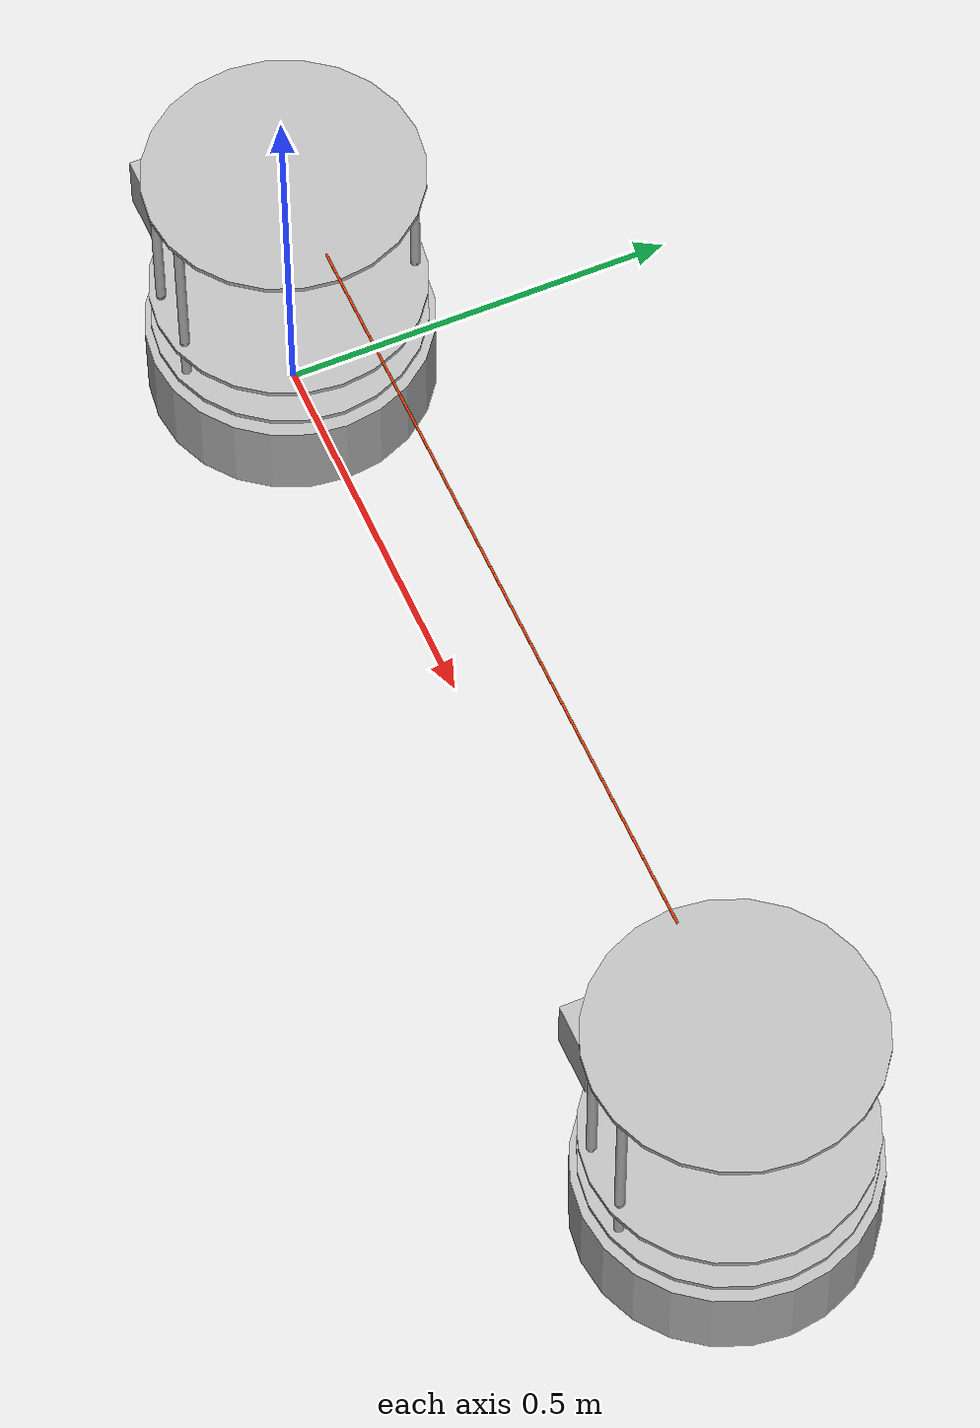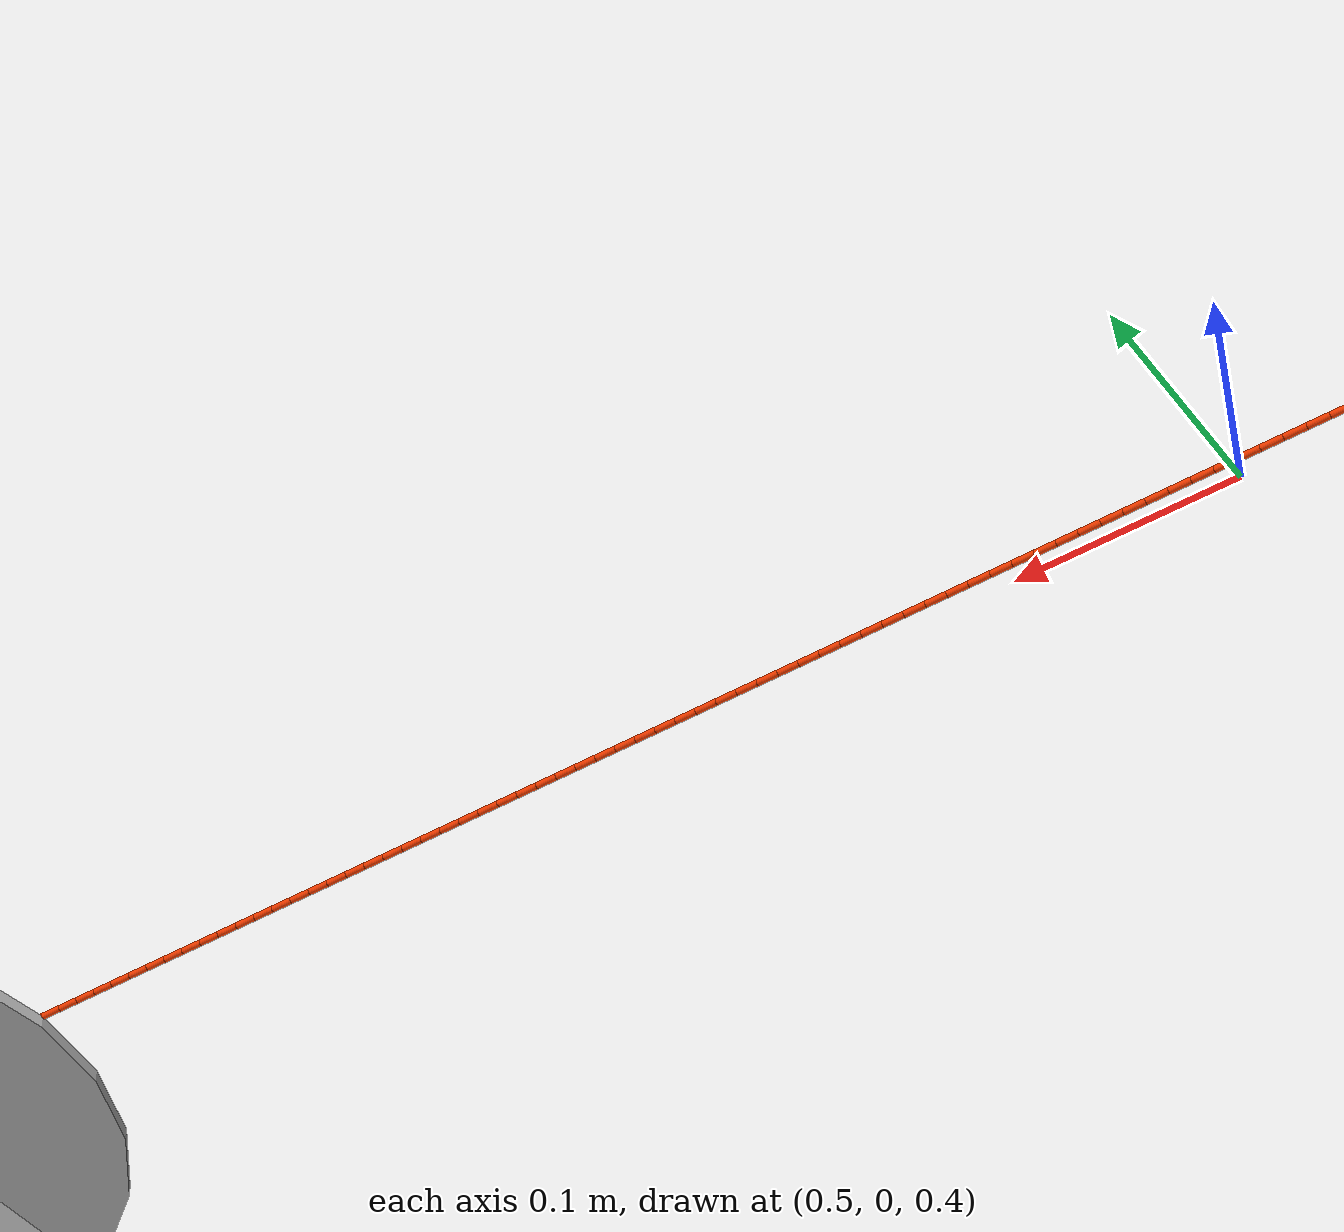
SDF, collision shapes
<?xml version="1.0" ?>
<sdf version="1.4">
  <model name="tethered_turtlebots">
<static>false</static>

  <!-- TURTLEBOT 1 -->
     <link name='base_foot1print'>
        <pose>0 0 0 0 -0 0</pose>
        <inertial>
          <pose>0.00947362 2.50779e-05 0.014919 0 -0 0</pose>
          <mass>2.4723</mass>
          <inertia>
            <ixx>0.0578436</ixx>
            <ixy>-2.91646e-06</ixy>
            <ixz>0.000317338</ixz>
            <iyy>0.0579316</iyy>
            <iyz>-9.59821e-07</iyz>
            <izz>0.0719963</izz>
          </inertia>
        </inertial>
        <collision name='base_foot1print_collision_base_link'>
          <pose>0 0 0.06969 0 -0 0</pose>
          <geometry>
            <cylinder>
              <length>0.10938</length>
              <radius>0.178</radius>
            </cylinder>
          </geometry>
          <surface>
            <contact>
              <ode/>
            </contact>
            <friction>
              <ode>
                <mu>0.3</mu>
                <mu2>0.3</mu2>
              </ode>
            </friction>
            <bounce/>
          </surface>
          <max_contacts>10</max_contacts>
        </collision>
        <collision name='base_foot1print_collision_camera_link'>
          <pose>-0.118 0 0.2812 0 -0 0</pose>
          <geometry>
            <box>
              <size>0.07271 0.27794 0.073</size>
            </box>
          </geometry>
          <surface>
            <contact>
              <ode/>
            </contact>
            <friction>
              <ode/>
            </friction>
            <bounce/>
          </surface>
          <max_contacts>10</max_contacts>
        </collision>
        <collision name='base_foot1print_collision_caster_back_link'>
          <pose>-0.135 0 0.0192 -1.5708 0 0</pose>
          <geometry>
            <cylinder>
              <length>0.0176</length>
              <radius>0.017</radius>
            </cylinder>
          </geometry>
          <surface>
            <contact>
              <ode>
                <kp>1e+06</kp>
                <kd>100</kd>
                <max_vel>1</max_vel>
                <min_depth>0.001</min_depth>
              </ode>
            </contact>
            <friction>
              <ode>
                <mu>0</mu>
                <mu2>0</mu2>
              </ode>
            </friction>
            <bounce/>
          </surface>
          <max_contacts>10</max_contacts>
        </collision>
        <collision name='base_foot1print_collision_caster_front_link'>
          <pose>0.115 0 0.0172 -1.5708 0 0</pose>
          <geometry>
            <cylinder>
              <length>0.0176</length>
              <radius>0.017</radius>
            </cylinder>
          </geometry>
          <surface>
            <contact>
              <ode>
                <kp>1e+06</kp>
                <kd>100</kd>
                <max_vel>1</max_vel>
                <min_depth>0.001</min_depth>
              </ode>
            </contact>
            <friction>
              <ode>
                <mu>0</mu>
                <mu2>0</mu2>
              </ode>
            </friction>
            <bounce/>
          </surface>
          <max_contacts>10</max_contacts>
        </collision>
        <collision name='base_foot1print_collision_plate_bottom_link'>
          <pose>0 0 0.1408 0 -0 0</pose>
          <geometry>
            <cylinder>
              <length>0.006</length>
              <radius>0.17</radius>
            </cylinder>
          </geometry>
          <max_contacts>10</max_contacts>
          <surface>
            <bounce/>
            <friction>
              <ode/>
            </friction>
            <contact>
              <ode/>
            </contact>
          </surface>
        </collision>
        <collision name='base_foot1print_collision_plate_middle_link'>
          <pose>0 0 0.1976 0 -0 0</pose>
          <geometry>
            <cylinder>
              <length>0.006</length>
              <radius>0.17</radius>
            </cylinder>
          </geometry>
          <max_contacts>10</max_contacts>
          <surface>
            <bounce/>
            <friction>
              <ode/>
            </friction>
            <contact>
              <ode/>
            </contact>
          </surface>
        </collision>
        <collision name='base_foot1print_collision_plate_top_link'>
          <pose>0 0 0.4068 0 -0 0</pose>
          <geometry>
            <cylinder>
              <length>0.006</length>
              <radius>0.17</radius>
            </cylinder>
          </geometry>
          <max_contacts>10</max_contacts>
          <surface>
            <bounce/>
            <friction>
              <ode/>
            </friction>
            <contact>
              <ode/>
            </contact>
          </surface>
        </collision>
        <collision name='base_foot1print_collision_pole_bottom_0_link'>
          <pose>0.12 0.082 0.113 0 -0 0</pose>
          <geometry>
            <cylinder>
              <length>0.0492</length>
              <radius>0.006</radius>
            </cylinder>
          </geometry>
          <max_contacts>10</max_contacts>
          <surface>
            <bounce/>
            <friction>
              <ode/>
            </friction>
            <contact>
              <ode/>
            </contact>
          </surface>
        </collision>
        <collision name='base_foot1print_collision_pole_bottom_1_link'>
          <pose>0.055 0.12 0.113 0 -0 0</pose>
          <geometry>
            <cylinder>
              <length>0.0492</length>
              <radius>0.006</radius>
            </cylinder>
          </geometry>
          <max_contacts>10</max_contacts>
          <surface>
            <bounce/>
            <friction>
              <ode/>
            </friction>
            <contact>
              <ode/>
            </contact>
          </surface>
        </collision>
        <collision name='base_foot1print_collision_pole_bottom_2_link'>
          <pose>-0.055 0.12 0.113 0 -0 0</pose>
          <geometry>
            <cylinder>
              <length>0.0492</length>
              <radius>0.006</radius>
            </cylinder>
          </geometry>
          <max_contacts>10</max_contacts>
          <surface>
            <bounce/>
            <friction>
              <ode/>
            </friction>
            <contact>
              <ode/>
            </contact>
          </surface>
        </collision>
        <collision name='base_foot1print_collision_pole_bottom_3_link'>
          <pose>0.12 -0.082 0.113 0 -0 0</pose>
          <geometry>
            <cylinder>
              <length>0.0492</length>
              <radius>0.006</radius>
            </cylinder>
          </geometry>
          <max_contacts>10</max_contacts>
          <surface>
            <bounce/>
            <friction>
              <ode/>
            </friction>
            <contact>
              <ode/>
            </contact>
          </surface>
        </collision>
        <collision name='base_foot1print_collision_pole_bottom_4_link'>
          <pose>0.055 -0.12 0.113 0 -0 0</pose>
          <geometry>
            <cylinder>
              <length>0.0492</length>
              <radius>0.006</radius>
            </cylinder>
          </geometry>
          <max_contacts>10</max_contacts>
          <surface>
            <bounce/>
            <friction>
              <ode/>
            </friction>
            <contact>
              <ode/>
            </contact>
          </surface>
        </collision>
        <collision name='base_foot1print_collision_pole_bottom_5_link'>
          <pose>-0.055 -0.12 0.113 0 -0 0</pose>
          <geometry>
            <cylinder>
              <length>0.0492</length>
              <radius>0.006</radius>
            </cylinder>
          </geometry>
          <max_contacts>10</max_contacts>
          <surface>
            <bounce/>
            <friction>
              <ode/>
            </friction>
            <contact>
              <ode/>
            </contact>
          </surface>
        </collision>
        <collision name='base_foot1print_collision_pole_kinect_0_link'>
          <pose>-0.1024 0.098 0.2474 0 -0 0</pose>
          <geometry>
            <cylinder>
              <length>0.0936</length>
              <radius>0.006</radius>
            </cylinder>
          </geometry>
          <max_contacts>10</max_contacts>
          <surface>
            <bounce/>
            <friction>
              <ode/>
            </friction>
            <contact>
              <ode/>
            </contact>
          </surface>
        </collision>
        <collision name='base_foot1print_collision_pole_kinect_1_link'>
          <pose>-0.1024 -0.098 0.2474 0 -0 0</pose>
          <geometry>
            <cylinder>
              <length>0.0936</length>
              <radius>0.006</radius>
            </cylinder>
          </geometry>
          <max_contacts>10</max_contacts>
          <surface>
            <bounce/>
            <friction>
              <ode/>
            </friction>
            <contact>
              <ode/>
            </contact>
          </surface>
        </collision>
        <collision name='base_foot1print_collision_pole_middle_0_link'>
          <pose>0.0381 0.1505 0.1742 0 -0 0</pose>
          <geometry>
            <cylinder>
              <length>0.0608</length>
              <radius>0.006</radius>
            </cylinder>
          </geometry>
          <max_contacts>10</max_contacts>
          <surface>
            <bounce/>
            <friction>
              <ode/>
            </friction>
            <contact>
              <ode/>
            </contact>
          </surface>
        </collision>
        <collision name='base_foot1print_collision_pole_middle_1_link'>
          <pose>0.0381 -0.1505 0.1742 0 -0 0</pose>
          <geometry>
            <cylinder>
              <length>0.0608</length>
              <radius>0.006</radius>
            </cylinder>
          </geometry>
          <max_contacts>10</max_contacts>
          <surface>
            <bounce/>
            <friction>
              <ode/>
            </friction>
            <contact>
              <ode/>
            </contact>
          </surface>
        </collision>
        <collision name='base_foot1print_collision_pole_middle_2_link'>
          <pose>-0.0381 0.1505 0.1742 0 -0 0</pose>
          <geometry>
            <cylinder>
              <length>0.0608</length>
              <radius>0.006</radius>
            </cylinder>
          </geometry>
          <max_contacts>10</max_contacts>
          <surface>
            <bounce/>
            <friction>
              <ode/>
            </friction>
            <contact>
              <ode/>
            </contact>
          </surface>
        </collision>
        <collision name='base_foot1print_collision_pole_middle_3_link'>
          <pose>-0.0381 -0.1505 0.1742 0 -0 0</pose>
          <geometry>
            <cylinder>
              <length>0.0608</length>
              <radius>0.006</radius>
            </cylinder>
          </geometry>
          <max_contacts>10</max_contacts>
          <surface>
            <bounce/>
            <friction>
              <ode/>
            </friction>
            <contact>
              <ode/>
            </contact>
          </surface>
        </collision>
        <collision name='base_foot1print_collision_pole_top_0_link'>
          <pose>0.0381 0.1505 0.3022 0 -0 0</pose>
          <geometry>
            <cylinder>
              <length>0.2032</length>
              <radius>0.006</radius>
            </cylinder>
          </geometry>
          <max_contacts>10</max_contacts>
          <surface>
            <bounce/>
            <friction>
              <ode/>
            </friction>
            <contact>
              <ode/>
            </contact>
          </surface>
        </collision>
        <collision name='base_foot1print_collision_pole_top_1_link'>
          <pose>0.0381 -0.1505 0.3022 0 -0 0</pose>
          <geometry>
            <cylinder>
              <length>0.2032</length>
              <radius>0.006</radius>
            </cylinder>
          </geometry>
          <max_contacts>10</max_contacts>
          <surface>
            <bounce/>
            <friction>
              <ode/>
            </friction>
            <contact>
              <ode/>
            </contact>
          </surface>
        </collision>
        <collision name='base_foot1print_collision_pole_top_2_link'>
          <pose>-0.0381 0.1505 0.3022 0 -0 0</pose>
          <geometry>
            <cylinder>
              <length>0.2032</length>
              <radius>0.006</radius>
            </cylinder>
          </geometry>
          <max_contacts>10</max_contacts>
          <surface>
            <bounce/>
            <friction>
              <ode/>
            </friction>
            <contact>
              <ode/>
            </contact>
          </surface>
        </collision>
        <collision name='base_foot1print_collision_pole_top_3_link'>
          <pose>-0.0381 -0.1505 0.3022 0 -0 0</pose>
          <geometry>
            <cylinder>
              <length>0.2032</length>
              <radius>0.006</radius>
            </cylinder>
          </geometry>
          <max_contacts>10</max_contacts>
          <surface>
            <bounce/>
            <friction>
              <ode/>
            </friction>
            <contact>
              <ode/>
            </contact>
          </surface>
        </collision>
        <visual name='base_foot1print_visual_base_link'>
          <pose>0.001 0 0.06219 0 -0 0</pose>
          <geometry>
            <mesh>
              <scale>1 1 1</scale>
              <uri>/opt/ros/indigo/share/kobuki_description/meshes/main_body.dae</uri>
            </mesh>
          </geometry>
        </visual>
        <visual name='base_foot1print_visual_camera_link'>
          <pose>-0.118 0 0.2812 0 -0 1.5708</pose>
          <geometry>
            <mesh>
              <scale>1 1 1</scale>
              <uri>/opt/ros/indigo/share/turtlebot_description/meshes/sensors/kinect.dae</uri>
            </mesh>
          </geometry>
        </visual>
        <visual name='base_foot1print_visual_plate_bottom_link'>
          <pose>0.02364 0 0.1408 0 -0 0</pose>
          <geometry>
            <mesh>
              <scale>1 1 1</scale>
              <uri>/opt/ros/indigo/share/turtlebot_description/meshes/stacks/hexagons/plate_bottom.dae</uri>
            </mesh>
          </geometry>
        </visual>
        <visual name='base_foot1print_visual_plate_middle_link'>
          <pose>-0.01364 0 0.1976 0 -0 0</pose>
          <geometry>
            <mesh>
              <scale>1 1 1</scale>
              <uri>/opt/ros/indigo/share/turtlebot_description/meshes/stacks/hexagons/plate_middle.dae</uri>
            </mesh>
          </geometry>
        </visual>
        <visual name='base_foot1print_visual_plate_top_link'>
          <pose>-0.01364 0 0.4068 0 -0 0</pose>
          <geometry>
            <mesh>
              <scale>1 1 1</scale>
              <uri>/opt/ros/indigo/share/turtlebot_description/meshes/stacks/hexagons/plate_top.dae</uri>
            </mesh>
          </geometry>
        </visual>
        <visual name='base_foot1print_visual_pole_bottom_0_link'>
          <pose>0.12 0.082 0.113 0 -0 0</pose>
          <geometry>
            <mesh>
              <scale>1 1 1</scale>
              <uri>/opt/ros/indigo/share/turtlebot_description/meshes/stacks/hexagons/pole_bottom.dae</uri>
            </mesh>
          </geometry>
        </visual>
        <visual name='base_foot1print_visual_pole_bottom_1_link'>
          <pose>0.055 0.12 0.113 0 -0 0</pose>
          <geometry>
            <mesh>
              <scale>1 1 1</scale>
              <uri>/opt/ros/indigo/share/turtlebot_description/meshes/stacks/hexagons/pole_bottom.dae</uri>
            </mesh>
          </geometry>
        </visual>
        <visual name='base_foot1print_visual_pole_bottom_2_link'>
          <pose>-0.055 0.12 0.113 0 -0 0</pose>
          <geometry>
            <mesh>
              <scale>1 1 1</scale>
              <uri>/opt/ros/indigo/share/turtlebot_description/meshes/stacks/hexagons/pole_bottom.dae</uri>
            </mesh>
          </geometry>
        </visual>
        <visual name='base_foot1print_visual_pole_bottom_3_link'>
          <pose>0.12 -0.082 0.113 0 -0 0</pose>
          <geometry>
            <mesh>
              <scale>1 1 1</scale>
              <uri>/opt/ros/indigo/share/turtlebot_description/meshes/stacks/hexagons/pole_bottom.dae</uri>
            </mesh>
          </geometry>
        </visual>
        <visual name='base_foot1print_visual_pole_bottom_4_link'>
          <pose>0.055 -0.12 0.113 0 -0 0</pose>
          <geometry>
            <mesh>
              <scale>1 1 1</scale>
              <uri>/opt/ros/indigo/share/turtlebot_description/meshes/stacks/hexagons/pole_bottom.dae</uri>
            </mesh>
          </geometry>
        </visual>
        <visual name='base_foot1print_visual_pole_bottom_5_link'>
          <pose>-0.055 -0.12 0.113 0 -0 0</pose>
          <geometry>
            <mesh>
              <scale>1 1 1</scale>
              <uri>/opt/ros/indigo/share/turtlebot_description/meshes/stacks/hexagons/pole_bottom.dae</uri>
            </mesh>
          </geometry>
        </visual>
        <visual name='base_foot1print_visual_pole_kinect_0_link'>
          <pose>-0.1024 0.098 0.2474 0 -0 0</pose>
          <geometry>
            <mesh>
              <scale>1 1 1</scale>
              <uri>/opt/ros/indigo/share/turtlebot_description/meshes/stacks/hexagons/pole_kinect.dae</uri>
            </mesh>
          </geometry>
        </visual>
        <visual name='base_foot1print_visual_pole_kinect_1_link'>
          <pose>-0.1024 -0.098 0.2474 0 -0 0</pose>
          <geometry>
            <mesh>
              <scale>1 1 1</scale>
              <uri>/opt/ros/indigo/share/turtlebot_description/meshes/stacks/hexagons/pole_kinect.dae</uri>
            </mesh>
          </geometry>
        </visual>
        <visual name='base_foot1print_visual_pole_middle_0_link'>
          <pose>0.0381 0.1505 0.1742 3.14159 -2.06823e-13 3.14159</pose>
          <geometry>
            <mesh>
              <scale>1 1 1</scale>
              <uri>/opt/ros/indigo/share/turtlebot_description/meshes/stacks/hexagons/pole_middle.dae</uri>
            </mesh>
          </geometry>
        </visual>
        <visual name='base_foot1print_visual_pole_middle_1_link'>
          <pose>0.0381 -0.1505 0.1742 3.14159 -2.06823e-13 3.14159</pose>
          <geometry>
            <mesh>
              <scale>1 1 1</scale>
              <uri>/opt/ros/indigo/share/turtlebot_description/meshes/stacks/hexagons/pole_middle.dae</uri>
            </mesh>
          </geometry>
        </visual>
        <visual name='base_foot1print_visual_pole_middle_2_link'>
          <pose>-0.0381 0.1505 0.1742 3.14159 -2.06823e-13 3.14159</pose>
          <geometry>
            <mesh>
              <scale>1 1 1</scale>
              <uri>/opt/ros/indigo/share/turtlebot_description/meshes/stacks/hexagons/pole_middle.dae</uri>
            </mesh>
          </geometry>
        </visual>
        <visual name='base_foot1print_visual_pole_middle_3_link'>
          <pose>-0.0381 -0.1505 0.1742 3.14159 -2.06823e-13 3.14159</pose>
          <geometry>
            <mesh>
              <scale>1 1 1</scale>
              <uri>/opt/ros/indigo/share/turtlebot_description/meshes/stacks/hexagons/pole_middle.dae</uri>
            </mesh>
          </geometry>
        </visual>
        <visual name='base_foot1print_visual_pole_top_0_link'>
          <pose>0.0381 0.1505 0.3022 0 -0 0</pose>
          <geometry>
            <mesh>
              <scale>1 1 1</scale>
              <uri>/opt/ros/indigo/share/turtlebot_description/meshes/stacks/hexagons/pole_top.dae</uri>
            </mesh>
          </geometry>
        </visual>
        <visual name='base_foot1print_visual_pole_top_1_link'>
          <pose>0.0381 -0.1505 0.3022 0 -0 0</pose>
          <geometry>
            <mesh>
              <scale>1 1 1</scale>
              <uri>/opt/ros/indigo/share/turtlebot_description/meshes/stacks/hexagons/pole_top.dae</uri>
            </mesh>
          </geometry>
        </visual>
        <visual name='base_foot1print_visual_pole_top_2_link'>
          <pose>-0.0381 0.1505 0.3022 0 -0 0</pose>
          <geometry>
            <mesh>
              <scale>1 1 1</scale>
              <uri>/opt/ros/indigo/share/turtlebot_description/meshes/stacks/hexagons/pole_top.dae</uri>
            </mesh>
          </geometry>
        </visual>
        <visual name='base_foot1print_visual_pole_top_3_link'>
          <pose>-0.0381 -0.1505 0.3022 0 -0 0</pose>
          <geometry>
            <mesh>
              <scale>1 1 1</scale>
              <uri>/opt/ros/indigo/share/turtlebot_description/meshes/stacks/hexagons/pole_top.dae</uri>
            </mesh>
          </geometry>
        </visual>
        <velocity_decay>
          <linear>0</linear>
          <angular>0</angular>
        </velocity_decay>
        <sensor name='bumpers' type='contact'>
          <always_on>1</always_on>
          <update_rate>50</update_rate>
          <visualize>1</visualize>
          <contact>
            <collision>base_foot1print_collision_base_link</collision>
            <topic>__default_topic__</topic>
          </contact>
          <pose>0 0 0.0102 0 -0 0</pose>
        </sensor>
        <velocity_decay>
          <linear>0</linear>
          <angular>0</angular>
        </velocity_decay>
        <sensor name='camera' type='depth'>
          <always_on>1</always_on>
          <update_rate>20</update_rate>
          <camera name='__default__'>
            <horizontal_fov>1.0472</horizontal_fov>
            <image>
              <format>R8G8B8</format>
              <width>640</width>
              <height>480</height>
            </image>
            <clip>
              <near>0.05</near>
              <far>8</far>
            </clip>
          </camera>
          <plugin name='kinect_camera_controller' filename='libgazebo_ros_openni_kinect.so'>
            <robotNamespace>/turtle1</robotNamespace>
            <cameraName>camera</cameraName>
            <alwaysOn>true</alwaysOn>
            <updateRate>10</updateRate>
            <imageTopicName>rgb/image_raw</imageTopicName>
            <depthImageTopicName>depth/image_raw</depthImageTopicName>
            <pointCloudTopicName>depth/points</pointCloudTopicName>
            <cameraInfoTopicName>rgb/camera_info</cameraInfoTopicName>
            <depthImageCameraInfoTopicName>depth/camera_info</depthImageCameraInfoTopicName>
            <frameName>camera_depth_optical_frame</frameName>
            <baseline>0.1</baseline>
            <distortion_k1>0.0</distortion_k1>
            <distortion_k2>0.0</distortion_k2>
            <distortion_k3>0.0</distortion_k3>
            <distortion_t1>0.0</distortion_t1>
            <distortion_t2>0.0</distortion_t2>
            <pointCloudCutoff>0.4</pointCloudCutoff>
          </plugin>
		  <!-- Pose from real Trutlebot -->
          <pose>-0.118 -0.01 0.285 0 -0 0</pose>
        </sensor>
        <velocity_decay>
          <linear>0</linear>
          <angular>0</angular>
        </velocity_decay>
        <velocity_decay>
          <linear>0</linear>
          <angular>0</angular>
        </velocity_decay>
        <velocity_decay>
          <linear>0</linear>
          <angular>0</angular>
        </velocity_decay>
        <sensor name='cliff_sensor_front' type='ray'>
          <always_on>1</always_on>
          <update_rate>50</update_rate>
          <visualize>1</visualize>
          <ray>
            <scan>
              <horizontal>
                <samples>50</samples>
                <resolution>1</resolution>
                <min_angle>-0.0436</min_angle>
                <max_angle>0.0436</max_angle>
              </horizontal>
            </scan>
            <range>
              <min>0.01</min>
              <max>0.15</max>
              <resolution>1</resolution>
            </range>
          </ray>
          <pose>0.156 0 0.0316 3.14159 1.57079 3.14159</pose>
        </sensor>
        <velocity_decay>
          <linear>0</linear>
          <angular>0</angular>
        </velocity_decay>
        <sensor name='cliff_sensor_left' type='ray'>
          <always_on>1</always_on>
          <update_rate>50</update_rate>
          <visualize>1</visualize>
          <ray>
            <scan>
              <horizontal>
                <samples>50</samples>
                <resolution>1</resolution>
                <min_angle>-0.0436</min_angle>
                <max_angle>0.0436</max_angle>
              </horizontal>
            </scan>
            <range>
              <min>0.01</min>
              <max>0.15</max>
              <resolution>1</resolution>
            </range>
          </ray>
          <pose>0.08734 0.13601 0.0316 3.14159 1.57079 3.14159</pose>
        </sensor>
        <velocity_decay>
          <linear>0</linear>
          <angular>0</angular>
        </velocity_decay>
        <sensor name='cliff_sensor_right' type='ray'>
          <always_on>1</always_on>
          <update_rate>50</update_rate>
          <visualize>1</visualize>
          <ray>
            <scan>
              <horizontal>
                <samples>50</samples>
                <resolution>1</resolution>
                <min_angle>-0.0436</min_angle>
                <max_angle>0.0436</max_angle>
              </horizontal>
            </scan>
            <range>
              <min>0.01</min>
              <max>0.15</max>
              <resolution>1</resolution>
            </range>
          </ray>
          <pose>0.085 -0.13601 0.0316 3.14159 1.57079 3.14159</pose>
        </sensor>
        <gravity>1</gravity>
        <velocity_decay>
          <linear>0</linear>
          <angular>0</angular>
        </velocity_decay>
        <self_collide>0</self_collide>
        <sensor name='imu' type='imu'>
          <always_on>1</always_on>
          <update_rate>50</update_rate>
          <visualize>0</visualize>
          <imu>
            <noise>
              <type>gaussian</type>
              <rate>
                <mean>0</mean>
                <stddev>1.96e-06</stddev>
                <bias_mean>0</bias_mean>
                <bias_stddev>0</bias_stddev>
              </rate>
              <accel>
                <mean>0</mean>
                <stddev>0.017</stddev>
                <bias_mean>0.1</bias_mean>
                <bias_stddev>0.001</bias_stddev>
              </accel>
            </noise>
          </imu>
          <pose>0.056 0.062 0.0304 0 -0 0</pose>
        </sensor>
        <kinematic>0</kinematic>
      </link>
      <link name='wheel1_left_link'>
        <pose>0 0.115 0.0352 -1.5708 0 0</pose>
        <inertial>
          <pose>0 0 0 0 -0 0</pose>
          <mass>0.01</mass>
          <inertia>
            <ixx>0.001</ixx>
            <ixy>0</ixy>
            <ixz>0</ixz>
            <iyy>0.001</iyy>
            <iyz>0</iyz>
            <izz>0.001</izz>
          </inertia>
        </inertial>
        <collision name='wheel1_left_link_collision'>
          <pose>0 0 0 0 -0 0</pose>
          <geometry>
            <cylinder>
              <length>0.0206</length>
              <radius>0.0352</radius>
            </cylinder>
          </geometry>
          <surface>
            <contact>
              <ode>
                <kp>1e+06</kp>
                <kd>100</kd>
                <max_vel>1</max_vel>
                <min_depth>0.001</min_depth>
              </ode>
            </contact>
            <friction>
              <ode>
                <mu>1</mu>
                <mu2>1</mu2>
              </ode>
            </friction>
            <bounce/>
          </surface>
          <max_contacts>10</max_contacts>
        </collision>
        <visual name='wheel1_left_link_visual'>
          <pose>0 0 0 0 -0 0</pose>
          <geometry>
            <mesh>
              <scale>1 1 1</scale>
              <uri>/opt/ros/indigo/share/kobuki_description/meshes/wheel.dae</uri>
            </mesh>
          </geometry>
        </visual>
        <gravity>1</gravity>
        <velocity_decay>
          <linear>0</linear>
          <angular>0</angular>
        </velocity_decay>
        <self_collide>0</self_collide>
        <kinematic>0</kinematic>
      </link>
      <joint name='wheel1_left_joint' type='revolute'>
        <child>wheel1_left_link</child>
        <parent>base_foot1print</parent>
        <axis>
          <xyz>0 1 0</xyz>
          <limit>
            <lower>-1e+16</lower>
            <upper>1e+16</upper>
          </limit>
        </axis>
      </joint>
      <link name='wheel1_right_link'>
        <pose>0 -0.115 0.0352 -1.5708 0 0</pose>
        <inertial>
          <pose>0 0 0 0 -0 0</pose>
          <mass>0.01</mass>
          <inertia>
            <ixx>0.001</ixx>
            <ixy>0</ixy>
            <ixz>0</ixz>
            <iyy>0.001</iyy>
            <iyz>0</iyz>
            <izz>0.001</izz>
          </inertia>
        </inertial>
        <collision name='wheel1_right_link_collision'>
          <pose>0 0 0 0 -0 0</pose>
          <geometry>
            <cylinder>
              <length>0.0206</length>
              <radius>0.035</radius>
            </cylinder>
          </geometry>
          <surface>
            <contact>
              <ode>
                <kp>1e+06</kp>
                <kd>100</kd>
                <max_vel>1</max_vel>
                <min_depth>0.001</min_depth>
              </ode>
            </contact>
            <friction>
              <ode>
                <mu>1</mu>
                <mu2>1</mu2>
              </ode>
            </friction>
            <bounce/>
          </surface>
          <max_contacts>10</max_contacts>
        </collision>
        <visual name='wheel1_right_link_visual'>
          <pose>0 0 0 0 -0 0</pose>
          <geometry>
            <mesh>
              <scale>1 1 1</scale>
              <uri>/opt/ros/indigo/share/kobuki_description/meshes/wheel.dae</uri>
            </mesh>
          </geometry>
        </visual>
        <gravity>1</gravity>
        <velocity_decay>
          <linear>0</linear>
          <angular>0</angular>
        </velocity_decay>
        <self_collide>0</self_collide>
        <kinematic>0</kinematic>
      </link>
      <joint name='wheel1_right_joint' type='revolute'>
        <child>wheel1_right_link</child>
        <parent>base_foot1print</parent>
        <axis>
          <xyz>0 1 0</xyz>
          <limit>
            <lower>-1e+16</lower>
            <upper>1e+16</upper>
          </limit>
        </axis>
      </joint>
      <static>0</static>
      <plugin name='kobuki1_controller' filename='libgazebo_ros_diff_drive.so'>
        <publish_tf>1</publish_tf>
        <leftJoint>wheel1_right_joint</leftJoint>
        <rightJoint>wheel1_left_joint</rightJoint>
        <wheelSeparation>.230</wheelSeparation>
        <wheelDiameter>0.070</wheelDiameter>
        <wheelTorque>1.0</wheelTorque>
        <velocity_command_timeout>0.6</velocity_command_timeout>
        <cliff_sensor_left_name>cliff_sensor_left</cliff_sensor_left_name>
        <cliff_sensor_center_name>cliff_sensor_front</cliff_sensor_center_name>
        <cliff_sensor_right_name>cliff_sensor_right</cliff_sensor_right_name>
        <cliff_detection_threshold>0.04</cliff_detection_threshold>
        <bumper_name>bumpers</bumper_name>
        <imu_name>imu</imu_name>
        <robotNamespace>/turtle1</robotNamespace>
      </plugin>

	  <!-- TURTLEBOT 2 -->
     <link name='base_foot2print'>
        <pose>1.27 0 0 0 0 0</pose>
        <inertial>
          <pose>0.00947362 2.50779e-05 0.014919 0 -0 0</pose>
          <mass>2.4723</mass>
          <inertia>
            <ixx>0.0578436</ixx>
            <ixy>-2.91646e-06</ixy>
            <ixz>0.000317338</ixz>
            <iyy>0.0579316</iyy>
            <iyz>-9.59821e-07</iyz>
            <izz>0.0719963</izz>
          </inertia>
        </inertial>
        <collision name='base_foot2print_collision_base_link'>
          <pose>0 0 0.06969 0 0 0</pose>
          <geometry>
            <cylinder>
              <length>0.10938</length>
              <radius>0.178</radius>
            </cylinder>
          </geometry>
          <surface>
            <contact>
              <ode/>
            </contact>
            <friction>
              <ode>
                <mu>0.3</mu>
                <mu2>0.3</mu2>
              </ode>
            </friction>
            <bounce/>
          </surface>
          <max_contacts>10</max_contacts>
        </collision>
        <collision name='base_foot2print_collision_camera_link'>
          <pose>-0.118 0 0.2812 0 0 0</pose>
          <geometry>
            <box>
              <size>0.07271 0.27794 0.073</size>
            </box>
          </geometry>
          <surface>
            <contact>
              <ode/>
            </contact>
            <friction>
              <ode/>
            </friction>
            <bounce/>
          </surface>
          <max_contacts>10</max_contacts>
        </collision>
        <collision name='base_foot2print_collision_caster_back_link'>
          <pose>-0.135 0 0.0192 -1.5708 0 0</pose>
          <geometry>
            <cylinder>
              <length>0.0176</length>
              <radius>0.017</radius>
            </cylinder>
          </geometry>
          <surface>
            <contact>
              <ode>
                <kp>1e+06</kp>
                <kd>100</kd>
                <max_vel>1</max_vel>
                <min_depth>0.001</min_depth>
              </ode>
            </contact>
            <friction>
              <ode>
                <mu>0</mu>
                <mu2>0</mu2>
              </ode>
            </friction>
            <bounce/>
          </surface>
          <max_contacts>10</max_contacts>
        </collision>
        <collision name='base_foot2print_collision_caster_front_link'>
          <pose>0.115 0 0.0172 -1.5708 0 0</pose>
          <geometry>
            <cylinder>
              <length>0.0176</length>
              <radius>0.017</radius>
            </cylinder>
          </geometry>
          <surface>
            <contact>
              <ode>
                <kp>1e+06</kp>
                <kd>100</kd>
                <max_vel>1</max_vel>
                <min_depth>0.001</min_depth>
              </ode>
            </contact>
            <friction>
              <ode>
                <mu>0</mu>
                <mu2>0</mu2>
              </ode>
            </friction>
            <bounce/>
          </surface>
          <max_contacts>10</max_contacts>
        </collision>
        <collision name='base_foot2print_collision_plate_bottom_link'>
          <pose>0 0 0.1408 0 -0 0</pose>
          <geometry>
            <cylinder>
              <length>0.006</length>
              <radius>0.17</radius>
            </cylinder>
          </geometry>
          <max_contacts>10</max_contacts>
          <surface>
            <bounce/>
            <friction>
              <ode/>
            </friction>
            <contact>
              <ode/>
            </contact>
          </surface>
        </collision>
        <collision name='base_foot2print_collision_plate_middle_link'>
          <pose>0 0 0.1976 0 -0 0</pose>
          <geometry>
            <cylinder>
              <length>0.006</length>
              <radius>0.17</radius>
            </cylinder>
          </geometry>
          <max_contacts>10</max_contacts>
          <surface>
            <bounce/>
            <friction>
              <ode/>
            </friction>
            <contact>
              <ode/>
            </contact>
          </surface>
        </collision>
        <collision name='base_foot2print_collision_plate_top_link'>
          <pose>0 0 0.4068 0 -0 0</pose>
          <geometry>
            <cylinder>
              <length>0.006</length>
              <radius>0.17</radius>
            </cylinder>
          </geometry>
          <max_contacts>10</max_contacts>
          <surface>
            <bounce/>
            <friction>
              <ode/>
            </friction>
            <contact>
              <ode/>
            </contact>
          </surface>
        </collision>
        <collision name='base_foot2print_collision_pole_bottom_0_link'>
          <pose>0.12 0.082 0.113 0 -0 0</pose>
          <geometry>
            <cylinder>
              <length>0.0492</length>
              <radius>0.006</radius>
            </cylinder>
          </geometry>
          <max_contacts>10</max_contacts>
          <surface>
            <bounce/>
            <friction>
              <ode/>
            </friction>
            <contact>
              <ode/>
            </contact>
          </surface>
        </collision>
        <collision name='base_foot2print_collision_pole_bottom_1_link'>
          <pose>0.055 0.12 0.113 0 -0 0</pose>
          <geometry>
            <cylinder>
              <length>0.0492</length>
              <radius>0.006</radius>
            </cylinder>
          </geometry>
          <max_contacts>10</max_contacts>
          <surface>
            <bounce/>
            <friction>
              <ode/>
            </friction>
            <contact>
              <ode/>
            </contact>
          </surface>
        </collision>
        <collision name='base_foot2print_collision_pole_bottom_2_link'>
          <pose>-0.055 0.12 0.113 0 -0 0</pose>
          <geometry>
            <cylinder>
              <length>0.0492</length>
              <radius>0.006</radius>
            </cylinder>
          </geometry>
          <max_contacts>10</max_contacts>
          <surface>
            <bounce/>
            <friction>
              <ode/>
            </friction>
            <contact>
              <ode/>
            </contact>
          </surface>
        </collision>
        <collision name='base_foot2print_collision_pole_bottom_3_link'>
          <pose>0.12 -0.082 0.113 0 -0 0</pose>
          <geometry>
            <cylinder>
              <length>0.0492</length>
              <radius>0.006</radius>
            </cylinder>
          </geometry>
          <max_contacts>10</max_contacts>
          <surface>
            <bounce/>
            <friction>
              <ode/>
            </friction>
            <contact>
              <ode/>
            </contact>
          </surface>
        </collision>
        <collision name='base_foot2print_collision_pole_bottom_4_link'>
          <pose>0.055 -0.12 0.113 0 -0 0</pose>
          <geometry>
            <cylinder>
              <length>0.0492</length>
              <radius>0.006</radius>
            </cylinder>
          </geometry>
          <max_contacts>10</max_contacts>
          <surface>
            <bounce/>
            <friction>
              <ode/>
            </friction>
            <contact>
              <ode/>
            </contact>
          </surface>
        </collision>
        <collision name='base_foot2print_collision_pole_bottom_5_link'>
          <pose>-0.055 -0.12 0.113 0 -0 0</pose>
          <geometry>
            <cylinder>
              <length>0.0492</length>
              <radius>0.006</radius>
            </cylinder>
          </geometry>
          <max_contacts>10</max_contacts>
          <surface>
            <bounce/>
            <friction>
              <ode/>
            </friction>
            <contact>
              <ode/>
            </contact>
          </surface>
        </collision>
        <collision name='base_foot2print_collision_pole_kinect_0_link'>
          <pose>-0.1024 0.098 0.2474 0 -0 0</pose>
          <geometry>
            <cylinder>
              <length>0.0936</length>
              <radius>0.006</radius>
            </cylinder>
          </geometry>
          <max_contacts>10</max_contacts>
          <surface>
            <bounce/>
            <friction>
              <ode/>
            </friction>
            <contact>
              <ode/>
            </contact>
          </surface>
        </collision>
        <collision name='base_foot2print_collision_pole_kinect_1_link'>
          <pose>-0.1024 -0.098 0.2474 0 -0 0</pose>
          <geometry>
            <cylinder>
              <length>0.0936</length>
              <radius>0.006</radius>
            </cylinder>
          </geometry>
          <max_contacts>10</max_contacts>
          <surface>
            <bounce/>
            <friction>
              <ode/>
            </friction>
            <contact>
              <ode/>
            </contact>
          </surface>
        </collision>
        <collision name='base_foot2print_collision_pole_middle_0_link'>
          <pose>0.0381 0.1505 0.1742 0 -0 0</pose>
          <geometry>
            <cylinder>
              <length>0.0608</length>
              <radius>0.006</radius>
            </cylinder>
          </geometry>
          <max_contacts>10</max_contacts>
          <surface>
            <bounce/>
            <friction>
              <ode/>
            </friction>
            <contact>
              <ode/>
            </contact>
          </surface>
        </collision>
        <collision name='base_foot2print_collision_pole_middle_1_link'>
          <pose>0.0381 -0.1505 0.1742 0 -0 0</pose>
          <geometry>
            <cylinder>
              <length>0.0608</length>
              <radius>0.006</radius>
            </cylinder>
          </geometry>
          <max_contacts>10</max_contacts>
          <surface>
            <bounce/>
            <friction>
              <ode/>
            </friction>
            <contact>
              <ode/>
            </contact>
          </surface>
        </collision>
        <collision name='base_foot2print_collision_pole_middle_2_link'>
          <pose>-0.0381 0.1505 0.1742 0 -0 0</pose>
          <geometry>
            <cylinder>
              <length>0.0608</length>
              <radius>0.006</radius>
            </cylinder>
          </geometry>
          <max_contacts>10</max_contacts>
          <surface>
            <bounce/>
            <friction>
              <ode/>
            </friction>
            <contact>
              <ode/>
            </contact>
          </surface>
        </collision>
        <collision name='base_foot2print_collision_pole_middle_3_link'>
          <pose>-0.0381 -0.1505 0.1742 0 -0 0</pose>
          <geometry>
            <cylinder>
              <length>0.0608</length>
              <radius>0.006</radius>
            </cylinder>
          </geometry>
          <max_contacts>10</max_contacts>
          <surface>
            <bounce/>
            <friction>
              <ode/>
            </friction>
            <contact>
              <ode/>
            </contact>
          </surface>
        </collision>
        <collision name='base_foot2print_collision_pole_top_0_link'>
          <pose>0.0381 0.1505 0.3022 0 -0 0</pose>
          <geometry>
            <cylinder>
              <length>0.2032</length>
              <radius>0.006</radius>
            </cylinder>
          </geometry>
          <max_contacts>10</max_contacts>
          <surface>
            <bounce/>
            <friction>
              <ode/>
            </friction>
            <contact>
              <ode/>
            </contact>
          </surface>
        </collision>
        <collision name='base_foot2print_collision_pole_top_1_link'>
          <pose>0.0381 -0.1505 0.3022 0 -0 0</pose>
          <geometry>
            <cylinder>
              <length>0.2032</length>
              <radius>0.006</radius>
            </cylinder>
          </geometry>
          <max_contacts>10</max_contacts>
          <surface>
            <bounce/>
            <friction>
              <ode/>
            </friction>
            <contact>
              <ode/>
            </contact>
          </surface>
        </collision>
        <collision name='base_foot2print_collision_pole_top_2_link'>
          <pose>-0.0381 0.1505 0.3022 0 -0 0</pose>
          <geometry>
            <cylinder>
              <length>0.2032</length>
              <radius>0.006</radius>
            </cylinder>
          </geometry>
          <max_contacts>10</max_contacts>
          <surface>
            <bounce/>
            <friction>
              <ode/>
            </friction>
            <contact>
              <ode/>
            </contact>
          </surface>
        </collision>
        <collision name='base_foot2print_collision_pole_top_3_link'>
          <pose>-0.0381 -0.1505 0.3022 0 -0 0</pose>
          <geometry>
            <cylinder>
              <length>0.2032</length>
              <radius>0.006</radius>
            </cylinder>
          </geometry>
          <max_contacts>10</max_contacts>
          <surface>
            <bounce/>
            <friction>
              <ode/>
            </friction>
            <contact>
              <ode/>
            </contact>
          </surface>
        </collision>
        <visual name='base_foot2print_visual_base_link'>
          <pose>0.001 0 0.06219 0 -0 0</pose>
          <geometry>
            <mesh>
              <scale>1 1 1</scale>
              <uri>/opt/ros/indigo/share/kobuki_description/meshes/main_body.dae</uri>
            </mesh>
          </geometry>
        </visual>
        <visual name='base_foot2print_visual_camera_link'>
          <pose>-0.118 0 0.2812 0 -0 1.5708</pose>
          <geometry>
            <mesh>
              <scale>1 1 1</scale>
              <uri>/opt/ros/indigo/share/turtlebot_description/meshes/sensors/kinect.dae</uri>
            </mesh>
          </geometry>
        </visual>
        <visual name='base_foot2print_visual_plate_bottom_link'>
          <pose>0.02364 0 0.1408 0 -0 0</pose>
          <geometry>
            <mesh>
              <scale>1 1 1</scale>
              <uri>/opt/ros/indigo/share/turtlebot_description/meshes/stacks/hexagons/plate_bottom.dae</uri>
            </mesh>
          </geometry>
        </visual>
        <visual name='base_foot2print_visual_plate_middle_link'>
          <pose>-0.01364 0 0.1976 0 -0 0</pose>
          <geometry>
            <mesh>
              <scale>1 1 1</scale>
              <uri>/opt/ros/indigo/share/turtlebot_description/meshes/stacks/hexagons/plate_middle.dae</uri>
            </mesh>
          </geometry>
        </visual>
        <visual name='base_foot2print_visual_plate_top_link'>
          <pose>-0.01364 0 0.4068 0 -0 0</pose>
          <geometry>
            <mesh>
              <scale>1 1 1</scale>
              <uri>/opt/ros/indigo/share/turtlebot_description/meshes/stacks/hexagons/plate_top.dae</uri>
            </mesh>
          </geometry>
        </visual>
        <visual name='base_foot2print_visual_pole_bottom_0_link'>
          <pose>0.12 0.082 0.113 0 -0 0</pose>
          <geometry>
            <mesh>
              <scale>1 1 1</scale>
              <uri>/opt/ros/indigo/share/turtlebot_description/meshes/stacks/hexagons/pole_bottom.dae</uri>
            </mesh>
          </geometry>
        </visual>
        <visual name='base_foot2print_visual_pole_bottom_1_link'>
          <pose>0.055 0.12 0.113 0 -0 0</pose>
          <geometry>
            <mesh>
              <scale>1 1 1</scale>
              <uri>/opt/ros/indigo/share/turtlebot_description/meshes/stacks/hexagons/pole_bottom.dae</uri>
            </mesh>
          </geometry>
        </visual>
        <visual name='base_foot2print_visual_pole_bottom_2_link'>
          <pose>-0.055 0.12 0.113 0 -0 0</pose>
          <geometry>
            <mesh>
              <scale>1 1 1</scale>
              <uri>/opt/ros/indigo/share/turtlebot_description/meshes/stacks/hexagons/pole_bottom.dae</uri>
            </mesh>
          </geometry>
        </visual>
        <visual name='base_foot2print_visual_pole_bottom_3_link'>
          <pose>0.12 -0.082 0.113 0 -0 0</pose>
          <geometry>
            <mesh>
              <scale>1 1 1</scale>
              <uri>/opt/ros/indigo/share/turtlebot_description/meshes/stacks/hexagons/pole_bottom.dae</uri>
            </mesh>
          </geometry>
        </visual>
        <visual name='base_foot2print_visual_pole_bottom_4_link'>
          <pose>0.055 -0.12 0.113 0 -0 0</pose>
          <geometry>
            <mesh>
              <scale>1 1 1</scale>
              <uri>/opt/ros/indigo/share/turtlebot_description/meshes/stacks/hexagons/pole_bottom.dae</uri>
            </mesh>
          </geometry>
        </visual>
        <visual name='base_foot2print_visual_pole_bottom_5_link'>
          <pose>-0.055 -0.12 0.113 0 -0 0</pose>
          <geometry>
            <mesh>
              <scale>1 1 1</scale>
              <uri>/opt/ros/indigo/share/turtlebot_description/meshes/stacks/hexagons/pole_bottom.dae</uri>
            </mesh>
          </geometry>
        </visual>
        <visual name='base_foot2print_visual_pole_kinect_0_link'>
          <pose>-0.1024 0.098 0.2474 0 -0 0</pose>
          <geometry>
            <mesh>
              <scale>1 1 1</scale>
              <uri>/opt/ros/indigo/share/turtlebot_description/meshes/stacks/hexagons/pole_kinect.dae</uri>
            </mesh>
          </geometry>
        </visual>
        <visual name='base_foot2print_visual_pole_kinect_1_link'>
          <pose>-0.1024 -0.098 0.2474 0 -0 0</pose>
          <geometry>
            <mesh>
              <scale>1 1 1</scale>
              <uri>/opt/ros/indigo/share/turtlebot_description/meshes/stacks/hexagons/pole_kinect.dae</uri>
            </mesh>
          </geometry>
        </visual>
        <visual name='base_foot2print_visual_pole_middle_0_link'>
          <pose>0.0381 0.1505 0.1742 3.14159 -2.06823e-13 3.14159</pose>
          <geometry>
            <mesh>
              <scale>1 1 1</scale>
              <uri>/opt/ros/indigo/share/turtlebot_description/meshes/stacks/hexagons/pole_middle.dae</uri>
            </mesh>
          </geometry>
        </visual>
        <visual name='base_foot2print_visual_pole_middle_1_link'>
          <pose>0.0381 -0.1505 0.1742 3.14159 -2.06823e-13 3.14159</pose>
          <geometry>
            <mesh>
              <scale>1 1 1</scale>
              <uri>/opt/ros/indigo/share/turtlebot_description/meshes/stacks/hexagons/pole_middle.dae</uri>
            </mesh>
          </geometry>
        </visual>
        <visual name='base_foot2print_visual_pole_middle_2_link'>
          <pose>-0.0381 0.1505 0.1742 3.14159 -2.06823e-13 3.14159</pose>
          <geometry>
            <mesh>
              <scale>1 1 1</scale>
              <uri>/opt/ros/indigo/share/turtlebot_description/meshes/stacks/hexagons/pole_middle.dae</uri>
            </mesh>
          </geometry>
        </visual>
        <visual name='base_foot2print_visual_pole_middle_3_link'>
          <pose>-0.0381 -0.1505 0.1742 3.14159 -2.06823e-13 3.14159</pose>
          <geometry>
            <mesh>
              <scale>1 1 1</scale>
              <uri>/opt/ros/indigo/share/turtlebot_description/meshes/stacks/hexagons/pole_middle.dae</uri>
            </mesh>
          </geometry>
        </visual>
        <visual name='base_foot2print_visual_pole_top_0_link'>
          <pose>0.0381 0.1505 0.3022 0 -0 0</pose>
          <geometry>
            <mesh>
              <scale>1 1 1</scale>
              <uri>/opt/ros/indigo/share/turtlebot_description/meshes/stacks/hexagons/pole_top.dae</uri>
            </mesh>
          </geometry>
        </visual>
        <visual name='base_foot2print_visual_pole_top_1_link'>
          <pose>0.0381 -0.1505 0.3022 0 -0 0</pose>
          <geometry>
            <mesh>
              <scale>1 1 1</scale>
              <uri>/opt/ros/indigo/share/turtlebot_description/meshes/stacks/hexagons/pole_top.dae</uri>
            </mesh>
          </geometry>
        </visual>
        <visual name='base_foot2print_visual_pole_top_2_link'>
          <pose>-0.0381 0.1505 0.3022 0 -0 0</pose>
          <geometry>
            <mesh>
              <scale>1 1 1</scale>
              <uri>/opt/ros/indigo/share/turtlebot_description/meshes/stacks/hexagons/pole_top.dae</uri>
            </mesh>
          </geometry>
        </visual>
        <visual name='base_foot2print_visual_pole_top_3_link'>
          <pose>-0.0381 -0.1505 0.3022 0 -0 0</pose>
          <geometry>
            <mesh>
              <scale>1 1 1</scale>
              <uri>/opt/ros/indigo/share/turtlebot_description/meshes/stacks/hexagons/pole_top.dae</uri>
            </mesh>
          </geometry>
        </visual>
        <velocity_decay>
          <linear>0</linear>
          <angular>0</angular>
        </velocity_decay>
        <sensor name='bumpers' type='contact'>
          <always_on>1</always_on>
          <update_rate>50</update_rate>
          <visualize>1</visualize>
          <contact>
            <collision>base_foot2print_collision_base_link</collision>
            <topic>__default_topic__</topic>
          </contact>
          <pose>0 0 0.0102 0 -0 0</pose>
        </sensor>
        <velocity_decay>
          <linear>0</linear>
          <angular>0</angular>
        </velocity_decay>
        <sensor name='camera' type='depth'>
          <always_on>1</always_on>
          <update_rate>20</update_rate>
          <camera name='__default__'>
            <horizontal_fov>1.0472</horizontal_fov>
            <image>
              <format>R8G8B8</format>
              <width>640</width>
              <height>480</height>
            </image>
            <clip>
              <near>0.05</near>
              <far>8</far>
            </clip>
          </camera>
          <plugin name='kinect_camera_controller' filename='libgazebo_ros_openni_kinect.so'>
            <robotNamespace>/turtle2</robotNamespace>
            <cameraName>camera</cameraName>
            <alwaysOn>true</alwaysOn>
            <updateRate>10</updateRate>
            <imageTopicName>rgb/image_raw</imageTopicName>
            <depthImageTopicName>depth/image_raw</depthImageTopicName>
            <pointCloudTopicName>depth/points</pointCloudTopicName>
            <cameraInfoTopicName>rgb/camera_info</cameraInfoTopicName>
            <depthImageCameraInfoTopicName>depth/camera_info</depthImageCameraInfoTopicName>
            <frameName>camera_depth_optical_frame</frameName>
            <baseline>0.1</baseline>
            <distortion_k1>0.0</distortion_k1>
            <distortion_k2>0.0</distortion_k2>
            <distortion_k3>0.0</distortion_k3>
            <distortion_t1>0.0</distortion_t1>
            <distortion_t2>0.0</distortion_t2>
            <pointCloudCutoff>0.4</pointCloudCutoff>
          </plugin>
          <pose>-0.118 0 0.2812 0 -0 0</pose>
        </sensor>
        <velocity_decay>
          <linear>0</linear>
          <angular>0</angular>
        </velocity_decay>
        <velocity_decay>
          <linear>0</linear>
          <angular>0</angular>
        </velocity_decay>
        <velocity_decay>
          <linear>0</linear>
          <angular>0</angular>
        </velocity_decay>
        <sensor name='cliff_sensor_front' type='ray'>
          <always_on>1</always_on>
          <update_rate>50</update_rate>
          <visualize>1</visualize>
          <ray>
            <scan>
              <horizontal>
                <samples>50</samples>
                <resolution>1</resolution>
                <min_angle>-0.0436</min_angle>
                <max_angle>0.0436</max_angle>
              </horizontal>
            </scan>
            <range>
              <min>0.01</min>
              <max>0.15</max>
              <resolution>1</resolution>
            </range>
          </ray>
          <pose>0.156 0 0.0316 3.14159 1.57079 3.14159</pose>
        </sensor>
        <velocity_decay>
          <linear>0</linear>
          <angular>0</angular>
        </velocity_decay>
        <sensor name='cliff_sensor_left' type='ray'>
          <always_on>1</always_on>
          <update_rate>50</update_rate>
          <visualize>1</visualize>
          <ray>
            <scan>
              <horizontal>
                <samples>50</samples>
                <resolution>1</resolution>
                <min_angle>-0.0436</min_angle>
                <max_angle>0.0436</max_angle>
              </horizontal>
            </scan>
            <range>
              <min>0.01</min>
              <max>0.15</max>
              <resolution>1</resolution>
            </range>
          </ray>
          <pose>0.08734 0.13601 0.0316 3.14159 1.57079 3.14159</pose>
        </sensor>
        <velocity_decay>
          <linear>0</linear>
          <angular>0</angular>
        </velocity_decay>
        <sensor name='cliff_sensor_right' type='ray'>
          <always_on>1</always_on>
          <update_rate>50</update_rate>
          <visualize>1</visualize>
          <ray>
            <scan>
              <horizontal>
                <samples>50</samples>
                <resolution>1</resolution>
                <min_angle>-0.0436</min_angle>
                <max_angle>0.0436</max_angle>
              </horizontal>
            </scan>
            <range>
              <min>0.01</min>
              <max>0.15</max>
              <resolution>1</resolution>
            </range>
          </ray>
          <pose>0.085 -0.13601 0.0316 3.14159 1.57079 3.14159</pose>
        </sensor>
        <gravity>1</gravity>
        <velocity_decay>
          <linear>0</linear>
          <angular>0</angular>
        </velocity_decay>
        <self_collide>0</self_collide>
        <sensor name='imu' type='imu'>
          <always_on>1</always_on>
          <update_rate>50</update_rate>
          <visualize>0</visualize>
          <imu>
            <noise>
              <type>gaussian</type>
              <rate>
                <mean>0</mean>
                <stddev>1.96e-06</stddev>
                <bias_mean>0</bias_mean>
                <bias_stddev>0</bias_stddev>
              </rate>
              <accel>
                <mean>0</mean>
                <stddev>0.017</stddev>
                <bias_mean>0.1</bias_mean>
                <bias_stddev>0.001</bias_stddev>
              </accel>
            </noise>
          </imu>
          <pose>0.056 0.062 0.0304 0 -0 0</pose>
        </sensor>
        <kinematic>0</kinematic>
      </link>
      <link name='wheel2_left_link'>
        <pose>1.27 0.115 0.0352 -1.5708 0 0</pose>
        <inertial>
          <pose>0 0 0 0 -0 0</pose>
          <mass>0.01</mass>
          <inertia>
            <ixx>0.001</ixx>
            <ixy>0</ixy>
            <ixz>0</ixz>
            <iyy>0.001</iyy>
            <iyz>0</iyz>
            <izz>0.001</izz>
          </inertia>
        </inertial>
        <collision name='wheel2_left_link_collision'>
          <pose>0 0 0 0 -0 0</pose>
          <geometry>
            <cylinder>
              <length>0.0206</length>
              <radius>0.0352</radius>
            </cylinder>
          </geometry>
          <surface>
            <contact>
              <ode>
                <kp>1e+06</kp>
                <kd>100</kd>
                <max_vel>1</max_vel>
                <min_depth>0.001</min_depth>
              </ode>
            </contact>
            <friction>
              <ode>
                <mu>1</mu>
                <mu2>1</mu2>
              </ode>
            </friction>
            <bounce/>
          </surface>
          <max_contacts>10</max_contacts>
        </collision>
        <visual name='wheel2_left_link_visual'>
          <pose>0 0 0 0 -0 0</pose>
          <geometry>
            <mesh>
              <scale>1 1 1</scale>
              <uri>/opt/ros/indigo/share/kobuki_description/meshes/wheel.dae</uri>
            </mesh>
          </geometry>
        </visual>
        <gravity>1</gravity>
        <velocity_decay>
          <linear>0</linear>
          <angular>0</angular>
        </velocity_decay>
        <self_collide>0</self_collide>
        <kinematic>0</kinematic>
      </link>
      <joint name='wheel2_left_joint' type='revolute'>
        <child>wheel2_left_link</child>
        <parent>base_foot2print</parent>
        <axis>
          <xyz>0 1 0</xyz>
          <limit>
            <lower>-1e+16</lower>
            <upper>1e+16</upper>
          </limit>
        </axis>
      </joint>
      <link name='wheel2_right_link'>
        <pose>1.27 -0.115 0.0352 -1.5708 0 0</pose>
        <inertial>
          <pose>0 0 0 0 -0 0</pose>
          <mass>0.01</mass>
          <inertia>
            <ixx>0.001</ixx>
            <ixy>0</ixy>
            <ixz>0</ixz>
            <iyy>0.001</iyy>
            <iyz>0</iyz>
            <izz>0.001</izz>
          </inertia>
        </inertial>
        <collision name='wheel2_right_link_collision'>
          <pose>0 0 0 0 -0 0</pose>
          <geometry>
            <cylinder>
              <length>0.0206</length>
              <radius>0.035</radius>
            </cylinder>
          </geometry>
          <surface>
            <contact>
              <ode>
                <kp>1e+06</kp>
                <kd>100</kd>
                <max_vel>1</max_vel>
                <min_depth>0.001</min_depth>
              </ode>
            </contact>
            <friction>
              <ode>
                <mu>1</mu>
                <mu2>1</mu2>
              </ode>
            </friction>
            <bounce/>
          </surface>
          <max_contacts>10</max_contacts>
        </collision>
        <visual name='wheel2_right_link_visual'>
          <pose>0 0 0 0 -0 0</pose>
          <geometry>
            <mesh>
              <scale>1 1 1</scale>
              <uri>/opt/ros/indigo/share/kobuki_description/meshes/wheel.dae</uri>
            </mesh>
          </geometry>
        </visual>
        <gravity>1</gravity>
        <velocity_decay>
          <linear>0</linear>
          <angular>0</angular>
        </velocity_decay>
        <self_collide>0</self_collide>
        <kinematic>0</kinematic>
      </link>
      <joint name='wheel2_right_joint' type='revolute'>
        <child>wheel2_right_link</child>
        <parent>base_foot2print</parent>
        <axis>
          <xyz>0 1 0</xyz>
          <limit>
            <lower>-1e+16</lower>
            <upper>1e+16</upper>
          </limit>
        </axis>
      </joint>
      <static>0</static>
      <plugin name='kobuki2_controller' filename='libgazebo_ros_diff_drive.so'>
        <publish_tf>1</publish_tf>
        <leftJoint>wheel2_right_joint</leftJoint>
        <rightJoint>wheel2_left_joint</rightJoint>
        <wheelSeparation>.230</wheelSeparation>
        <wheelDiameter>0.070</wheelDiameter>
        <wheelTorque>1.0</wheelTorque>
        <velocity_command_timeout>0.6</velocity_command_timeout>
        <cliff_sensor_left_name>cliff_sensor_left</cliff_sensor_left_name>
        <cliff_sensor_center_name>cliff_sensor_front</cliff_sensor_center_name>
        <cliff_sensor_right_name>cliff_sensor_right</cliff_sensor_right_name>
        <cliff_detection_threshold>0.04</cliff_detection_threshold>
        <bumper_name>bumpers</bumper_name>
        <imu_name>imu</imu_name>

        <robotNamespace>/turtle2</robotNamespace>
      </plugin>

    <!-- TETHER -->
    <link name="link_0">
      <pose>0.135 0.0 0.41 0.0 0.0 0.0</pose>
      <inertial>
        <pose>0.0 0.0 0.0 0.0 1.5708 0.0</pose>
        <mass>0.001</mass>
        <inertia>
          <ixx>0.001</ixx>
          <ixy>0</ixy>
          <ixz>0</ixz>
          <iyy>0.001</iyy>
          <iyz>0</iyz>
          <izz>0.001</izz>
        </inertia>
      </inertial>
      <collision name="link_0_collision">
        <pose>0.0 0.0 0.0 0.0 1.5708 0.0</pose>
        <geometry>
          <cylinder>
            <radius>0.0015</radius>
            <length>0.01</length>
          </cylinder>
        </geometry>
        <surface>
          <contact>
            <ode>
              <min_depth>0.0001</min_depth>
            </ode>
          </contact>
          <friction>
            <ode>
              <mu>1.0</mu>
              <mu2>1.0</mu2>
            </ode>
          </friction>
        </surface>
      </collision>
      <visual name="link_0_visual">
        <pose>0.0 0.0 0.0 0.0 1.5708 0.0</pose>
        <geometry>
          <cylinder>
            <radius>0.0015</radius>
            <length>0.01</length>
          </cylinder>
        </geometry>
        <material>
          <ambient>1 0.25 0 1.0</ambient>
          <diffuse>1 0.25 0 1.0</diffuse>
          <specular>0.1 0.1 0.1 1</specular>
          <emissive>0 0 0 0</emissive>
        </material>
      </visual>
      <visual name="link_0_visual_sphere">
        <pose>-0.005 0.0 0.0 0.0 0.0 0.0</pose>
        <geometry>
          <sphere>
            <radius>0.0015</radius>
          </sphere>
        </geometry>
        <material>
          <ambient>1 0.25 0 1.0</ambient>
          <diffuse>1 0.25 0 1.0</diffuse>
          <specular>0.1 0.1 0.1 1</specular>
          <emissive>0 0 0 0</emissive>
        </material>
      </visual>
    </link>
    <joint name="joint_0" type="universal">
      <pose>-0.005 0.0 0.0 0.0 0.0 0.0</pose>
      <parent>base_foot1print</parent>
      <child>link_0</child>
      <axis>
        <xyz>0 1 0</xyz>
        <limit>
          <lower>-1.57</lower>
          <upper>1.57</upper>
        </limit>
        <dynamics>
          <damping>0.1</damping>
        </dynamics>
      </axis>
      <axis2>
        <xyz>0 0 1</xyz>
        <limit>
          <lower>-1.57</lower>
          <upper>1.57</upper>
        </limit>
        <dynamics>
          <damping>0.1</damping>
        </dynamics>
      </axis2>
      <physics>
        <ode>
          <cfm_damping>1</cfm_damping>
        </ode>
      </physics>
    </joint>
    <link name="link_1">
      <pose>0.145 0.0 0.41 0.0 0.0 0.0</pose>
      <inertial>
        <pose>0.0 0.0 0.0 0.0 1.5708 0.0</pose>
        <mass>0.001</mass>
        <inertia>
          <ixx>0.001</ixx>
          <ixy>0</ixy>
          <ixz>0</ixz>
          <iyy>0.001</iyy>
          <iyz>0</iyz>
          <izz>0.001</izz>
        </inertia>
      </inertial>
      <collision name="link_1_collision">
        <pose>0.0 0.0 0.0 0.0 1.5708 0.0</pose>
        <geometry>
          <cylinder>
            <radius>0.0015</radius>
            <length>0.01</length>
          </cylinder>
        </geometry>
        <surface>
          <contact>
            <ode>
              <min_depth>0.0001</min_depth>
            </ode>
          </contact>
          <friction>
            <ode>
              <mu>1.0</mu>
              <mu2>1.0</mu2>
            </ode>
          </friction>
        </surface>
      </collision>
      <visual name="link_1_visual">
        <pose>0.0 0.0 0.0 0.0 1.5708 0.0</pose>
        <geometry>
          <cylinder>
            <radius>0.0015</radius>
            <length>0.01</length>
          </cylinder>
        </geometry>
        <material>
          <ambient>1 0.25 0 1.0</ambient>
          <diffuse>1 0.25 0 1.0</diffuse>
          <specular>0.1 0.1 0.1 1</specular>
          <emissive>0 0 0 0</emissive>
        </material>
      </visual>
      <visual name="link_1_visual_sphere">
        <pose>-0.005 0.0 0.0 0.0 0.0 0.0</pose>
        <geometry>
          <sphere>
            <radius>0.0015</radius>
          </sphere>
        </geometry>
        <material>
          <ambient>1 0.25 0 1.0</ambient>
          <diffuse>1 0.25 0 1.0</diffuse>
          <specular>0.1 0.1 0.1 1</specular>
          <emissive>0 0 0 0</emissive>
        </material>
      </visual>
    </link>
    <joint name="joint_1" type="universal">
      <pose>-0.005 0.0 0.0 0.0 0.0 0.0</pose>
      <parent>link_0</parent>
      <child>link_1</child>
      <axis>
        <xyz>0 1 0</xyz>
        <limit>
          <lower>-1.57</lower>
          <upper>1.57</upper>
        </limit>
        <dynamics>
          <damping>0.1</damping>
        </dynamics>
      </axis>
      <axis2>
        <xyz>0 0 1</xyz>
        <limit>
          <lower>-1.57</lower>
          <upper>1.57</upper>
        </limit>
        <dynamics>
          <damping>0.1</damping>
        </dynamics>
      </axis2>
      <physics>
        <ode>
          <cfm_damping>1</cfm_damping>
        </ode>
      </physics>
    </joint>
    <link name="link_2">
      <pose>0.155 0.0 0.41 0.0 0.0 0.0</pose>
      <inertial>
        <pose>0.0 0.0 0.0 0.0 1.5708 0.0</pose>
        <mass>0.001</mass>
        <inertia>
          <ixx>0.001</ixx>
          <ixy>0</ixy>
          <ixz>0</ixz>
          <iyy>0.001</iyy>
          <iyz>0</iyz>
          <izz>0.001</izz>
        </inertia>
      </inertial>
      <collision name="link_2_collision">
        <pose>0.0 0.0 0.0 0.0 1.5708 0.0</pose>
        <geometry>
          <cylinder>
            <radius>0.0015</radius>
            <length>0.01</length>
          </cylinder>
        </geometry>
        <surface>
          <contact>
            <ode>
              <min_depth>0.0001</min_depth>
            </ode>
          </contact>
          <friction>
            <ode>
              <mu>1.0</mu>
              <mu2>1.0</mu2>
            </ode>
          </friction>
        </surface>
      </collision>
      <visual name="link_2_visual">
        <pose>0.0 0.0 0.0 0.0 1.5708 0.0</pose>
        <geometry>
          <cylinder>
            <radius>0.0015</radius>
            <length>0.01</length>
          </cylinder>
        </geometry>
        <material>
          <ambient>1 0.25 0 1.0</ambient>
          <diffuse>1 0.25 0 1.0</diffuse>
          <specular>0.1 0.1 0.1 1</specular>
          <emissive>0 0 0 0</emissive>
        </material>
      </visual>
      <visual name="link_2_visual_sphere">
        <pose>-0.005 0.0 0.0 0.0 0.0 0.0</pose>
        <geometry>
          <sphere>
            <radius>0.0015</radius>
          </sphere>
        </geometry>
        <material>
          <ambient>1 0.25 0 1.0</ambient>
          <diffuse>1 0.25 0 1.0</diffuse>
          <specular>0.1 0.1 0.1 1</specular>
          <emissive>0 0 0 0</emissive>
        </material>
      </visual>
    </link>
    <joint name="joint_2" type="universal">
      <pose>-0.005 0.0 0.0 0.0 0.0 0.0</pose>
      <parent>link_1</parent>
      <child>link_2</child>
      <axis>
        <xyz>0 1 0</xyz>
        <limit>
          <lower>-1.57</lower>
          <upper>1.57</upper>
        </limit>
        <dynamics>
          <damping>0.1</damping>
        </dynamics>
      </axis>
      <axis2>
        <xyz>0 0 1</xyz>
        <limit>
          <lower>-1.57</lower>
          <upper>1.57</upper>
        </limit>
        <dynamics>
          <damping>0.1</damping>
        </dynamics>
      </axis2>
      <physics>
        <ode>
          <cfm_damping>1</cfm_damping>
        </ode>
      </physics>
    </joint>
    <link name="link_3">
      <pose>0.165 0.0 0.41 0.0 0.0 0.0</pose>
      <inertial>
        <pose>0.0 0.0 0.0 0.0 1.5708 0.0</pose>
        <mass>0.001</mass>
        <inertia>
          <ixx>0.001</ixx>
          <ixy>0</ixy>
          <ixz>0</ixz>
          <iyy>0.001</iyy>
          <iyz>0</iyz>
          <izz>0.001</izz>
        </inertia>
      </inertial>
      <collision name="link_3_collision">
        <pose>0.0 0.0 0.0 0.0 1.5708 0.0</pose>
        <geometry>
          <cylinder>
            <radius>0.0015</radius>
            <length>0.01</length>
          </cylinder>
        </geometry>
        <surface>
          <contact>
            <ode>
              <min_depth>0.0001</min_depth>
            </ode>
          </contact>
          <friction>
            <ode>
              <mu>1.0</mu>
              <mu2>1.0</mu2>
            </ode>
          </friction>
        </surface>
      </collision>
      <visual name="link_3_visual">
        <pose>0.0 0.0 0.0 0.0 1.5708 0.0</pose>
        <geometry>
          <cylinder>
            <radius>0.0015</radius>
            <length>0.01</length>
          </cylinder>
        </geometry>
        <material>
          <ambient>1 0.25 0 1.0</ambient>
          <diffuse>1 0.25 0 1.0</diffuse>
          <specular>0.1 0.1 0.1 1</specular>
          <emissive>0 0 0 0</emissive>
        </material>
      </visual>
      <visual name="link_3_visual_sphere">
        <pose>-0.005 0.0 0.0 0.0 0.0 0.0</pose>
        <geometry>
          <sphere>
            <radius>0.0015</radius>
          </sphere>
        </geometry>
        <material>
          <ambient>1 0.25 0 1.0</ambient>
          <diffuse>1 0.25 0 1.0</diffuse>
          <specular>0.1 0.1 0.1 1</specular>
          <emissive>0 0 0 0</emissive>
        </material>
      </visual>
    </link>
    <joint name="joint_3" type="universal">
      <pose>-0.005 0.0 0.0 0.0 0.0 0.0</pose>
      <parent>link_2</parent>
      <child>link_3</child>
      <axis>
        <xyz>0 1 0</xyz>
        <limit>
          <lower>-1.57</lower>
          <upper>1.57</upper>
        </limit>
        <dynamics>
          <damping>0.1</damping>
        </dynamics>
      </axis>
      <axis2>
        <xyz>0 0 1</xyz>
        <limit>
          <lower>-1.57</lower>
          <upper>1.57</upper>
        </limit>
        <dynamics>
          <damping>0.1</damping>
        </dynamics>
      </axis2>
      <physics>
        <ode>
          <cfm_damping>1</cfm_damping>
        </ode>
      </physics>
    </joint>
    <link name="link_4">
      <pose>0.175 0.0 0.41 0.0 0.0 0.0</pose>
      <inertial>
        <pose>0.0 0.0 0.0 0.0 1.5708 0.0</pose>
        <mass>0.001</mass>
        <inertia>
          <ixx>0.001</ixx>
          <ixy>0</ixy>
          <ixz>0</ixz>
          <iyy>0.001</iyy>
          <iyz>0</iyz>
          <izz>0.001</izz>
        </inertia>
      </inertial>
      <collision name="link_4_collision">
        <pose>0.0 0.0 0.0 0.0 1.5708 0.0</pose>
        <geometry>
          <cylinder>
            <radius>0.0015</radius>
            <length>0.01</length>
          </cylinder>
        </geometry>
        <surface>
          <contact>
            <ode>
              <min_depth>0.0001</min_depth>
            </ode>
          </contact>
          <friction>
            <ode>
              <mu>1.0</mu>
              <mu2>1.0</mu2>
            </ode>
          </friction>
        </surface>
      </collision>
      <visual name="link_4_visual">
        <pose>0.0 0.0 0.0 0.0 1.5708 0.0</pose>
        <geometry>
          <cylinder>
            <radius>0.0015</radius>
            <length>0.01</length>
          </cylinder>
        </geometry>
        <material>
          <ambient>1 0.25 0 1.0</ambient>
          <diffuse>1 0.25 0 1.0</diffuse>
          <specular>0.1 0.1 0.1 1</specular>
          <emissive>0 0 0 0</emissive>
        </material>
      </visual>
      <visual name="link_4_visual_sphere">
        <pose>-0.005 0.0 0.0 0.0 0.0 0.0</pose>
        <geometry>
          <sphere>
            <radius>0.0015</radius>
          </sphere>
        </geometry>
        <material>
          <ambient>1 0.25 0 1.0</ambient>
          <diffuse>1 0.25 0 1.0</diffuse>
          <specular>0.1 0.1 0.1 1</specular>
          <emissive>0 0 0 0</emissive>
        </material>
      </visual>
    </link>
    <joint name="joint_4" type="universal">
      <pose>-0.005 0.0 0.0 0.0 0.0 0.0</pose>
      <parent>link_3</parent>
      <child>link_4</child>
      <axis>
        <xyz>0 1 0</xyz>
        <limit>
          <lower>-1.57</lower>
          <upper>1.57</upper>
        </limit>
        <dynamics>
          <damping>0.1</damping>
        </dynamics>
      </axis>
      <axis2>
        <xyz>0 0 1</xyz>
        <limit>
          <lower>-1.57</lower>
          <upper>1.57</upper>
        </limit>
        <dynamics>
          <damping>0.1</damping>
        </dynamics>
      </axis2>
      <physics>
        <ode>
          <cfm_damping>1</cfm_damping>
        </ode>
      </physics>
    </joint>
    <link name="link_5">
      <pose>0.185 0.0 0.41 0.0 0.0 0.0</pose>
      <inertial>
        <pose>0.0 0.0 0.0 0.0 1.5708 0.0</pose>
        <mass>0.001</mass>
        <inertia>
          <ixx>0.001</ixx>
          <ixy>0</ixy>
          <ixz>0</ixz>
          <iyy>0.001</iyy>
          <iyz>0</iyz>
          <izz>0.001</izz>
        </inertia>
      </inertial>
      <collision name="link_5_collision">
        <pose>0.0 0.0 0.0 0.0 1.5708 0.0</pose>
        <geometry>
          <cylinder>
            <radius>0.0015</radius>
            <length>0.01</length>
          </cylinder>
        </geometry>
        <surface>
          <contact>
            <ode>
              <min_depth>0.0001</min_depth>
            </ode>
          </contact>
          <friction>
            <ode>
              <mu>1.0</mu>
              <mu2>1.0</mu2>
            </ode>
          </friction>
        </surface>
      </collision>
      <visual name="link_5_visual">
        <pose>0.0 0.0 0.0 0.0 1.5708 0.0</pose>
        <geometry>
          <cylinder>
            <radius>0.0015</radius>
            <length>0.01</length>
          </cylinder>
        </geometry>
        <material>
          <ambient>1 0.25 0 1.0</ambient>
          <diffuse>1 0.25 0 1.0</diffuse>
          <specular>0.1 0.1 0.1 1</specular>
          <emissive>0 0 0 0</emissive>
        </material>
      </visual>
      <visual name="link_5_visual_sphere">
        <pose>-0.005 0.0 0.0 0.0 0.0 0.0</pose>
        <geometry>
          <sphere>
            <radius>0.0015</radius>
          </sphere>
        </geometry>
        <material>
          <ambient>1 0.25 0 1.0</ambient>
          <diffuse>1 0.25 0 1.0</diffuse>
          <specular>0.1 0.1 0.1 1</specular>
          <emissive>0 0 0 0</emissive>
        </material>
      </visual>
    </link>
    <joint name="joint_5" type="universal">
      <pose>-0.005 0.0 0.0 0.0 0.0 0.0</pose>
      <parent>link_4</parent>
      <child>link_5</child>
      <axis>
        <xyz>0 1 0</xyz>
        <limit>
          <lower>-1.57</lower>
          <upper>1.57</upper>
        </limit>
        <dynamics>
          <damping>0.1</damping>
        </dynamics>
      </axis>
      <axis2>
        <xyz>0 0 1</xyz>
        <limit>
          <lower>-1.57</lower>
          <upper>1.57</upper>
        </limit>
        <dynamics>
          <damping>0.1</damping>
        </dynamics>
      </axis2>
      <physics>
        <ode>
          <cfm_damping>1</cfm_damping>
        </ode>
      </physics>
    </joint>
    <link name="link_6">
      <pose>0.195 0.0 0.41 0.0 0.0 0.0</pose>
      <inertial>
        <pose>0.0 0.0 0.0 0.0 1.5708 0.0</pose>
        <mass>0.001</mass>
        <inertia>
          <ixx>0.001</ixx>
          <ixy>0</ixy>
          <ixz>0</ixz>
          <iyy>0.001</iyy>
          <iyz>0</iyz>
          <izz>0.001</izz>
        </inertia>
      </inertial>
      <collision name="link_6_collision">
        <pose>0.0 0.0 0.0 0.0 1.5708 0.0</pose>
        <geometry>
          <cylinder>
            <radius>0.0015</radius>
            <length>0.01</length>
          </cylinder>
        </geometry>
        <surface>
          <contact>
            <ode>
              <min_depth>0.0001</min_depth>
            </ode>
          </contact>
          <friction>
            <ode>
              <mu>1.0</mu>
              <mu2>1.0</mu2>
            </ode>
          </friction>
        </surface>
      </collision>
      <visual name="link_6_visual">
        <pose>0.0 0.0 0.0 0.0 1.5708 0.0</pose>
        <geometry>
          <cylinder>
            <radius>0.0015</radius>
            <length>0.01</length>
          </cylinder>
        </geometry>
        <material>
          <ambient>1 0.25 0 1.0</ambient>
          <diffuse>1 0.25 0 1.0</diffuse>
          <specular>0.1 0.1 0.1 1</specular>
          <emissive>0 0 0 0</emissive>
        </material>
      </visual>
      <visual name="link_6_visual_sphere">
        <pose>-0.005 0.0 0.0 0.0 0.0 0.0</pose>
        <geometry>
          <sphere>
            <radius>0.0015</radius>
          </sphere>
        </geometry>
        <material>
          <ambient>1 0.25 0 1.0</ambient>
          <diffuse>1 0.25 0 1.0</diffuse>
          <specular>0.1 0.1 0.1 1</specular>
          <emissive>0 0 0 0</emissive>
        </material>
      </visual>
    </link>
    <joint name="joint_6" type="universal">
      <pose>-0.005 0.0 0.0 0.0 0.0 0.0</pose>
      <parent>link_5</parent>
      <child>link_6</child>
      <axis>
        <xyz>0 1 0</xyz>
        <limit>
          <lower>-1.57</lower>
          <upper>1.57</upper>
        </limit>
        <dynamics>
          <damping>0.1</damping>
        </dynamics>
      </axis>
      <axis2>
        <xyz>0 0 1</xyz>
        <limit>
          <lower>-1.57</lower>
          <upper>1.57</upper>
        </limit>
        <dynamics>
          <damping>0.1</damping>
        </dynamics>
      </axis2>
      <physics>
        <ode>
          <cfm_damping>1</cfm_damping>
        </ode>
      </physics>
    </joint>
    <link name="link_7">
      <pose>0.205 0.0 0.41 0.0 0.0 0.0</pose>
      <inertial>
        <pose>0.0 0.0 0.0 0.0 1.5708 0.0</pose>
        <mass>0.001</mass>
        <inertia>
          <ixx>0.001</ixx>
          <ixy>0</ixy>
          <ixz>0</ixz>
          <iyy>0.001</iyy>
          <iyz>0</iyz>
          <izz>0.001</izz>
        </inertia>
      </inertial>
      <collision name="link_7_collision">
        <pose>0.0 0.0 0.0 0.0 1.5708 0.0</pose>
        <geometry>
          <cylinder>
            <radius>0.0015</radius>
            <length>0.01</length>
          </cylinder>
        </geometry>
        <surface>
          <contact>
            <ode>
              <min_depth>0.0001</min_depth>
            </ode>
          </contact>
          <friction>
            <ode>
              <mu>1.0</mu>
              <mu2>1.0</mu2>
            </ode>
          </friction>
        </surface>
      </collision>
      <visual name="link_7_visual">
        <pose>0.0 0.0 0.0 0.0 1.5708 0.0</pose>
        <geometry>
          <cylinder>
            <radius>0.0015</radius>
            <length>0.01</length>
          </cylinder>
        </geometry>
        <material>
          <ambient>1 0.25 0 1.0</ambient>
          <diffuse>1 0.25 0 1.0</diffuse>
          <specular>0.1 0.1 0.1 1</specular>
          <emissive>0 0 0 0</emissive>
        </material>
      </visual>
      <visual name="link_7_visual_sphere">
        <pose>-0.005 0.0 0.0 0.0 0.0 0.0</pose>
        <geometry>
          <sphere>
            <radius>0.0015</radius>
          </sphere>
        </geometry>
        <material>
          <ambient>1 0.25 0 1.0</ambient>
          <diffuse>1 0.25 0 1.0</diffuse>
          <specular>0.1 0.1 0.1 1</specular>
          <emissive>0 0 0 0</emissive>
        </material>
      </visual>
    </link>
    <joint name="joint_7" type="universal">
      <pose>-0.005 0.0 0.0 0.0 0.0 0.0</pose>
      <parent>link_6</parent>
      <child>link_7</child>
      <axis>
        <xyz>0 1 0</xyz>
        <limit>
          <lower>-1.57</lower>
          <upper>1.57</upper>
        </limit>
        <dynamics>
          <damping>0.1</damping>
        </dynamics>
      </axis>
      <axis2>
        <xyz>0 0 1</xyz>
        <limit>
          <lower>-1.57</lower>
          <upper>1.57</upper>
        </limit>
        <dynamics>
          <damping>0.1</damping>
        </dynamics>
      </axis2>
      <physics>
        <ode>
          <cfm_damping>1</cfm_damping>
        </ode>
      </physics>
    </joint>
    <link name="link_8">
      <pose>0.215 0.0 0.41 0.0 0.0 0.0</pose>
      <inertial>
        <pose>0.0 0.0 0.0 0.0 1.5708 0.0</pose>
        <mass>0.001</mass>
        <inertia>
          <ixx>0.001</ixx>
          <ixy>0</ixy>
          <ixz>0</ixz>
          <iyy>0.001</iyy>
          <iyz>0</iyz>
          <izz>0.001</izz>
        </inertia>
      </inertial>
      <collision name="link_8_collision">
        <pose>0.0 0.0 0.0 0.0 1.5708 0.0</pose>
        <geometry>
          <cylinder>
            <radius>0.0015</radius>
            <length>0.01</length>
          </cylinder>
        </geometry>
        <surface>
          <contact>
            <ode>
              <min_depth>0.0001</min_depth>
            </ode>
          </contact>
          <friction>
            <ode>
              <mu>1.0</mu>
              <mu2>1.0</mu2>
            </ode>
          </friction>
        </surface>
      </collision>
      <visual name="link_8_visual">
        <pose>0.0 0.0 0.0 0.0 1.5708 0.0</pose>
        <geometry>
          <cylinder>
            <radius>0.0015</radius>
            <length>0.01</length>
          </cylinder>
        </geometry>
        <material>
          <ambient>1 0.25 0 1.0</ambient>
          <diffuse>1 0.25 0 1.0</diffuse>
          <specular>0.1 0.1 0.1 1</specular>
          <emissive>0 0 0 0</emissive>
        </material>
      </visual>
      <visual name="link_8_visual_sphere">
        <pose>-0.005 0.0 0.0 0.0 0.0 0.0</pose>
        <geometry>
          <sphere>
            <radius>0.0015</radius>
          </sphere>
        </geometry>
        <material>
          <ambient>1 0.25 0 1.0</ambient>
          <diffuse>1 0.25 0 1.0</diffuse>
          <specular>0.1 0.1 0.1 1</specular>
          <emissive>0 0 0 0</emissive>
        </material>
      </visual>
    </link>
    <joint name="joint_8" type="universal">
      <pose>-0.005 0.0 0.0 0.0 0.0 0.0</pose>
      <parent>link_7</parent>
      <child>link_8</child>
      <axis>
        <xyz>0 1 0</xyz>
        <limit>
          <lower>-1.57</lower>
          <upper>1.57</upper>
        </limit>
        <dynamics>
          <damping>0.1</damping>
        </dynamics>
      </axis>
      <axis2>
        <xyz>0 0 1</xyz>
        <limit>
          <lower>-1.57</lower>
          <upper>1.57</upper>
        </limit>
        <dynamics>
          <damping>0.1</damping>
        </dynamics>
      </axis2>
      <physics>
        <ode>
          <cfm_damping>1</cfm_damping>
        </ode>
      </physics>
    </joint>
    <link name="link_9">
      <pose>0.225 0.0 0.41 0.0 0.0 0.0</pose>
      <inertial>
        <pose>0.0 0.0 0.0 0.0 1.5708 0.0</pose>
        <mass>0.001</mass>
        <inertia>
          <ixx>0.001</ixx>
          <ixy>0</ixy>
          <ixz>0</ixz>
          <iyy>0.001</iyy>
          <iyz>0</iyz>
          <izz>0.001</izz>
        </inertia>
      </inertial>
      <collision name="link_9_collision">
        <pose>0.0 0.0 0.0 0.0 1.5708 0.0</pose>
        <geometry>
          <cylinder>
            <radius>0.0015</radius>
            <length>0.01</length>
          </cylinder>
        </geometry>
        <surface>
          <contact>
            <ode>
              <min_depth>0.0001</min_depth>
            </ode>
          </contact>
          <friction>
            <ode>
              <mu>1.0</mu>
              <mu2>1.0</mu2>
            </ode>
          </friction>
        </surface>
      </collision>
      <visual name="link_9_visual">
        <pose>0.0 0.0 0.0 0.0 1.5708 0.0</pose>
        <geometry>
          <cylinder>
            <radius>0.0015</radius>
            <length>0.01</length>
          </cylinder>
        </geometry>
        <material>
          <ambient>1 0.25 0 1.0</ambient>
          <diffuse>1 0.25 0 1.0</diffuse>
          <specular>0.1 0.1 0.1 1</specular>
          <emissive>0 0 0 0</emissive>
        </material>
      </visual>
      <visual name="link_9_visual_sphere">
        <pose>-0.005 0.0 0.0 0.0 0.0 0.0</pose>
        <geometry>
          <sphere>
            <radius>0.0015</radius>
          </sphere>
        </geometry>
        <material>
          <ambient>1 0.25 0 1.0</ambient>
          <diffuse>1 0.25 0 1.0</diffuse>
          <specular>0.1 0.1 0.1 1</specular>
          <emissive>0 0 0 0</emissive>
        </material>
      </visual>
    </link>
    <joint name="joint_9" type="universal">
      <pose>-0.005 0.0 0.0 0.0 0.0 0.0</pose>
      <parent>link_8</parent>
      <child>link_9</child>
      <axis>
        <xyz>0 1 0</xyz>
        <limit>
          <lower>-1.57</lower>
          <upper>1.57</upper>
        </limit>
        <dynamics>
          <damping>0.1</damping>
        </dynamics>
      </axis>
      <axis2>
        <xyz>0 0 1</xyz>
        <limit>
          <lower>-1.57</lower>
          <upper>1.57</upper>
        </limit>
        <dynamics>
          <damping>0.1</damping>
        </dynamics>
      </axis2>
      <physics>
        <ode>
          <cfm_damping>1</cfm_damping>
        </ode>
      </physics>
    </joint>
    <link name="link_10">
      <pose>0.235 0.0 0.41 0.0 0.0 0.0</pose>
      <inertial>
        <pose>0.0 0.0 0.0 0.0 1.5708 0.0</pose>
        <mass>0.001</mass>
        <inertia>
          <ixx>0.001</ixx>
          <ixy>0</ixy>
          <ixz>0</ixz>
          <iyy>0.001</iyy>
          <iyz>0</iyz>
          <izz>0.001</izz>
        </inertia>
      </inertial>
      <collision name="link_10_collision">
        <pose>0.0 0.0 0.0 0.0 1.5708 0.0</pose>
        <geometry>
          <cylinder>
            <radius>0.0015</radius>
            <length>0.01</length>
          </cylinder>
        </geometry>
        <surface>
          <contact>
            <ode>
              <min_depth>0.0001</min_depth>
            </ode>
          </contact>
          <friction>
            <ode>
              <mu>1.0</mu>
              <mu2>1.0</mu2>
            </ode>
          </friction>
        </surface>
      </collision>
      <visual name="link_10_visual">
        <pose>0.0 0.0 0.0 0.0 1.5708 0.0</pose>
        <geometry>
          <cylinder>
            <radius>0.0015</radius>
            <length>0.01</length>
          </cylinder>
        </geometry>
        <material>
          <ambient>1 0.25 0 1.0</ambient>
          <diffuse>1 0.25 0 1.0</diffuse>
          <specular>0.1 0.1 0.1 1</specular>
          <emissive>0 0 0 0</emissive>
        </material>
      </visual>
      <visual name="link_10_visual_sphere">
        <pose>-0.005 0.0 0.0 0.0 0.0 0.0</pose>
        <geometry>
          <sphere>
            <radius>0.0015</radius>
          </sphere>
        </geometry>
        <material>
          <ambient>1 0.25 0 1.0</ambient>
          <diffuse>1 0.25 0 1.0</diffuse>
          <specular>0.1 0.1 0.1 1</specular>
          <emissive>0 0 0 0</emissive>
        </material>
      </visual>
    </link>
    <joint name="joint_10" type="universal">
      <pose>-0.005 0.0 0.0 0.0 0.0 0.0</pose>
      <parent>link_9</parent>
      <child>link_10</child>
      <axis>
        <xyz>0 1 0</xyz>
        <limit>
          <lower>-1.57</lower>
          <upper>1.57</upper>
        </limit>
        <dynamics>
          <damping>0.1</damping>
        </dynamics>
      </axis>
      <axis2>
        <xyz>0 0 1</xyz>
        <limit>
          <lower>-1.57</lower>
          <upper>1.57</upper>
        </limit>
        <dynamics>
          <damping>0.1</damping>
        </dynamics>
      </axis2>
      <physics>
        <ode>
          <cfm_damping>1</cfm_damping>
        </ode>
      </physics>
    </joint>
    <link name="link_11">
      <pose>0.245 0.0 0.41 0.0 0.0 0.0</pose>
      <inertial>
        <pose>0.0 0.0 0.0 0.0 1.5708 0.0</pose>
        <mass>0.001</mass>
        <inertia>
          <ixx>0.001</ixx>
          <ixy>0</ixy>
          <ixz>0</ixz>
          <iyy>0.001</iyy>
          <iyz>0</iyz>
          <izz>0.001</izz>
        </inertia>
      </inertial>
      <collision name="link_11_collision">
        <pose>0.0 0.0 0.0 0.0 1.5708 0.0</pose>
        <geometry>
          <cylinder>
            <radius>0.0015</radius>
            <length>0.01</length>
          </cylinder>
        </geometry>
        <surface>
          <contact>
            <ode>
              <min_depth>0.0001</min_depth>
            </ode>
          </contact>
          <friction>
            <ode>
              <mu>1.0</mu>
              <mu2>1.0</mu2>
            </ode>
          </friction>
        </surface>
      </collision>
      <visual name="link_11_visual">
        <pose>0.0 0.0 0.0 0.0 1.5708 0.0</pose>
        <geometry>
          <cylinder>
            <radius>0.0015</radius>
            <length>0.01</length>
          </cylinder>
        </geometry>
        <material>
          <ambient>1 0.25 0 1.0</ambient>
          <diffuse>1 0.25 0 1.0</diffuse>
          <specular>0.1 0.1 0.1 1</specular>
          <emissive>0 0 0 0</emissive>
        </material>
      </visual>
      <visual name="link_11_visual_sphere">
        <pose>-0.005 0.0 0.0 0.0 0.0 0.0</pose>
        <geometry>
          <sphere>
            <radius>0.0015</radius>
          </sphere>
        </geometry>
        <material>
          <ambient>1 0.25 0 1.0</ambient>
          <diffuse>1 0.25 0 1.0</diffuse>
          <specular>0.1 0.1 0.1 1</specular>
          <emissive>0 0 0 0</emissive>
        </material>
      </visual>
    </link>
    <joint name="joint_11" type="universal">
      <pose>-0.005 0.0 0.0 0.0 0.0 0.0</pose>
      <parent>link_10</parent>
      <child>link_11</child>
      <axis>
        <xyz>0 1 0</xyz>
        <limit>
          <lower>-1.57</lower>
          <upper>1.57</upper>
        </limit>
        <dynamics>
          <damping>0.1</damping>
        </dynamics>
      </axis>
      <axis2>
        <xyz>0 0 1</xyz>
        <limit>
          <lower>-1.57</lower>
          <upper>1.57</upper>
        </limit>
        <dynamics>
          <damping>0.1</damping>
        </dynamics>
      </axis2>
      <physics>
        <ode>
          <cfm_damping>1</cfm_damping>
        </ode>
      </physics>
    </joint>
    <link name="link_12">
      <pose>0.255 0.0 0.41 0.0 0.0 0.0</pose>
      <inertial>
        <pose>0.0 0.0 0.0 0.0 1.5708 0.0</pose>
        <mass>0.001</mass>
        <inertia>
          <ixx>0.001</ixx>
          <ixy>0</ixy>
          <ixz>0</ixz>
          <iyy>0.001</iyy>
          <iyz>0</iyz>
          <izz>0.001</izz>
        </inertia>
      </inertial>
      <collision name="link_12_collision">
        <pose>0.0 0.0 0.0 0.0 1.5708 0.0</pose>
        <geometry>
          <cylinder>
            <radius>0.0015</radius>
            <length>0.01</length>
          </cylinder>
        </geometry>
        <surface>
          <contact>
            <ode>
              <min_depth>0.0001</min_depth>
            </ode>
          </contact>
          <friction>
            <ode>
              <mu>1.0</mu>
              <mu2>1.0</mu2>
            </ode>
          </friction>
        </surface>
      </collision>
      <visual name="link_12_visual">
        <pose>0.0 0.0 0.0 0.0 1.5708 0.0</pose>
        <geometry>
          <cylinder>
            <radius>0.0015</radius>
            <length>0.01</length>
          </cylinder>
        </geometry>
        <material>
          <ambient>1 0.25 0 1.0</ambient>
          <diffuse>1 0.25 0 1.0</diffuse>
          <specular>0.1 0.1 0.1 1</specular>
          <emissive>0 0 0 0</emissive>
        </material>
      </visual>
      <visual name="link_12_visual_sphere">
        <pose>-0.005 0.0 0.0 0.0 0.0 0.0</pose>
        <geometry>
          <sphere>
            <radius>0.0015</radius>
          </sphere>
        </geometry>
        <material>
          <ambient>1 0.25 0 1.0</ambient>
          <diffuse>1 0.25 0 1.0</diffuse>
          <specular>0.1 0.1 0.1 1</specular>
          <emissive>0 0 0 0</emissive>
        </material>
      </visual>
    </link>
    <joint name="joint_12" type="universal">
      <pose>-0.005 0.0 0.0 0.0 0.0 0.0</pose>
      <parent>link_11</parent>
      <child>link_12</child>
      <axis>
        <xyz>0 1 0</xyz>
        <limit>
          <lower>-1.57</lower>
          <upper>1.57</upper>
        </limit>
        <dynamics>
          <damping>0.1</damping>
        </dynamics>
      </axis>
      <axis2>
        <xyz>0 0 1</xyz>
        <limit>
          <lower>-1.57</lower>
          <upper>1.57</upper>
        </limit>
        <dynamics>
          <damping>0.1</damping>
        </dynamics>
      </axis2>
      <physics>
        <ode>
          <cfm_damping>1</cfm_damping>
        </ode>
      </physics>
    </joint>
    <link name="link_13">
      <pose>0.265 0.0 0.41 0.0 0.0 0.0</pose>
      <inertial>
        <pose>0.0 0.0 0.0 0.0 1.5708 0.0</pose>
        <mass>0.001</mass>
        <inertia>
          <ixx>0.001</ixx>
          <ixy>0</ixy>
          <ixz>0</ixz>
          <iyy>0.001</iyy>
          <iyz>0</iyz>
          <izz>0.001</izz>
        </inertia>
      </inertial>
      <collision name="link_13_collision">
        <pose>0.0 0.0 0.0 0.0 1.5708 0.0</pose>
        <geometry>
          <cylinder>
            <radius>0.0015</radius>
            <length>0.01</length>
          </cylinder>
        </geometry>
        <surface>
          <contact>
            <ode>
              <min_depth>0.0001</min_depth>
            </ode>
          </contact>
          <friction>
            <ode>
              <mu>1.0</mu>
              <mu2>1.0</mu2>
            </ode>
          </friction>
        </surface>
      </collision>
      <visual name="link_13_visual">
        <pose>0.0 0.0 0.0 0.0 1.5708 0.0</pose>
        <geometry>
          <cylinder>
            <radius>0.0015</radius>
            <length>0.01</length>
          </cylinder>
        </geometry>
        <material>
          <ambient>1 0.25 0 1.0</ambient>
          <diffuse>1 0.25 0 1.0</diffuse>
          <specular>0.1 0.1 0.1 1</specular>
          <emissive>0 0 0 0</emissive>
        </material>
      </visual>
      <visual name="link_13_visual_sphere">
        <pose>-0.005 0.0 0.0 0.0 0.0 0.0</pose>
        <geometry>
          <sphere>
            <radius>0.0015</radius>
          </sphere>
        </geometry>
        <material>
          <ambient>1 0.25 0 1.0</ambient>
          <diffuse>1 0.25 0 1.0</diffuse>
          <specular>0.1 0.1 0.1 1</specular>
          <emissive>0 0 0 0</emissive>
        </material>
      </visual>
    </link>
    <joint name="joint_13" type="universal">
      <pose>-0.005 0.0 0.0 0.0 0.0 0.0</pose>
      <parent>link_12</parent>
      <child>link_13</child>
      <axis>
        <xyz>0 1 0</xyz>
        <limit>
          <lower>-1.57</lower>
          <upper>1.57</upper>
        </limit>
        <dynamics>
          <damping>0.1</damping>
        </dynamics>
      </axis>
      <axis2>
        <xyz>0 0 1</xyz>
        <limit>
          <lower>-1.57</lower>
          <upper>1.57</upper>
        </limit>
        <dynamics>
          <damping>0.1</damping>
        </dynamics>
      </axis2>
      <physics>
        <ode>
          <cfm_damping>1</cfm_damping>
        </ode>
      </physics>
    </joint>
    <link name="link_14">
      <pose>0.275 0.0 0.41 0.0 0.0 0.0</pose>
      <inertial>
        <pose>0.0 0.0 0.0 0.0 1.5708 0.0</pose>
        <mass>0.001</mass>
        <inertia>
          <ixx>0.001</ixx>
          <ixy>0</ixy>
          <ixz>0</ixz>
          <iyy>0.001</iyy>
          <iyz>0</iyz>
          <izz>0.001</izz>
        </inertia>
      </inertial>
      <collision name="link_14_collision">
        <pose>0.0 0.0 0.0 0.0 1.5708 0.0</pose>
        <geometry>
          <cylinder>
            <radius>0.0015</radius>
            <length>0.01</length>
          </cylinder>
        </geometry>
        <surface>
          <contact>
            <ode>
              <min_depth>0.0001</min_depth>
            </ode>
          </contact>
          <friction>
            <ode>
              <mu>1.0</mu>
              <mu2>1.0</mu2>
            </ode>
          </friction>
        </surface>
      </collision>
      <visual name="link_14_visual">
        <pose>0.0 0.0 0.0 0.0 1.5708 0.0</pose>
        <geometry>
          <cylinder>
            <radius>0.0015</radius>
            <length>0.01</length>
          </cylinder>
        </geometry>
        <material>
          <ambient>1 0.25 0 1.0</ambient>
          <diffuse>1 0.25 0 1.0</diffuse>
          <specular>0.1 0.1 0.1 1</specular>
          <emissive>0 0 0 0</emissive>
        </material>
      </visual>
      <visual name="link_14_visual_sphere">
        <pose>-0.005 0.0 0.0 0.0 0.0 0.0</pose>
        <geometry>
          <sphere>
            <radius>0.0015</radius>
          </sphere>
        </geometry>
        <material>
          <ambient>1 0.25 0 1.0</ambient>
          <diffuse>1 0.25 0 1.0</diffuse>
          <specular>0.1 0.1 0.1 1</specular>
          <emissive>0 0 0 0</emissive>
        </material>
      </visual>
    </link>
    <joint name="joint_14" type="universal">
      <pose>-0.005 0.0 0.0 0.0 0.0 0.0</pose>
      <parent>link_13</parent>
      <child>link_14</child>
      <axis>
        <xyz>0 1 0</xyz>
        <limit>
          <lower>-1.57</lower>
          <upper>1.57</upper>
        </limit>
        <dynamics>
          <damping>0.1</damping>
        </dynamics>
      </axis>
      <axis2>
        <xyz>0 0 1</xyz>
        <limit>
          <lower>-1.57</lower>
          <upper>1.57</upper>
        </limit>
        <dynamics>
          <damping>0.1</damping>
        </dynamics>
      </axis2>
      <physics>
        <ode>
          <cfm_damping>1</cfm_damping>
        </ode>
      </physics>
    </joint>
    <link name="link_15">
      <pose>0.285 0.0 0.41 0.0 0.0 0.0</pose>
      <inertial>
        <pose>0.0 0.0 0.0 0.0 1.5708 0.0</pose>
        <mass>0.001</mass>
        <inertia>
          <ixx>0.001</ixx>
          <ixy>0</ixy>
          <ixz>0</ixz>
          <iyy>0.001</iyy>
          <iyz>0</iyz>
          <izz>0.001</izz>
        </inertia>
      </inertial>
      <collision name="link_15_collision">
        <pose>0.0 0.0 0.0 0.0 1.5708 0.0</pose>
        <geometry>
          <cylinder>
            <radius>0.0015</radius>
            <length>0.01</length>
          </cylinder>
        </geometry>
        <surface>
          <contact>
            <ode>
              <min_depth>0.0001</min_depth>
            </ode>
          </contact>
          <friction>
            <ode>
              <mu>1.0</mu>
              <mu2>1.0</mu2>
            </ode>
          </friction>
        </surface>
      </collision>
      <visual name="link_15_visual">
        <pose>0.0 0.0 0.0 0.0 1.5708 0.0</pose>
        <geometry>
          <cylinder>
            <radius>0.0015</radius>
            <length>0.01</length>
          </cylinder>
        </geometry>
        <material>
          <ambient>1 0.25 0 1.0</ambient>
          <diffuse>1 0.25 0 1.0</diffuse>
          <specular>0.1 0.1 0.1 1</specular>
          <emissive>0 0 0 0</emissive>
        </material>
      </visual>
      <visual name="link_15_visual_sphere">
        <pose>-0.005 0.0 0.0 0.0 0.0 0.0</pose>
        <geometry>
          <sphere>
            <radius>0.0015</radius>
          </sphere>
        </geometry>
        <material>
          <ambient>1 0.25 0 1.0</ambient>
          <diffuse>1 0.25 0 1.0</diffuse>
          <specular>0.1 0.1 0.1 1</specular>
          <emissive>0 0 0 0</emissive>
        </material>
      </visual>
    </link>
    <joint name="joint_15" type="universal">
      <pose>-0.005 0.0 0.0 0.0 0.0 0.0</pose>
      <parent>link_14</parent>
      <child>link_15</child>
      <axis>
        <xyz>0 1 0</xyz>
        <limit>
          <lower>-1.57</lower>
          <upper>1.57</upper>
        </limit>
        <dynamics>
          <damping>0.1</damping>
        </dynamics>
      </axis>
      <axis2>
        <xyz>0 0 1</xyz>
        <limit>
          <lower>-1.57</lower>
          <upper>1.57</upper>
        </limit>
        <dynamics>
          <damping>0.1</damping>
        </dynamics>
      </axis2>
      <physics>
        <ode>
          <cfm_damping>1</cfm_damping>
        </ode>
      </physics>
    </joint>
    <link name="link_16">
      <pose>0.295 0.0 0.41 0.0 0.0 0.0</pose>
      <inertial>
        <pose>0.0 0.0 0.0 0.0 1.5708 0.0</pose>
        <mass>0.001</mass>
        <inertia>
          <ixx>0.001</ixx>
          <ixy>0</ixy>
          <ixz>0</ixz>
          <iyy>0.001</iyy>
          <iyz>0</iyz>
          <izz>0.001</izz>
        </inertia>
      </inertial>
      <collision name="link_16_collision">
        <pose>0.0 0.0 0.0 0.0 1.5708 0.0</pose>
        <geometry>
          <cylinder>
            <radius>0.0015</radius>
            <length>0.01</length>
          </cylinder>
        </geometry>
        <surface>
          <contact>
            <ode>
              <min_depth>0.0001</min_depth>
            </ode>
          </contact>
          <friction>
            <ode>
              <mu>1.0</mu>
              <mu2>1.0</mu2>
            </ode>
          </friction>
        </surface>
      </collision>
      <visual name="link_16_visual">
        <pose>0.0 0.0 0.0 0.0 1.5708 0.0</pose>
        <geometry>
          <cylinder>
            <radius>0.0015</radius>
            <length>0.01</length>
          </cylinder>
        </geometry>
        <material>
          <ambient>1 0.25 0 1.0</ambient>
          <diffuse>1 0.25 0 1.0</diffuse>
          <specular>0.1 0.1 0.1 1</specular>
          <emissive>0 0 0 0</emissive>
        </material>
      </visual>
      <visual name="link_16_visual_sphere">
        <pose>-0.005 0.0 0.0 0.0 0.0 0.0</pose>
        <geometry>
          <sphere>
            <radius>0.0015</radius>
          </sphere>
        </geometry>
        <material>
          <ambient>1 0.25 0 1.0</ambient>
          <diffuse>1 0.25 0 1.0</diffuse>
          <specular>0.1 0.1 0.1 1</specular>
          <emissive>0 0 0 0</emissive>
        </material>
      </visual>
    </link>
    <joint name="joint_16" type="universal">
      <pose>-0.005 0.0 0.0 0.0 0.0 0.0</pose>
      <parent>link_15</parent>
      <child>link_16</child>
      <axis>
        <xyz>0 1 0</xyz>
        <limit>
          <lower>-1.57</lower>
          <upper>1.57</upper>
        </limit>
        <dynamics>
          <damping>0.1</damping>
        </dynamics>
      </axis>
      <axis2>
        <xyz>0 0 1</xyz>
        <limit>
          <lower>-1.57</lower>
          <upper>1.57</upper>
        </limit>
        <dynamics>
          <damping>0.1</damping>
        </dynamics>
      </axis2>
      <physics>
        <ode>
          <cfm_damping>1</cfm_damping>
        </ode>
      </physics>
    </joint>
    <link name="link_17">
      <pose>0.305 0.0 0.41 0.0 0.0 0.0</pose>
      <inertial>
        <pose>0.0 0.0 0.0 0.0 1.5708 0.0</pose>
        <mass>0.001</mass>
        <inertia>
          <ixx>0.001</ixx>
          <ixy>0</ixy>
          <ixz>0</ixz>
          <iyy>0.001</iyy>
          <iyz>0</iyz>
          <izz>0.001</izz>
        </inertia>
      </inertial>
      <collision name="link_17_collision">
        <pose>0.0 0.0 0.0 0.0 1.5708 0.0</pose>
        <geometry>
          <cylinder>
            <radius>0.0015</radius>
            <length>0.01</length>
          </cylinder>
        </geometry>
        <surface>
          <contact>
            <ode>
              <min_depth>0.0001</min_depth>
            </ode>
          </contact>
          <friction>
            <ode>
              <mu>1.0</mu>
              <mu2>1.0</mu2>
            </ode>
          </friction>
        </surface>
      </collision>
      <visual name="link_17_visual">
        <pose>0.0 0.0 0.0 0.0 1.5708 0.0</pose>
        <geometry>
          <cylinder>
            <radius>0.0015</radius>
            <length>0.01</length>
          </cylinder>
        </geometry>
        <material>
          <ambient>1 0.25 0 1.0</ambient>
          <diffuse>1 0.25 0 1.0</diffuse>
          <specular>0.1 0.1 0.1 1</specular>
          <emissive>0 0 0 0</emissive>
        </material>
      </visual>
      <visual name="link_17_visual_sphere">
        <pose>-0.005 0.0 0.0 0.0 0.0 0.0</pose>
        <geometry>
          <sphere>
            <radius>0.0015</radius>
          </sphere>
        </geometry>
        <material>
          <ambient>1 0.25 0 1.0</ambient>
          <diffuse>1 0.25 0 1.0</diffuse>
          <specular>0.1 0.1 0.1 1</specular>
          <emissive>0 0 0 0</emissive>
        </material>
      </visual>
    </link>
    <joint name="joint_17" type="universal">
      <pose>-0.005 0.0 0.0 0.0 0.0 0.0</pose>
      <parent>link_16</parent>
      <child>link_17</child>
      <axis>
        <xyz>0 1 0</xyz>
        <limit>
          <lower>-1.57</lower>
          <upper>1.57</upper>
        </limit>
        <dynamics>
          <damping>0.1</damping>
        </dynamics>
      </axis>
      <axis2>
        <xyz>0 0 1</xyz>
        <limit>
          <lower>-1.57</lower>
          <upper>1.57</upper>
        </limit>
        <dynamics>
          <damping>0.1</damping>
        </dynamics>
      </axis2>
      <physics>
        <ode>
          <cfm_damping>1</cfm_damping>
        </ode>
      </physics>
    </joint>
    <link name="link_18">
      <pose>0.315 0.0 0.41 0.0 0.0 0.0</pose>
      <inertial>
        <pose>0.0 0.0 0.0 0.0 1.5708 0.0</pose>
        <mass>0.001</mass>
        <inertia>
          <ixx>0.001</ixx>
          <ixy>0</ixy>
          <ixz>0</ixz>
          <iyy>0.001</iyy>
          <iyz>0</iyz>
          <izz>0.001</izz>
        </inertia>
      </inertial>
      <collision name="link_18_collision">
        <pose>0.0 0.0 0.0 0.0 1.5708 0.0</pose>
        <geometry>
          <cylinder>
            <radius>0.0015</radius>
            <length>0.01</length>
          </cylinder>
        </geometry>
        <surface>
          <contact>
            <ode>
              <min_depth>0.0001</min_depth>
            </ode>
          </contact>
          <friction>
            <ode>
              <mu>1.0</mu>
              <mu2>1.0</mu2>
            </ode>
          </friction>
        </surface>
      </collision>
      <visual name="link_18_visual">
        <pose>0.0 0.0 0.0 0.0 1.5708 0.0</pose>
        <geometry>
          <cylinder>
            <radius>0.0015</radius>
            <length>0.01</length>
          </cylinder>
        </geometry>
        <material>
          <ambient>1 0.25 0 1.0</ambient>
          <diffuse>1 0.25 0 1.0</diffuse>
          <specular>0.1 0.1 0.1 1</specular>
          <emissive>0 0 0 0</emissive>
        </material>
      </visual>
      <visual name="link_18_visual_sphere">
        <pose>-0.005 0.0 0.0 0.0 0.0 0.0</pose>
        <geometry>
          <sphere>
            <radius>0.0015</radius>
          </sphere>
        </geometry>
        <material>
          <ambient>1 0.25 0 1.0</ambient>
          <diffuse>1 0.25 0 1.0</diffuse>
          <specular>0.1 0.1 0.1 1</specular>
          <emissive>0 0 0 0</emissive>
        </material>
      </visual>
    </link>
    <joint name="joint_18" type="universal">
      <pose>-0.005 0.0 0.0 0.0 0.0 0.0</pose>
      <parent>link_17</parent>
      <child>link_18</child>
      <axis>
        <xyz>0 1 0</xyz>
        <limit>
          <lower>-1.57</lower>
          <upper>1.57</upper>
        </limit>
        <dynamics>
          <damping>0.1</damping>
        </dynamics>
      </axis>
      <axis2>
        <xyz>0 0 1</xyz>
        <limit>
          <lower>-1.57</lower>
          <upper>1.57</upper>
        </limit>
        <dynamics>
          <damping>0.1</damping>
        </dynamics>
      </axis2>
      <physics>
        <ode>
          <cfm_damping>1</cfm_damping>
        </ode>
      </physics>
    </joint>
    <link name="link_19">
      <pose>0.325 0.0 0.41 0.0 0.0 0.0</pose>
      <inertial>
        <pose>0.0 0.0 0.0 0.0 1.5708 0.0</pose>
        <mass>0.001</mass>
        <inertia>
          <ixx>0.001</ixx>
          <ixy>0</ixy>
          <ixz>0</ixz>
          <iyy>0.001</iyy>
          <iyz>0</iyz>
          <izz>0.001</izz>
        </inertia>
      </inertial>
      <collision name="link_19_collision">
        <pose>0.0 0.0 0.0 0.0 1.5708 0.0</pose>
        <geometry>
          <cylinder>
            <radius>0.0015</radius>
            <length>0.01</length>
          </cylinder>
        </geometry>
        <surface>
          <contact>
            <ode>
              <min_depth>0.0001</min_depth>
            </ode>
          </contact>
          <friction>
            <ode>
              <mu>1.0</mu>
              <mu2>1.0</mu2>
            </ode>
          </friction>
        </surface>
      </collision>
      <visual name="link_19_visual">
        <pose>0.0 0.0 0.0 0.0 1.5708 0.0</pose>
        <geometry>
          <cylinder>
            <radius>0.0015</radius>
            <length>0.01</length>
          </cylinder>
        </geometry>
        <material>
          <ambient>1 0.25 0 1.0</ambient>
          <diffuse>1 0.25 0 1.0</diffuse>
          <specular>0.1 0.1 0.1 1</specular>
          <emissive>0 0 0 0</emissive>
        </material>
      </visual>
      <visual name="link_19_visual_sphere">
        <pose>-0.005 0.0 0.0 0.0 0.0 0.0</pose>
        <geometry>
          <sphere>
            <radius>0.0015</radius>
          </sphere>
        </geometry>
        <material>
          <ambient>1 0.25 0 1.0</ambient>
          <diffuse>1 0.25 0 1.0</diffuse>
          <specular>0.1 0.1 0.1 1</specular>
          <emissive>0 0 0 0</emissive>
        </material>
      </visual>
    </link>
    <joint name="joint_19" type="universal">
      <pose>-0.005 0.0 0.0 0.0 0.0 0.0</pose>
      <parent>link_18</parent>
      <child>link_19</child>
      <axis>
        <xyz>0 1 0</xyz>
        <limit>
          <lower>-1.57</lower>
          <upper>1.57</upper>
        </limit>
        <dynamics>
          <damping>0.1</damping>
        </dynamics>
      </axis>
      <axis2>
        <xyz>0 0 1</xyz>
        <limit>
          <lower>-1.57</lower>
          <upper>1.57</upper>
        </limit>
        <dynamics>
          <damping>0.1</damping>
        </dynamics>
      </axis2>
      <physics>
        <ode>
          <cfm_damping>1</cfm_damping>
        </ode>
      </physics>
    </joint>
    <link name="link_20">
      <pose>0.335 0.0 0.41 0.0 0.0 0.0</pose>
      <inertial>
        <pose>0.0 0.0 0.0 0.0 1.5708 0.0</pose>
        <mass>0.001</mass>
        <inertia>
          <ixx>0.001</ixx>
          <ixy>0</ixy>
          <ixz>0</ixz>
          <iyy>0.001</iyy>
          <iyz>0</iyz>
          <izz>0.001</izz>
        </inertia>
      </inertial>
      <collision name="link_20_collision">
        <pose>0.0 0.0 0.0 0.0 1.5708 0.0</pose>
        <geometry>
          <cylinder>
            <radius>0.0015</radius>
            <length>0.01</length>
          </cylinder>
        </geometry>
        <surface>
          <contact>
            <ode>
              <min_depth>0.0001</min_depth>
            </ode>
          </contact>
          <friction>
            <ode>
              <mu>1.0</mu>
              <mu2>1.0</mu2>
            </ode>
          </friction>
        </surface>
      </collision>
      <visual name="link_20_visual">
        <pose>0.0 0.0 0.0 0.0 1.5708 0.0</pose>
        <geometry>
          <cylinder>
            <radius>0.0015</radius>
            <length>0.01</length>
          </cylinder>
        </geometry>
        <material>
          <ambient>1 0.25 0 1.0</ambient>
          <diffuse>1 0.25 0 1.0</diffuse>
          <specular>0.1 0.1 0.1 1</specular>
          <emissive>0 0 0 0</emissive>
        </material>
      </visual>
      <visual name="link_20_visual_sphere">
        <pose>-0.005 0.0 0.0 0.0 0.0 0.0</pose>
        <geometry>
          <sphere>
            <radius>0.0015</radius>
          </sphere>
        </geometry>
        <material>
          <ambient>1 0.25 0 1.0</ambient>
          <diffuse>1 0.25 0 1.0</diffuse>
          <specular>0.1 0.1 0.1 1</specular>
          <emissive>0 0 0 0</emissive>
        </material>
      </visual>
    </link>
    <joint name="joint_20" type="universal">
      <pose>-0.005 0.0 0.0 0.0 0.0 0.0</pose>
      <parent>link_19</parent>
      <child>link_20</child>
      <axis>
        <xyz>0 1 0</xyz>
        <limit>
          <lower>-1.57</lower>
          <upper>1.57</upper>
        </limit>
        <dynamics>
          <damping>0.1</damping>
        </dynamics>
      </axis>
      <axis2>
        <xyz>0 0 1</xyz>
        <limit>
          <lower>-1.57</lower>
          <upper>1.57</upper>
        </limit>
        <dynamics>
          <damping>0.1</damping>
        </dynamics>
      </axis2>
      <physics>
        <ode>
          <cfm_damping>1</cfm_damping>
        </ode>
      </physics>
    </joint>
    <link name="link_21">
      <pose>0.345 0.0 0.41 0.0 0.0 0.0</pose>
      <inertial>
        <pose>0.0 0.0 0.0 0.0 1.5708 0.0</pose>
        <mass>0.001</mass>
        <inertia>
          <ixx>0.001</ixx>
          <ixy>0</ixy>
          <ixz>0</ixz>
          <iyy>0.001</iyy>
          <iyz>0</iyz>
          <izz>0.001</izz>
        </inertia>
      </inertial>
      <collision name="link_21_collision">
        <pose>0.0 0.0 0.0 0.0 1.5708 0.0</pose>
        <geometry>
          <cylinder>
            <radius>0.0015</radius>
            <length>0.01</length>
          </cylinder>
        </geometry>
        <surface>
          <contact>
            <ode>
              <min_depth>0.0001</min_depth>
            </ode>
          </contact>
          <friction>
            <ode>
              <mu>1.0</mu>
              <mu2>1.0</mu2>
            </ode>
          </friction>
        </surface>
      </collision>
      <visual name="link_21_visual">
        <pose>0.0 0.0 0.0 0.0 1.5708 0.0</pose>
        <geometry>
          <cylinder>
            <radius>0.0015</radius>
            <length>0.01</length>
          </cylinder>
        </geometry>
        <material>
          <ambient>1 0.25 0 1.0</ambient>
          <diffuse>1 0.25 0 1.0</diffuse>
          <specular>0.1 0.1 0.1 1</specular>
          <emissive>0 0 0 0</emissive>
        </material>
      </visual>
      <visual name="link_21_visual_sphere">
        <pose>-0.005 0.0 0.0 0.0 0.0 0.0</pose>
        <geometry>
          <sphere>
            <radius>0.0015</radius>
          </sphere>
        </geometry>
        <material>
          <ambient>1 0.25 0 1.0</ambient>
          <diffuse>1 0.25 0 1.0</diffuse>
          <specular>0.1 0.1 0.1 1</specular>
          <emissive>0 0 0 0</emissive>
        </material>
      </visual>
    </link>
    <joint name="joint_21" type="universal">
      <pose>-0.005 0.0 0.0 0.0 0.0 0.0</pose>
      <parent>link_20</parent>
      <child>link_21</child>
      <axis>
        <xyz>0 1 0</xyz>
        <limit>
          <lower>-1.57</lower>
          <upper>1.57</upper>
        </limit>
        <dynamics>
          <damping>0.1</damping>
        </dynamics>
      </axis>
      <axis2>
        <xyz>0 0 1</xyz>
        <limit>
          <lower>-1.57</lower>
          <upper>1.57</upper>
        </limit>
        <dynamics>
          <damping>0.1</damping>
        </dynamics>
      </axis2>
      <physics>
        <ode>
          <cfm_damping>1</cfm_damping>
        </ode>
      </physics>
    </joint>
    <link name="link_22">
      <pose>0.355 0.0 0.41 0.0 0.0 0.0</pose>
      <inertial>
        <pose>0.0 0.0 0.0 0.0 1.5708 0.0</pose>
        <mass>0.001</mass>
        <inertia>
          <ixx>0.001</ixx>
          <ixy>0</ixy>
          <ixz>0</ixz>
          <iyy>0.001</iyy>
          <iyz>0</iyz>
          <izz>0.001</izz>
        </inertia>
      </inertial>
      <collision name="link_22_collision">
        <pose>0.0 0.0 0.0 0.0 1.5708 0.0</pose>
        <geometry>
          <cylinder>
            <radius>0.0015</radius>
            <length>0.01</length>
          </cylinder>
        </geometry>
        <surface>
          <contact>
            <ode>
              <min_depth>0.0001</min_depth>
            </ode>
          </contact>
          <friction>
            <ode>
              <mu>1.0</mu>
              <mu2>1.0</mu2>
            </ode>
          </friction>
        </surface>
      </collision>
      <visual name="link_22_visual">
        <pose>0.0 0.0 0.0 0.0 1.5708 0.0</pose>
        <geometry>
          <cylinder>
            <radius>0.0015</radius>
            <length>0.01</length>
          </cylinder>
        </geometry>
        <material>
          <ambient>1 0.25 0 1.0</ambient>
          <diffuse>1 0.25 0 1.0</diffuse>
          <specular>0.1 0.1 0.1 1</specular>
          <emissive>0 0 0 0</emissive>
        </material>
      </visual>
      <visual name="link_22_visual_sphere">
        <pose>-0.005 0.0 0.0 0.0 0.0 0.0</pose>
        <geometry>
          <sphere>
            <radius>0.0015</radius>
          </sphere>
        </geometry>
        <material>
          <ambient>1 0.25 0 1.0</ambient>
          <diffuse>1 0.25 0 1.0</diffuse>
          <specular>0.1 0.1 0.1 1</specular>
          <emissive>0 0 0 0</emissive>
        </material>
      </visual>
    </link>
    <joint name="joint_22" type="universal">
      <pose>-0.005 0.0 0.0 0.0 0.0 0.0</pose>
      <parent>link_21</parent>
      <child>link_22</child>
      <axis>
        <xyz>0 1 0</xyz>
        <limit>
          <lower>-1.57</lower>
          <upper>1.57</upper>
        </limit>
        <dynamics>
          <damping>0.1</damping>
        </dynamics>
      </axis>
      <axis2>
        <xyz>0 0 1</xyz>
        <limit>
          <lower>-1.57</lower>
          <upper>1.57</upper>
        </limit>
        <dynamics>
          <damping>0.1</damping>
        </dynamics>
      </axis2>
      <physics>
        <ode>
          <cfm_damping>1</cfm_damping>
        </ode>
      </physics>
    </joint>
    <link name="link_23">
      <pose>0.365 0.0 0.41 0.0 0.0 0.0</pose>
      <inertial>
        <pose>0.0 0.0 0.0 0.0 1.5708 0.0</pose>
        <mass>0.001</mass>
        <inertia>
          <ixx>0.001</ixx>
          <ixy>0</ixy>
          <ixz>0</ixz>
          <iyy>0.001</iyy>
          <iyz>0</iyz>
          <izz>0.001</izz>
        </inertia>
      </inertial>
      <collision name="link_23_collision">
        <pose>0.0 0.0 0.0 0.0 1.5708 0.0</pose>
        <geometry>
          <cylinder>
            <radius>0.0015</radius>
            <length>0.01</length>
          </cylinder>
        </geometry>
        <surface>
          <contact>
            <ode>
              <min_depth>0.0001</min_depth>
            </ode>
          </contact>
          <friction>
            <ode>
              <mu>1.0</mu>
              <mu2>1.0</mu2>
            </ode>
          </friction>
        </surface>
      </collision>
      <visual name="link_23_visual">
        <pose>0.0 0.0 0.0 0.0 1.5708 0.0</pose>
        <geometry>
          <cylinder>
            <radius>0.0015</radius>
            <length>0.01</length>
          </cylinder>
        </geometry>
        <material>
          <ambient>1 0.25 0 1.0</ambient>
          <diffuse>1 0.25 0 1.0</diffuse>
          <specular>0.1 0.1 0.1 1</specular>
          <emissive>0 0 0 0</emissive>
        </material>
      </visual>
      <visual name="link_23_visual_sphere">
        <pose>-0.005 0.0 0.0 0.0 0.0 0.0</pose>
        <geometry>
          <sphere>
            <radius>0.0015</radius>
          </sphere>
        </geometry>
        <material>
          <ambient>1 0.25 0 1.0</ambient>
          <diffuse>1 0.25 0 1.0</diffuse>
          <specular>0.1 0.1 0.1 1</specular>
          <emissive>0 0 0 0</emissive>
        </material>
      </visual>
    </link>
    <joint name="joint_23" type="universal">
      <pose>-0.005 0.0 0.0 0.0 0.0 0.0</pose>
      <parent>link_22</parent>
      <child>link_23</child>
      <axis>
        <xyz>0 1 0</xyz>
        <limit>
          <lower>-1.57</lower>
          <upper>1.57</upper>
        </limit>
        <dynamics>
          <damping>0.1</damping>
        </dynamics>
      </axis>
      <axis2>
        <xyz>0 0 1</xyz>
        <limit>
          <lower>-1.57</lower>
          <upper>1.57</upper>
        </limit>
        <dynamics>
          <damping>0.1</damping>
        </dynamics>
      </axis2>
      <physics>
        <ode>
          <cfm_damping>1</cfm_damping>
        </ode>
      </physics>
    </joint>
    <link name="link_24">
      <pose>0.375 0.0 0.41 0.0 0.0 0.0</pose>
      <inertial>
        <pose>0.0 0.0 0.0 0.0 1.5708 0.0</pose>
        <mass>0.001</mass>
        <inertia>
          <ixx>0.001</ixx>
          <ixy>0</ixy>
          <ixz>0</ixz>
          <iyy>0.001</iyy>
          <iyz>0</iyz>
          <izz>0.001</izz>
        </inertia>
      </inertial>
      <collision name="link_24_collision">
        <pose>0.0 0.0 0.0 0.0 1.5708 0.0</pose>
        <geometry>
          <cylinder>
            <radius>0.0015</radius>
            <length>0.01</length>
          </cylinder>
        </geometry>
        <surface>
          <contact>
            <ode>
              <min_depth>0.0001</min_depth>
            </ode>
          </contact>
          <friction>
            <ode>
              <mu>1.0</mu>
              <mu2>1.0</mu2>
            </ode>
          </friction>
        </surface>
      </collision>
      <visual name="link_24_visual">
        <pose>0.0 0.0 0.0 0.0 1.5708 0.0</pose>
        <geometry>
          <cylinder>
            <radius>0.0015</radius>
            <length>0.01</length>
          </cylinder>
        </geometry>
        <material>
          <ambient>1 0.25 0 1.0</ambient>
          <diffuse>1 0.25 0 1.0</diffuse>
          <specular>0.1 0.1 0.1 1</specular>
          <emissive>0 0 0 0</emissive>
        </material>
      </visual>
      <visual name="link_24_visual_sphere">
        <pose>-0.005 0.0 0.0 0.0 0.0 0.0</pose>
        <geometry>
          <sphere>
            <radius>0.0015</radius>
          </sphere>
        </geometry>
        <material>
          <ambient>1 0.25 0 1.0</ambient>
          <diffuse>1 0.25 0 1.0</diffuse>
          <specular>0.1 0.1 0.1 1</specular>
          <emissive>0 0 0 0</emissive>
        </material>
      </visual>
    </link>
    <joint name="joint_24" type="universal">
      <pose>-0.005 0.0 0.0 0.0 0.0 0.0</pose>
      <parent>link_23</parent>
      <child>link_24</child>
      <axis>
        <xyz>0 1 0</xyz>
        <limit>
          <lower>-1.57</lower>
          <upper>1.57</upper>
        </limit>
        <dynamics>
          <damping>0.1</damping>
        </dynamics>
      </axis>
      <axis2>
        <xyz>0 0 1</xyz>
        <limit>
          <lower>-1.57</lower>
          <upper>1.57</upper>
        </limit>
        <dynamics>
          <damping>0.1</damping>
        </dynamics>
      </axis2>
      <physics>
        <ode>
          <cfm_damping>1</cfm_damping>
        </ode>
      </physics>
    </joint>
    <link name="link_25">
      <pose>0.385 0.0 0.41 0.0 0.0 0.0</pose>
      <inertial>
        <pose>0.0 0.0 0.0 0.0 1.5708 0.0</pose>
        <mass>0.001</mass>
        <inertia>
          <ixx>0.001</ixx>
          <ixy>0</ixy>
          <ixz>0</ixz>
          <iyy>0.001</iyy>
          <iyz>0</iyz>
          <izz>0.001</izz>
        </inertia>
      </inertial>
      <collision name="link_25_collision">
        <pose>0.0 0.0 0.0 0.0 1.5708 0.0</pose>
        <geometry>
          <cylinder>
            <radius>0.0015</radius>
            <length>0.01</length>
          </cylinder>
        </geometry>
        <surface>
          <contact>
            <ode>
              <min_depth>0.0001</min_depth>
            </ode>
          </contact>
          <friction>
            <ode>
              <mu>1.0</mu>
              <mu2>1.0</mu2>
            </ode>
          </friction>
        </surface>
      </collision>
      <visual name="link_25_visual">
        <pose>0.0 0.0 0.0 0.0 1.5708 0.0</pose>
        <geometry>
          <cylinder>
            <radius>0.0015</radius>
            <length>0.01</length>
          </cylinder>
        </geometry>
        <material>
          <ambient>1 0.25 0 1.0</ambient>
          <diffuse>1 0.25 0 1.0</diffuse>
          <specular>0.1 0.1 0.1 1</specular>
          <emissive>0 0 0 0</emissive>
        </material>
      </visual>
      <visual name="link_25_visual_sphere">
        <pose>-0.005 0.0 0.0 0.0 0.0 0.0</pose>
        <geometry>
          <sphere>
            <radius>0.0015</radius>
          </sphere>
        </geometry>
        <material>
          <ambient>1 0.25 0 1.0</ambient>
          <diffuse>1 0.25 0 1.0</diffuse>
          <specular>0.1 0.1 0.1 1</specular>
          <emissive>0 0 0 0</emissive>
        </material>
      </visual>
    </link>
    <joint name="joint_25" type="universal">
      <pose>-0.005 0.0 0.0 0.0 0.0 0.0</pose>
      <parent>link_24</parent>
      <child>link_25</child>
      <axis>
        <xyz>0 1 0</xyz>
        <limit>
          <lower>-1.57</lower>
          <upper>1.57</upper>
        </limit>
        <dynamics>
          <damping>0.1</damping>
        </dynamics>
      </axis>
      <axis2>
        <xyz>0 0 1</xyz>
        <limit>
          <lower>-1.57</lower>
          <upper>1.57</upper>
        </limit>
        <dynamics>
          <damping>0.1</damping>
        </dynamics>
      </axis2>
      <physics>
        <ode>
          <cfm_damping>1</cfm_damping>
        </ode>
      </physics>
    </joint>
    <link name="link_26">
      <pose>0.395 0.0 0.41 0.0 0.0 0.0</pose>
      <inertial>
        <pose>0.0 0.0 0.0 0.0 1.5708 0.0</pose>
        <mass>0.001</mass>
        <inertia>
          <ixx>0.001</ixx>
          <ixy>0</ixy>
          <ixz>0</ixz>
          <iyy>0.001</iyy>
          <iyz>0</iyz>
          <izz>0.001</izz>
        </inertia>
      </inertial>
      <collision name="link_26_collision">
        <pose>0.0 0.0 0.0 0.0 1.5708 0.0</pose>
        <geometry>
          <cylinder>
            <radius>0.0015</radius>
            <length>0.01</length>
          </cylinder>
        </geometry>
        <surface>
          <contact>
            <ode>
              <min_depth>0.0001</min_depth>
            </ode>
          </contact>
          <friction>
            <ode>
              <mu>1.0</mu>
              <mu2>1.0</mu2>
            </ode>
          </friction>
        </surface>
      </collision>
      <visual name="link_26_visual">
        <pose>0.0 0.0 0.0 0.0 1.5708 0.0</pose>
        <geometry>
          <cylinder>
            <radius>0.0015</radius>
            <length>0.01</length>
          </cylinder>
        </geometry>
        <material>
          <ambient>1 0.25 0 1.0</ambient>
          <diffuse>1 0.25 0 1.0</diffuse>
          <specular>0.1 0.1 0.1 1</specular>
          <emissive>0 0 0 0</emissive>
        </material>
      </visual>
      <visual name="link_26_visual_sphere">
        <pose>-0.005 0.0 0.0 0.0 0.0 0.0</pose>
        <geometry>
          <sphere>
            <radius>0.0015</radius>
          </sphere>
        </geometry>
        <material>
          <ambient>1 0.25 0 1.0</ambient>
          <diffuse>1 0.25 0 1.0</diffuse>
          <specular>0.1 0.1 0.1 1</specular>
          <emissive>0 0 0 0</emissive>
        </material>
      </visual>
    </link>
    <joint name="joint_26" type="universal">
      <pose>-0.005 0.0 0.0 0.0 0.0 0.0</pose>
      <parent>link_25</parent>
      <child>link_26</child>
      <axis>
        <xyz>0 1 0</xyz>
        <limit>
          <lower>-1.57</lower>
          <upper>1.57</upper>
        </limit>
        <dynamics>
          <damping>0.1</damping>
        </dynamics>
      </axis>
      <axis2>
        <xyz>0 0 1</xyz>
        <limit>
          <lower>-1.57</lower>
          <upper>1.57</upper>
        </limit>
        <dynamics>
          <damping>0.1</damping>
        </dynamics>
      </axis2>
      <physics>
        <ode>
          <cfm_damping>1</cfm_damping>
        </ode>
      </physics>
    </joint>
    <link name="link_27">
      <pose>0.405 0.0 0.41 0.0 0.0 0.0</pose>
      <inertial>
        <pose>0.0 0.0 0.0 0.0 1.5708 0.0</pose>
        <mass>0.001</mass>
        <inertia>
          <ixx>0.001</ixx>
          <ixy>0</ixy>
          <ixz>0</ixz>
          <iyy>0.001</iyy>
          <iyz>0</iyz>
          <izz>0.001</izz>
        </inertia>
      </inertial>
      <collision name="link_27_collision">
        <pose>0.0 0.0 0.0 0.0 1.5708 0.0</pose>
        <geometry>
          <cylinder>
            <radius>0.0015</radius>
            <length>0.01</length>
          </cylinder>
        </geometry>
        <surface>
          <contact>
            <ode>
              <min_depth>0.0001</min_depth>
            </ode>
          </contact>
          <friction>
            <ode>
              <mu>1.0</mu>
              <mu2>1.0</mu2>
            </ode>
          </friction>
        </surface>
      </collision>
      <visual name="link_27_visual">
        <pose>0.0 0.0 0.0 0.0 1.5708 0.0</pose>
        <geometry>
          <cylinder>
            <radius>0.0015</radius>
            <length>0.01</length>
          </cylinder>
        </geometry>
        <material>
          <ambient>1 0.25 0 1.0</ambient>
          <diffuse>1 0.25 0 1.0</diffuse>
          <specular>0.1 0.1 0.1 1</specular>
          <emissive>0 0 0 0</emissive>
        </material>
      </visual>
      <visual name="link_27_visual_sphere">
        <pose>-0.005 0.0 0.0 0.0 0.0 0.0</pose>
        <geometry>
          <sphere>
            <radius>0.0015</radius>
          </sphere>
        </geometry>
        <material>
          <ambient>1 0.25 0 1.0</ambient>
          <diffuse>1 0.25 0 1.0</diffuse>
          <specular>0.1 0.1 0.1 1</specular>
          <emissive>0 0 0 0</emissive>
        </material>
      </visual>
    </link>
    <joint name="joint_27" type="universal">
      <pose>-0.005 0.0 0.0 0.0 0.0 0.0</pose>
      <parent>link_26</parent>
      <child>link_27</child>
      <axis>
        <xyz>0 1 0</xyz>
        <limit>
          <lower>-1.57</lower>
          <upper>1.57</upper>
        </limit>
        <dynamics>
          <damping>0.1</damping>
        </dynamics>
      </axis>
      <axis2>
        <xyz>0 0 1</xyz>
        <limit>
          <lower>-1.57</lower>
          <upper>1.57</upper>
        </limit>
        <dynamics>
          <damping>0.1</damping>
        </dynamics>
      </axis2>
      <physics>
        <ode>
          <cfm_damping>1</cfm_damping>
        </ode>
      </physics>
    </joint>
    <link name="link_28">
      <pose>0.415 0.0 0.41 0.0 0.0 0.0</pose>
      <inertial>
        <pose>0.0 0.0 0.0 0.0 1.5708 0.0</pose>
        <mass>0.001</mass>
        <inertia>
          <ixx>0.001</ixx>
          <ixy>0</ixy>
          <ixz>0</ixz>
          <iyy>0.001</iyy>
          <iyz>0</iyz>
          <izz>0.001</izz>
        </inertia>
      </inertial>
      <collision name="link_28_collision">
        <pose>0.0 0.0 0.0 0.0 1.5708 0.0</pose>
        <geometry>
          <cylinder>
            <radius>0.0015</radius>
            <length>0.01</length>
          </cylinder>
        </geometry>
        <surface>
          <contact>
            <ode>
              <min_depth>0.0001</min_depth>
            </ode>
          </contact>
          <friction>
            <ode>
              <mu>1.0</mu>
              <mu2>1.0</mu2>
            </ode>
          </friction>
        </surface>
      </collision>
      <visual name="link_28_visual">
        <pose>0.0 0.0 0.0 0.0 1.5708 0.0</pose>
        <geometry>
          <cylinder>
            <radius>0.0015</radius>
            <length>0.01</length>
          </cylinder>
        </geometry>
        <material>
          <ambient>1 0.25 0 1.0</ambient>
          <diffuse>1 0.25 0 1.0</diffuse>
          <specular>0.1 0.1 0.1 1</specular>
          <emissive>0 0 0 0</emissive>
        </material>
      </visual>
      <visual name="link_28_visual_sphere">
        <pose>-0.005 0.0 0.0 0.0 0.0 0.0</pose>
        <geometry>
          <sphere>
            <radius>0.0015</radius>
          </sphere>
        </geometry>
        <material>
          <ambient>1 0.25 0 1.0</ambient>
          <diffuse>1 0.25 0 1.0</diffuse>
          <specular>0.1 0.1 0.1 1</specular>
          <emissive>0 0 0 0</emissive>
        </material>
      </visual>
    </link>
    <joint name="joint_28" type="universal">
      <pose>-0.005 0.0 0.0 0.0 0.0 0.0</pose>
      <parent>link_27</parent>
      <child>link_28</child>
      <axis>
        <xyz>0 1 0</xyz>
        <limit>
          <lower>-1.57</lower>
          <upper>1.57</upper>
        </limit>
        <dynamics>
          <damping>0.1</damping>
        </dynamics>
      </axis>
      <axis2>
        <xyz>0 0 1</xyz>
        <limit>
          <lower>-1.57</lower>
          <upper>1.57</upper>
        </limit>
        <dynamics>
          <damping>0.1</damping>
        </dynamics>
      </axis2>
      <physics>
        <ode>
          <cfm_damping>1</cfm_damping>
        </ode>
      </physics>
    </joint>
    <link name="link_29">
      <pose>0.425 0.0 0.41 0.0 0.0 0.0</pose>
      <inertial>
        <pose>0.0 0.0 0.0 0.0 1.5708 0.0</pose>
        <mass>0.001</mass>
        <inertia>
          <ixx>0.001</ixx>
          <ixy>0</ixy>
          <ixz>0</ixz>
          <iyy>0.001</iyy>
          <iyz>0</iyz>
          <izz>0.001</izz>
        </inertia>
      </inertial>
      <collision name="link_29_collision">
        <pose>0.0 0.0 0.0 0.0 1.5708 0.0</pose>
        <geometry>
          <cylinder>
            <radius>0.0015</radius>
            <length>0.01</length>
          </cylinder>
        </geometry>
        <surface>
          <contact>
            <ode>
              <min_depth>0.0001</min_depth>
            </ode>
          </contact>
          <friction>
            <ode>
              <mu>1.0</mu>
              <mu2>1.0</mu2>
            </ode>
          </friction>
        </surface>
      </collision>
      <visual name="link_29_visual">
        <pose>0.0 0.0 0.0 0.0 1.5708 0.0</pose>
        <geometry>
          <cylinder>
            <radius>0.0015</radius>
            <length>0.01</length>
          </cylinder>
        </geometry>
        <material>
          <ambient>1 0.25 0 1.0</ambient>
          <diffuse>1 0.25 0 1.0</diffuse>
          <specular>0.1 0.1 0.1 1</specular>
          <emissive>0 0 0 0</emissive>
        </material>
      </visual>
      <visual name="link_29_visual_sphere">
        <pose>-0.005 0.0 0.0 0.0 0.0 0.0</pose>
        <geometry>
          <sphere>
            <radius>0.0015</radius>
          </sphere>
        </geometry>
        <material>
          <ambient>1 0.25 0 1.0</ambient>
          <diffuse>1 0.25 0 1.0</diffuse>
          <specular>0.1 0.1 0.1 1</specular>
          <emissive>0 0 0 0</emissive>
        </material>
      </visual>
    </link>
    <joint name="joint_29" type="universal">
      <pose>-0.005 0.0 0.0 0.0 0.0 0.0</pose>
      <parent>link_28</parent>
      <child>link_29</child>
      <axis>
        <xyz>0 1 0</xyz>
        <limit>
          <lower>-1.57</lower>
          <upper>1.57</upper>
        </limit>
        <dynamics>
          <damping>0.1</damping>
        </dynamics>
      </axis>
      <axis2>
        <xyz>0 0 1</xyz>
        <limit>
          <lower>-1.57</lower>
          <upper>1.57</upper>
        </limit>
        <dynamics>
          <damping>0.1</damping>
        </dynamics>
      </axis2>
      <physics>
        <ode>
          <cfm_damping>1</cfm_damping>
        </ode>
      </physics>
    </joint>
    <link name="link_30">
      <pose>0.435 0.0 0.41 0.0 0.0 0.0</pose>
      <inertial>
        <pose>0.0 0.0 0.0 0.0 1.5708 0.0</pose>
        <mass>0.001</mass>
        <inertia>
          <ixx>0.001</ixx>
          <ixy>0</ixy>
          <ixz>0</ixz>
          <iyy>0.001</iyy>
          <iyz>0</iyz>
          <izz>0.001</izz>
        </inertia>
      </inertial>
      <collision name="link_30_collision">
        <pose>0.0 0.0 0.0 0.0 1.5708 0.0</pose>
        <geometry>
          <cylinder>
            <radius>0.0015</radius>
            <length>0.01</length>
          </cylinder>
        </geometry>
        <surface>
          <contact>
            <ode>
              <min_depth>0.0001</min_depth>
            </ode>
          </contact>
          <friction>
            <ode>
              <mu>1.0</mu>
              <mu2>1.0</mu2>
            </ode>
          </friction>
        </surface>
      </collision>
      <visual name="link_30_visual">
        <pose>0.0 0.0 0.0 0.0 1.5708 0.0</pose>
        <geometry>
          <cylinder>
            <radius>0.0015</radius>
            <length>0.01</length>
          </cylinder>
        </geometry>
        <material>
          <ambient>1 0.25 0 1.0</ambient>
          <diffuse>1 0.25 0 1.0</diffuse>
          <specular>0.1 0.1 0.1 1</specular>
          <emissive>0 0 0 0</emissive>
        </material>
      </visual>
      <visual name="link_30_visual_sphere">
        <pose>-0.005 0.0 0.0 0.0 0.0 0.0</pose>
        <geometry>
          <sphere>
            <radius>0.0015</radius>
          </sphere>
        </geometry>
        <material>
          <ambient>1 0.25 0 1.0</ambient>
          <diffuse>1 0.25 0 1.0</diffuse>
          <specular>0.1 0.1 0.1 1</specular>
          <emissive>0 0 0 0</emissive>
        </material>
      </visual>
    </link>
    <joint name="joint_30" type="universal">
      <pose>-0.005 0.0 0.0 0.0 0.0 0.0</pose>
      <parent>link_29</parent>
      <child>link_30</child>
      <axis>
        <xyz>0 1 0</xyz>
        <limit>
          <lower>-1.57</lower>
          <upper>1.57</upper>
        </limit>
        <dynamics>
          <damping>0.1</damping>
        </dynamics>
      </axis>
      <axis2>
        <xyz>0 0 1</xyz>
        <limit>
          <lower>-1.57</lower>
          <upper>1.57</upper>
        </limit>
        <dynamics>
          <damping>0.1</damping>
        </dynamics>
      </axis2>
      <physics>
        <ode>
          <cfm_damping>1</cfm_damping>
        </ode>
      </physics>
    </joint>
    <link name="link_31">
      <pose>0.445 0.0 0.41 0.0 0.0 0.0</pose>
      <inertial>
        <pose>0.0 0.0 0.0 0.0 1.5708 0.0</pose>
        <mass>0.001</mass>
        <inertia>
          <ixx>0.001</ixx>
          <ixy>0</ixy>
          <ixz>0</ixz>
          <iyy>0.001</iyy>
          <iyz>0</iyz>
          <izz>0.001</izz>
        </inertia>
      </inertial>
      <collision name="link_31_collision">
        <pose>0.0 0.0 0.0 0.0 1.5708 0.0</pose>
        <geometry>
          <cylinder>
            <radius>0.0015</radius>
            <length>0.01</length>
          </cylinder>
        </geometry>
        <surface>
          <contact>
            <ode>
              <min_depth>0.0001</min_depth>
            </ode>
          </contact>
          <friction>
            <ode>
              <mu>1.0</mu>
              <mu2>1.0</mu2>
            </ode>
          </friction>
        </surface>
      </collision>
      <visual name="link_31_visual">
        <pose>0.0 0.0 0.0 0.0 1.5708 0.0</pose>
        <geometry>
          <cylinder>
            <radius>0.0015</radius>
            <length>0.01</length>
          </cylinder>
        </geometry>
        <material>
          <ambient>1 0.25 0 1.0</ambient>
          <diffuse>1 0.25 0 1.0</diffuse>
          <specular>0.1 0.1 0.1 1</specular>
          <emissive>0 0 0 0</emissive>
        </material>
      </visual>
      <visual name="link_31_visual_sphere">
        <pose>-0.005 0.0 0.0 0.0 0.0 0.0</pose>
        <geometry>
          <sphere>
            <radius>0.0015</radius>
          </sphere>
        </geometry>
        <material>
          <ambient>1 0.25 0 1.0</ambient>
          <diffuse>1 0.25 0 1.0</diffuse>
          <specular>0.1 0.1 0.1 1</specular>
          <emissive>0 0 0 0</emissive>
        </material>
      </visual>
    </link>
    <joint name="joint_31" type="universal">
      <pose>-0.005 0.0 0.0 0.0 0.0 0.0</pose>
      <parent>link_30</parent>
      <child>link_31</child>
      <axis>
        <xyz>0 1 0</xyz>
        <limit>
          <lower>-1.57</lower>
          <upper>1.57</upper>
        </limit>
        <dynamics>
          <damping>0.1</damping>
        </dynamics>
      </axis>
      <axis2>
        <xyz>0 0 1</xyz>
        <limit>
          <lower>-1.57</lower>
          <upper>1.57</upper>
        </limit>
        <dynamics>
          <damping>0.1</damping>
        </dynamics>
      </axis2>
      <physics>
        <ode>
          <cfm_damping>1</cfm_damping>
        </ode>
      </physics>
    </joint>
    <link name="link_32">
      <pose>0.455 0.0 0.41 0.0 0.0 0.0</pose>
      <inertial>
        <pose>0.0 0.0 0.0 0.0 1.5708 0.0</pose>
        <mass>0.001</mass>
        <inertia>
          <ixx>0.001</ixx>
          <ixy>0</ixy>
          <ixz>0</ixz>
          <iyy>0.001</iyy>
          <iyz>0</iyz>
          <izz>0.001</izz>
        </inertia>
      </inertial>
      <collision name="link_32_collision">
        <pose>0.0 0.0 0.0 0.0 1.5708 0.0</pose>
        <geometry>
          <cylinder>
            <radius>0.0015</radius>
            <length>0.01</length>
          </cylinder>
        </geometry>
        <surface>
          <contact>
            <ode>
              <min_depth>0.0001</min_depth>
            </ode>
          </contact>
          <friction>
            <ode>
              <mu>1.0</mu>
              <mu2>1.0</mu2>
            </ode>
          </friction>
        </surface>
      </collision>
      <visual name="link_32_visual">
        <pose>0.0 0.0 0.0 0.0 1.5708 0.0</pose>
        <geometry>
          <cylinder>
            <radius>0.0015</radius>
            <length>0.01</length>
          </cylinder>
        </geometry>
        <material>
          <ambient>1 0.25 0 1.0</ambient>
          <diffuse>1 0.25 0 1.0</diffuse>
          <specular>0.1 0.1 0.1 1</specular>
          <emissive>0 0 0 0</emissive>
        </material>
      </visual>
      <visual name="link_32_visual_sphere">
        <pose>-0.005 0.0 0.0 0.0 0.0 0.0</pose>
        <geometry>
          <sphere>
            <radius>0.0015</radius>
          </sphere>
        </geometry>
        <material>
          <ambient>1 0.25 0 1.0</ambient>
          <diffuse>1 0.25 0 1.0</diffuse>
          <specular>0.1 0.1 0.1 1</specular>
          <emissive>0 0 0 0</emissive>
        </material>
      </visual>
    </link>
    <joint name="joint_32" type="universal">
      <pose>-0.005 0.0 0.0 0.0 0.0 0.0</pose>
      <parent>link_31</parent>
      <child>link_32</child>
      <axis>
        <xyz>0 1 0</xyz>
        <limit>
          <lower>-1.57</lower>
          <upper>1.57</upper>
        </limit>
        <dynamics>
          <damping>0.1</damping>
        </dynamics>
      </axis>
      <axis2>
        <xyz>0 0 1</xyz>
        <limit>
          <lower>-1.57</lower>
          <upper>1.57</upper>
        </limit>
        <dynamics>
          <damping>0.1</damping>
        </dynamics>
      </axis2>
      <physics>
        <ode>
          <cfm_damping>1</cfm_damping>
        </ode>
      </physics>
    </joint>
    <link name="link_33">
      <pose>0.465 0.0 0.41 0.0 0.0 0.0</pose>
      <inertial>
        <pose>0.0 0.0 0.0 0.0 1.5708 0.0</pose>
        <mass>0.001</mass>
        <inertia>
          <ixx>0.001</ixx>
          <ixy>0</ixy>
          <ixz>0</ixz>
          <iyy>0.001</iyy>
          <iyz>0</iyz>
          <izz>0.001</izz>
        </inertia>
      </inertial>
      <collision name="link_33_collision">
        <pose>0.0 0.0 0.0 0.0 1.5708 0.0</pose>
        <geometry>
          <cylinder>
            <radius>0.0015</radius>
            <length>0.01</length>
          </cylinder>
        </geometry>
        <surface>
          <contact>
            <ode>
              <min_depth>0.0001</min_depth>
            </ode>
          </contact>
          <friction>
            <ode>
              <mu>1.0</mu>
              <mu2>1.0</mu2>
            </ode>
          </friction>
        </surface>
      </collision>
      <visual name="link_33_visual">
        <pose>0.0 0.0 0.0 0.0 1.5708 0.0</pose>
        <geometry>
          <cylinder>
            <radius>0.0015</radius>
            <length>0.01</length>
          </cylinder>
        </geometry>
        <material>
          <ambient>1 0.25 0 1.0</ambient>
          <diffuse>1 0.25 0 1.0</diffuse>
          <specular>0.1 0.1 0.1 1</specular>
          <emissive>0 0 0 0</emissive>
        </material>
      </visual>
      <visual name="link_33_visual_sphere">
        <pose>-0.005 0.0 0.0 0.0 0.0 0.0</pose>
        <geometry>
          <sphere>
            <radius>0.0015</radius>
          </sphere>
        </geometry>
        <material>
          <ambient>1 0.25 0 1.0</ambient>
          <diffuse>1 0.25 0 1.0</diffuse>
          <specular>0.1 0.1 0.1 1</specular>
          <emissive>0 0 0 0</emissive>
        </material>
      </visual>
    </link>
    <joint name="joint_33" type="universal">
      <pose>-0.005 0.0 0.0 0.0 0.0 0.0</pose>
      <parent>link_32</parent>
      <child>link_33</child>
      <axis>
        <xyz>0 1 0</xyz>
        <limit>
          <lower>-1.57</lower>
          <upper>1.57</upper>
        </limit>
        <dynamics>
          <damping>0.1</damping>
        </dynamics>
      </axis>
      <axis2>
        <xyz>0 0 1</xyz>
        <limit>
          <lower>-1.57</lower>
          <upper>1.57</upper>
        </limit>
        <dynamics>
          <damping>0.1</damping>
        </dynamics>
      </axis2>
      <physics>
        <ode>
          <cfm_damping>1</cfm_damping>
        </ode>
      </physics>
    </joint>
    <link name="link_34">
      <pose>0.475 0.0 0.41 0.0 0.0 0.0</pose>
      <inertial>
        <pose>0.0 0.0 0.0 0.0 1.5708 0.0</pose>
        <mass>0.001</mass>
        <inertia>
          <ixx>0.001</ixx>
          <ixy>0</ixy>
          <ixz>0</ixz>
          <iyy>0.001</iyy>
          <iyz>0</iyz>
          <izz>0.001</izz>
        </inertia>
      </inertial>
      <collision name="link_34_collision">
        <pose>0.0 0.0 0.0 0.0 1.5708 0.0</pose>
        <geometry>
          <cylinder>
            <radius>0.0015</radius>
            <length>0.01</length>
          </cylinder>
        </geometry>
        <surface>
          <contact>
            <ode>
              <min_depth>0.0001</min_depth>
            </ode>
          </contact>
          <friction>
            <ode>
              <mu>1.0</mu>
              <mu2>1.0</mu2>
            </ode>
          </friction>
        </surface>
      </collision>
      <visual name="link_34_visual">
        <pose>0.0 0.0 0.0 0.0 1.5708 0.0</pose>
        <geometry>
          <cylinder>
            <radius>0.0015</radius>
            <length>0.01</length>
          </cylinder>
        </geometry>
        <material>
          <ambient>1 0.25 0 1.0</ambient>
          <diffuse>1 0.25 0 1.0</diffuse>
          <specular>0.1 0.1 0.1 1</specular>
          <emissive>0 0 0 0</emissive>
        </material>
      </visual>
      <visual name="link_34_visual_sphere">
        <pose>-0.005 0.0 0.0 0.0 0.0 0.0</pose>
        <geometry>
          <sphere>
            <radius>0.0015</radius>
          </sphere>
        </geometry>
        <material>
          <ambient>1 0.25 0 1.0</ambient>
          <diffuse>1 0.25 0 1.0</diffuse>
          <specular>0.1 0.1 0.1 1</specular>
          <emissive>0 0 0 0</emissive>
        </material>
      </visual>
    </link>
    <joint name="joint_34" type="universal">
      <pose>-0.005 0.0 0.0 0.0 0.0 0.0</pose>
      <parent>link_33</parent>
      <child>link_34</child>
      <axis>
        <xyz>0 1 0</xyz>
        <limit>
          <lower>-1.57</lower>
          <upper>1.57</upper>
        </limit>
        <dynamics>
          <damping>0.1</damping>
        </dynamics>
      </axis>
      <axis2>
        <xyz>0 0 1</xyz>
        <limit>
          <lower>-1.57</lower>
          <upper>1.57</upper>
        </limit>
        <dynamics>
          <damping>0.1</damping>
        </dynamics>
      </axis2>
      <physics>
        <ode>
          <cfm_damping>1</cfm_damping>
        </ode>
      </physics>
    </joint>
    <link name="link_35">
      <pose>0.485 0.0 0.41 0.0 0.0 0.0</pose>
      <inertial>
        <pose>0.0 0.0 0.0 0.0 1.5708 0.0</pose>
        <mass>0.001</mass>
        <inertia>
          <ixx>0.001</ixx>
          <ixy>0</ixy>
          <ixz>0</ixz>
          <iyy>0.001</iyy>
          <iyz>0</iyz>
          <izz>0.001</izz>
        </inertia>
      </inertial>
      <collision name="link_35_collision">
        <pose>0.0 0.0 0.0 0.0 1.5708 0.0</pose>
        <geometry>
          <cylinder>
            <radius>0.0015</radius>
            <length>0.01</length>
          </cylinder>
        </geometry>
        <surface>
          <contact>
            <ode>
              <min_depth>0.0001</min_depth>
            </ode>
          </contact>
          <friction>
            <ode>
              <mu>1.0</mu>
              <mu2>1.0</mu2>
            </ode>
          </friction>
        </surface>
      </collision>
      <visual name="link_35_visual">
        <pose>0.0 0.0 0.0 0.0 1.5708 0.0</pose>
        <geometry>
          <cylinder>
            <radius>0.0015</radius>
            <length>0.01</length>
          </cylinder>
        </geometry>
        <material>
          <ambient>1 0.25 0 1.0</ambient>
          <diffuse>1 0.25 0 1.0</diffuse>
          <specular>0.1 0.1 0.1 1</specular>
          <emissive>0 0 0 0</emissive>
        </material>
      </visual>
      <visual name="link_35_visual_sphere">
        <pose>-0.005 0.0 0.0 0.0 0.0 0.0</pose>
        <geometry>
          <sphere>
            <radius>0.0015</radius>
          </sphere>
        </geometry>
        <material>
          <ambient>1 0.25 0 1.0</ambient>
          <diffuse>1 0.25 0 1.0</diffuse>
          <specular>0.1 0.1 0.1 1</specular>
          <emissive>0 0 0 0</emissive>
        </material>
      </visual>
    </link>
    <joint name="joint_35" type="universal">
      <pose>-0.005 0.0 0.0 0.0 0.0 0.0</pose>
      <parent>link_34</parent>
      <child>link_35</child>
      <axis>
        <xyz>0 1 0</xyz>
        <limit>
          <lower>-1.57</lower>
          <upper>1.57</upper>
        </limit>
        <dynamics>
          <damping>0.1</damping>
        </dynamics>
      </axis>
      <axis2>
        <xyz>0 0 1</xyz>
        <limit>
          <lower>-1.57</lower>
          <upper>1.57</upper>
        </limit>
        <dynamics>
          <damping>0.1</damping>
        </dynamics>
      </axis2>
      <physics>
        <ode>
          <cfm_damping>1</cfm_damping>
        </ode>
      </physics>
    </joint>
    <link name="link_36">
      <pose>0.495 0.0 0.41 0.0 0.0 0.0</pose>
      <inertial>
        <pose>0.0 0.0 0.0 0.0 1.5708 0.0</pose>
        <mass>0.001</mass>
        <inertia>
          <ixx>0.001</ixx>
          <ixy>0</ixy>
          <ixz>0</ixz>
          <iyy>0.001</iyy>
          <iyz>0</iyz>
          <izz>0.001</izz>
        </inertia>
      </inertial>
      <collision name="link_36_collision">
        <pose>0.0 0.0 0.0 0.0 1.5708 0.0</pose>
        <geometry>
          <cylinder>
            <radius>0.0015</radius>
            <length>0.01</length>
          </cylinder>
        </geometry>
        <surface>
          <contact>
            <ode>
              <min_depth>0.0001</min_depth>
            </ode>
          </contact>
          <friction>
            <ode>
              <mu>1.0</mu>
              <mu2>1.0</mu2>
            </ode>
          </friction>
        </surface>
      </collision>
      <visual name="link_36_visual">
        <pose>0.0 0.0 0.0 0.0 1.5708 0.0</pose>
        <geometry>
          <cylinder>
            <radius>0.0015</radius>
            <length>0.01</length>
          </cylinder>
        </geometry>
        <material>
          <ambient>1 0.25 0 1.0</ambient>
          <diffuse>1 0.25 0 1.0</diffuse>
          <specular>0.1 0.1 0.1 1</specular>
          <emissive>0 0 0 0</emissive>
        </material>
      </visual>
      <visual name="link_36_visual_sphere">
        <pose>-0.005 0.0 0.0 0.0 0.0 0.0</pose>
        <geometry>
          <sphere>
            <radius>0.0015</radius>
          </sphere>
        </geometry>
        <material>
          <ambient>1 0.25 0 1.0</ambient>
          <diffuse>1 0.25 0 1.0</diffuse>
          <specular>0.1 0.1 0.1 1</specular>
          <emissive>0 0 0 0</emissive>
        </material>
      </visual>
    </link>
    <joint name="joint_36" type="universal">
      <pose>-0.005 0.0 0.0 0.0 0.0 0.0</pose>
      <parent>link_35</parent>
      <child>link_36</child>
      <axis>
        <xyz>0 1 0</xyz>
        <limit>
          <lower>-1.57</lower>
          <upper>1.57</upper>
        </limit>
        <dynamics>
          <damping>0.1</damping>
        </dynamics>
      </axis>
      <axis2>
        <xyz>0 0 1</xyz>
        <limit>
          <lower>-1.57</lower>
          <upper>1.57</upper>
        </limit>
        <dynamics>
          <damping>0.1</damping>
        </dynamics>
      </axis2>
      <physics>
        <ode>
          <cfm_damping>1</cfm_damping>
        </ode>
      </physics>
    </joint>
    <link name="link_37">
      <pose>0.505 0.0 0.41 0.0 0.0 0.0</pose>
      <inertial>
        <pose>0.0 0.0 0.0 0.0 1.5708 0.0</pose>
        <mass>0.001</mass>
        <inertia>
          <ixx>0.001</ixx>
          <ixy>0</ixy>
          <ixz>0</ixz>
          <iyy>0.001</iyy>
          <iyz>0</iyz>
          <izz>0.001</izz>
        </inertia>
      </inertial>
      <collision name="link_37_collision">
        <pose>0.0 0.0 0.0 0.0 1.5708 0.0</pose>
        <geometry>
          <cylinder>
            <radius>0.0015</radius>
            <length>0.01</length>
          </cylinder>
        </geometry>
        <surface>
          <contact>
            <ode>
              <min_depth>0.0001</min_depth>
            </ode>
          </contact>
          <friction>
            <ode>
              <mu>1.0</mu>
              <mu2>1.0</mu2>
            </ode>
          </friction>
        </surface>
      </collision>
      <visual name="link_37_visual">
        <pose>0.0 0.0 0.0 0.0 1.5708 0.0</pose>
        <geometry>
          <cylinder>
            <radius>0.0015</radius>
            <length>0.01</length>
          </cylinder>
        </geometry>
        <material>
          <ambient>1 0.25 0 1.0</ambient>
          <diffuse>1 0.25 0 1.0</diffuse>
          <specular>0.1 0.1 0.1 1</specular>
          <emissive>0 0 0 0</emissive>
        </material>
      </visual>
      <visual name="link_37_visual_sphere">
        <pose>-0.005 0.0 0.0 0.0 0.0 0.0</pose>
        <geometry>
          <sphere>
            <radius>0.0015</radius>
          </sphere>
        </geometry>
        <material>
          <ambient>1 0.25 0 1.0</ambient>
          <diffuse>1 0.25 0 1.0</diffuse>
          <specular>0.1 0.1 0.1 1</specular>
          <emissive>0 0 0 0</emissive>
        </material>
      </visual>
    </link>
    <joint name="joint_37" type="universal">
      <pose>-0.005 0.0 0.0 0.0 0.0 0.0</pose>
      <parent>link_36</parent>
      <child>link_37</child>
      <axis>
        <xyz>0 1 0</xyz>
        <limit>
          <lower>-1.57</lower>
          <upper>1.57</upper>
        </limit>
        <dynamics>
          <damping>0.1</damping>
        </dynamics>
      </axis>
      <axis2>
        <xyz>0 0 1</xyz>
        <limit>
          <lower>-1.57</lower>
          <upper>1.57</upper>
        </limit>
        <dynamics>
          <damping>0.1</damping>
        </dynamics>
      </axis2>
      <physics>
        <ode>
          <cfm_damping>1</cfm_damping>
        </ode>
      </physics>
    </joint>
    <link name="link_38">
      <pose>0.515 0.0 0.41 0.0 0.0 0.0</pose>
      <inertial>
        <pose>0.0 0.0 0.0 0.0 1.5708 0.0</pose>
        <mass>0.001</mass>
        <inertia>
          <ixx>0.001</ixx>
          <ixy>0</ixy>
          <ixz>0</ixz>
          <iyy>0.001</iyy>
          <iyz>0</iyz>
          <izz>0.001</izz>
        </inertia>
      </inertial>
      <collision name="link_38_collision">
        <pose>0.0 0.0 0.0 0.0 1.5708 0.0</pose>
        <geometry>
          <cylinder>
            <radius>0.0015</radius>
            <length>0.01</length>
          </cylinder>
        </geometry>
        <surface>
          <contact>
            <ode>
              <min_depth>0.0001</min_depth>
            </ode>
          </contact>
          <friction>
            <ode>
              <mu>1.0</mu>
              <mu2>1.0</mu2>
            </ode>
          </friction>
        </surface>
      </collision>
      <visual name="link_38_visual">
        <pose>0.0 0.0 0.0 0.0 1.5708 0.0</pose>
        <geometry>
          <cylinder>
            <radius>0.0015</radius>
            <length>0.01</length>
          </cylinder>
        </geometry>
        <material>
          <ambient>1 0.25 0 1.0</ambient>
          <diffuse>1 0.25 0 1.0</diffuse>
          <specular>0.1 0.1 0.1 1</specular>
          <emissive>0 0 0 0</emissive>
        </material>
      </visual>
      <visual name="link_38_visual_sphere">
        <pose>-0.005 0.0 0.0 0.0 0.0 0.0</pose>
        <geometry>
          <sphere>
            <radius>0.0015</radius>
          </sphere>
        </geometry>
        <material>
          <ambient>1 0.25 0 1.0</ambient>
          <diffuse>1 0.25 0 1.0</diffuse>
          <specular>0.1 0.1 0.1 1</specular>
          <emissive>0 0 0 0</emissive>
        </material>
      </visual>
    </link>
    <joint name="joint_38" type="universal">
      <pose>-0.005 0.0 0.0 0.0 0.0 0.0</pose>
      <parent>link_37</parent>
      <child>link_38</child>
      <axis>
        <xyz>0 1 0</xyz>
        <limit>
          <lower>-1.57</lower>
          <upper>1.57</upper>
        </limit>
        <dynamics>
          <damping>0.1</damping>
        </dynamics>
      </axis>
      <axis2>
        <xyz>0 0 1</xyz>
        <limit>
          <lower>-1.57</lower>
          <upper>1.57</upper>
        </limit>
        <dynamics>
          <damping>0.1</damping>
        </dynamics>
      </axis2>
      <physics>
        <ode>
          <cfm_damping>1</cfm_damping>
        </ode>
      </physics>
    </joint>
    <link name="link_39">
      <pose>0.525 0.0 0.41 0.0 0.0 0.0</pose>
      <inertial>
        <pose>0.0 0.0 0.0 0.0 1.5708 0.0</pose>
        <mass>0.001</mass>
        <inertia>
          <ixx>0.001</ixx>
          <ixy>0</ixy>
          <ixz>0</ixz>
          <iyy>0.001</iyy>
          <iyz>0</iyz>
          <izz>0.001</izz>
        </inertia>
      </inertial>
      <collision name="link_39_collision">
        <pose>0.0 0.0 0.0 0.0 1.5708 0.0</pose>
        <geometry>
          <cylinder>
            <radius>0.0015</radius>
            <length>0.01</length>
          </cylinder>
        </geometry>
        <surface>
          <contact>
            <ode>
              <min_depth>0.0001</min_depth>
            </ode>
          </contact>
          <friction>
            <ode>
              <mu>1.0</mu>
              <mu2>1.0</mu2>
            </ode>
          </friction>
        </surface>
      </collision>
      <visual name="link_39_visual">
        <pose>0.0 0.0 0.0 0.0 1.5708 0.0</pose>
        <geometry>
          <cylinder>
            <radius>0.0015</radius>
            <length>0.01</length>
          </cylinder>
        </geometry>
        <material>
          <ambient>1 0.25 0 1.0</ambient>
          <diffuse>1 0.25 0 1.0</diffuse>
          <specular>0.1 0.1 0.1 1</specular>
          <emissive>0 0 0 0</emissive>
        </material>
      </visual>
      <visual name="link_39_visual_sphere">
        <pose>-0.005 0.0 0.0 0.0 0.0 0.0</pose>
        <geometry>
          <sphere>
            <radius>0.0015</radius>
          </sphere>
        </geometry>
        <material>
          <ambient>1 0.25 0 1.0</ambient>
          <diffuse>1 0.25 0 1.0</diffuse>
          <specular>0.1 0.1 0.1 1</specular>
          <emissive>0 0 0 0</emissive>
        </material>
      </visual>
    </link>
    <joint name="joint_39" type="universal">
      <pose>-0.005 0.0 0.0 0.0 0.0 0.0</pose>
      <parent>link_38</parent>
      <child>link_39</child>
      <axis>
        <xyz>0 1 0</xyz>
        <limit>
          <lower>-1.57</lower>
          <upper>1.57</upper>
        </limit>
        <dynamics>
          <damping>0.1</damping>
        </dynamics>
      </axis>
      <axis2>
        <xyz>0 0 1</xyz>
        <limit>
          <lower>-1.57</lower>
          <upper>1.57</upper>
        </limit>
        <dynamics>
          <damping>0.1</damping>
        </dynamics>
      </axis2>
      <physics>
        <ode>
          <cfm_damping>1</cfm_damping>
        </ode>
      </physics>
    </joint>
    <link name="link_40">
      <pose>0.535 0.0 0.41 0.0 0.0 0.0</pose>
      <inertial>
        <pose>0.0 0.0 0.0 0.0 1.5708 0.0</pose>
        <mass>0.001</mass>
        <inertia>
          <ixx>0.001</ixx>
          <ixy>0</ixy>
          <ixz>0</ixz>
          <iyy>0.001</iyy>
          <iyz>0</iyz>
          <izz>0.001</izz>
        </inertia>
      </inertial>
      <collision name="link_40_collision">
        <pose>0.0 0.0 0.0 0.0 1.5708 0.0</pose>
        <geometry>
          <cylinder>
            <radius>0.0015</radius>
            <length>0.01</length>
          </cylinder>
        </geometry>
        <surface>
          <contact>
            <ode>
              <min_depth>0.0001</min_depth>
            </ode>
          </contact>
          <friction>
            <ode>
              <mu>1.0</mu>
              <mu2>1.0</mu2>
            </ode>
          </friction>
        </surface>
      </collision>
      <visual name="link_40_visual">
        <pose>0.0 0.0 0.0 0.0 1.5708 0.0</pose>
        <geometry>
          <cylinder>
            <radius>0.0015</radius>
            <length>0.01</length>
          </cylinder>
        </geometry>
        <material>
          <ambient>1 0.25 0 1.0</ambient>
          <diffuse>1 0.25 0 1.0</diffuse>
          <specular>0.1 0.1 0.1 1</specular>
          <emissive>0 0 0 0</emissive>
        </material>
      </visual>
      <visual name="link_40_visual_sphere">
        <pose>-0.005 0.0 0.0 0.0 0.0 0.0</pose>
        <geometry>
          <sphere>
            <radius>0.0015</radius>
          </sphere>
        </geometry>
        <material>
          <ambient>1 0.25 0 1.0</ambient>
          <diffuse>1 0.25 0 1.0</diffuse>
          <specular>0.1 0.1 0.1 1</specular>
          <emissive>0 0 0 0</emissive>
        </material>
      </visual>
    </link>
    <joint name="joint_40" type="universal">
      <pose>-0.005 0.0 0.0 0.0 0.0 0.0</pose>
      <parent>link_39</parent>
      <child>link_40</child>
      <axis>
        <xyz>0 1 0</xyz>
        <limit>
          <lower>-1.57</lower>
          <upper>1.57</upper>
        </limit>
        <dynamics>
          <damping>0.1</damping>
        </dynamics>
      </axis>
      <axis2>
        <xyz>0 0 1</xyz>
        <limit>
          <lower>-1.57</lower>
          <upper>1.57</upper>
        </limit>
        <dynamics>
          <damping>0.1</damping>
        </dynamics>
      </axis2>
      <physics>
        <ode>
          <cfm_damping>1</cfm_damping>
        </ode>
      </physics>
    </joint>
    <link name="link_41">
      <pose>0.545 0.0 0.41 0.0 0.0 0.0</pose>
      <inertial>
        <pose>0.0 0.0 0.0 0.0 1.5708 0.0</pose>
        <mass>0.001</mass>
        <inertia>
          <ixx>0.001</ixx>
          <ixy>0</ixy>
          <ixz>0</ixz>
          <iyy>0.001</iyy>
          <iyz>0</iyz>
          <izz>0.001</izz>
        </inertia>
      </inertial>
      <collision name="link_41_collision">
        <pose>0.0 0.0 0.0 0.0 1.5708 0.0</pose>
        <geometry>
          <cylinder>
            <radius>0.0015</radius>
            <length>0.01</length>
          </cylinder>
        </geometry>
        <surface>
          <contact>
            <ode>
              <min_depth>0.0001</min_depth>
            </ode>
          </contact>
          <friction>
            <ode>
              <mu>1.0</mu>
              <mu2>1.0</mu2>
            </ode>
          </friction>
        </surface>
      </collision>
      <visual name="link_41_visual">
        <pose>0.0 0.0 0.0 0.0 1.5708 0.0</pose>
        <geometry>
          <cylinder>
            <radius>0.0015</radius>
            <length>0.01</length>
          </cylinder>
        </geometry>
        <material>
          <ambient>1 0.25 0 1.0</ambient>
          <diffuse>1 0.25 0 1.0</diffuse>
          <specular>0.1 0.1 0.1 1</specular>
          <emissive>0 0 0 0</emissive>
        </material>
      </visual>
      <visual name="link_41_visual_sphere">
        <pose>-0.005 0.0 0.0 0.0 0.0 0.0</pose>
        <geometry>
          <sphere>
            <radius>0.0015</radius>
          </sphere>
        </geometry>
        <material>
          <ambient>1 0.25 0 1.0</ambient>
          <diffuse>1 0.25 0 1.0</diffuse>
          <specular>0.1 0.1 0.1 1</specular>
          <emissive>0 0 0 0</emissive>
        </material>
      </visual>
    </link>
    <joint name="joint_41" type="universal">
      <pose>-0.005 0.0 0.0 0.0 0.0 0.0</pose>
      <parent>link_40</parent>
      <child>link_41</child>
      <axis>
        <xyz>0 1 0</xyz>
        <limit>
          <lower>-1.57</lower>
          <upper>1.57</upper>
        </limit>
        <dynamics>
          <damping>0.1</damping>
        </dynamics>
      </axis>
      <axis2>
        <xyz>0 0 1</xyz>
        <limit>
          <lower>-1.57</lower>
          <upper>1.57</upper>
        </limit>
        <dynamics>
          <damping>0.1</damping>
        </dynamics>
      </axis2>
      <physics>
        <ode>
          <cfm_damping>1</cfm_damping>
        </ode>
      </physics>
    </joint>
    <link name="link_42">
      <pose>0.555 0.0 0.41 0.0 0.0 0.0</pose>
      <inertial>
        <pose>0.0 0.0 0.0 0.0 1.5708 0.0</pose>
        <mass>0.001</mass>
        <inertia>
          <ixx>0.001</ixx>
          <ixy>0</ixy>
          <ixz>0</ixz>
          <iyy>0.001</iyy>
          <iyz>0</iyz>
          <izz>0.001</izz>
        </inertia>
      </inertial>
      <collision name="link_42_collision">
        <pose>0.0 0.0 0.0 0.0 1.5708 0.0</pose>
        <geometry>
          <cylinder>
            <radius>0.0015</radius>
            <length>0.01</length>
          </cylinder>
        </geometry>
        <surface>
          <contact>
            <ode>
              <min_depth>0.0001</min_depth>
            </ode>
          </contact>
          <friction>
            <ode>
              <mu>1.0</mu>
              <mu2>1.0</mu2>
            </ode>
          </friction>
        </surface>
      </collision>
      <visual name="link_42_visual">
        <pose>0.0 0.0 0.0 0.0 1.5708 0.0</pose>
        <geometry>
          <cylinder>
            <radius>0.0015</radius>
            <length>0.01</length>
          </cylinder>
        </geometry>
        <material>
          <ambient>1 0.25 0 1.0</ambient>
          <diffuse>1 0.25 0 1.0</diffuse>
          <specular>0.1 0.1 0.1 1</specular>
          <emissive>0 0 0 0</emissive>
        </material>
      </visual>
      <visual name="link_42_visual_sphere">
        <pose>-0.005 0.0 0.0 0.0 0.0 0.0</pose>
        <geometry>
          <sphere>
            <radius>0.0015</radius>
          </sphere>
        </geometry>
        <material>
          <ambient>1 0.25 0 1.0</ambient>
          <diffuse>1 0.25 0 1.0</diffuse>
          <specular>0.1 0.1 0.1 1</specular>
          <emissive>0 0 0 0</emissive>
        </material>
      </visual>
    </link>
    <joint name="joint_42" type="universal">
      <pose>-0.005 0.0 0.0 0.0 0.0 0.0</pose>
      <parent>link_41</parent>
      <child>link_42</child>
      <axis>
        <xyz>0 1 0</xyz>
        <limit>
          <lower>-1.57</lower>
          <upper>1.57</upper>
        </limit>
        <dynamics>
          <damping>0.1</damping>
        </dynamics>
      </axis>
      <axis2>
        <xyz>0 0 1</xyz>
        <limit>
          <lower>-1.57</lower>
          <upper>1.57</upper>
        </limit>
        <dynamics>
          <damping>0.1</damping>
        </dynamics>
      </axis2>
      <physics>
        <ode>
          <cfm_damping>1</cfm_damping>
        </ode>
      </physics>
    </joint>
    <link name="link_43">
      <pose>0.565 0.0 0.41 0.0 0.0 0.0</pose>
      <inertial>
        <pose>0.0 0.0 0.0 0.0 1.5708 0.0</pose>
        <mass>0.001</mass>
        <inertia>
          <ixx>0.001</ixx>
          <ixy>0</ixy>
          <ixz>0</ixz>
          <iyy>0.001</iyy>
          <iyz>0</iyz>
          <izz>0.001</izz>
        </inertia>
      </inertial>
      <collision name="link_43_collision">
        <pose>0.0 0.0 0.0 0.0 1.5708 0.0</pose>
        <geometry>
          <cylinder>
            <radius>0.0015</radius>
            <length>0.01</length>
          </cylinder>
        </geometry>
        <surface>
          <contact>
            <ode>
              <min_depth>0.0001</min_depth>
            </ode>
          </contact>
          <friction>
            <ode>
              <mu>1.0</mu>
              <mu2>1.0</mu2>
            </ode>
          </friction>
        </surface>
      </collision>
      <visual name="link_43_visual">
        <pose>0.0 0.0 0.0 0.0 1.5708 0.0</pose>
        <geometry>
          <cylinder>
            <radius>0.0015</radius>
            <length>0.01</length>
          </cylinder>
        </geometry>
        <material>
          <ambient>1 0.25 0 1.0</ambient>
          <diffuse>1 0.25 0 1.0</diffuse>
          <specular>0.1 0.1 0.1 1</specular>
          <emissive>0 0 0 0</emissive>
        </material>
      </visual>
      <visual name="link_43_visual_sphere">
        <pose>-0.005 0.0 0.0 0.0 0.0 0.0</pose>
        <geometry>
          <sphere>
            <radius>0.0015</radius>
          </sphere>
        </geometry>
        <material>
          <ambient>1 0.25 0 1.0</ambient>
          <diffuse>1 0.25 0 1.0</diffuse>
          <specular>0.1 0.1 0.1 1</specular>
          <emissive>0 0 0 0</emissive>
        </material>
      </visual>
    </link>
    <joint name="joint_43" type="universal">
      <pose>-0.005 0.0 0.0 0.0 0.0 0.0</pose>
      <parent>link_42</parent>
      <child>link_43</child>
      <axis>
        <xyz>0 1 0</xyz>
        <limit>
          <lower>-1.57</lower>
          <upper>1.57</upper>
        </limit>
        <dynamics>
          <damping>0.1</damping>
        </dynamics>
      </axis>
      <axis2>
        <xyz>0 0 1</xyz>
        <limit>
          <lower>-1.57</lower>
          <upper>1.57</upper>
        </limit>
        <dynamics>
          <damping>0.1</damping>
        </dynamics>
      </axis2>
      <physics>
        <ode>
          <cfm_damping>1</cfm_damping>
        </ode>
      </physics>
    </joint>
    <link name="link_44">
      <pose>0.575 0.0 0.41 0.0 0.0 0.0</pose>
      <inertial>
        <pose>0.0 0.0 0.0 0.0 1.5708 0.0</pose>
        <mass>0.001</mass>
        <inertia>
          <ixx>0.001</ixx>
          <ixy>0</ixy>
          <ixz>0</ixz>
          <iyy>0.001</iyy>
          <iyz>0</iyz>
          <izz>0.001</izz>
        </inertia>
      </inertial>
      <collision name="link_44_collision">
        <pose>0.0 0.0 0.0 0.0 1.5708 0.0</pose>
        <geometry>
          <cylinder>
            <radius>0.0015</radius>
            <length>0.01</length>
          </cylinder>
        </geometry>
        <surface>
          <contact>
            <ode>
              <min_depth>0.0001</min_depth>
            </ode>
          </contact>
          <friction>
            <ode>
              <mu>1.0</mu>
              <mu2>1.0</mu2>
            </ode>
          </friction>
        </surface>
      </collision>
      <visual name="link_44_visual">
        <pose>0.0 0.0 0.0 0.0 1.5708 0.0</pose>
        <geometry>
          <cylinder>
            <radius>0.0015</radius>
            <length>0.01</length>
          </cylinder>
        </geometry>
        <material>
          <ambient>1 0.25 0 1.0</ambient>
          <diffuse>1 0.25 0 1.0</diffuse>
          <specular>0.1 0.1 0.1 1</specular>
          <emissive>0 0 0 0</emissive>
        </material>
      </visual>
      <visual name="link_44_visual_sphere">
        <pose>-0.005 0.0 0.0 0.0 0.0 0.0</pose>
        <geometry>
          <sphere>
            <radius>0.0015</radius>
          </sphere>
        </geometry>
        <material>
          <ambient>1 0.25 0 1.0</ambient>
          <diffuse>1 0.25 0 1.0</diffuse>
          <specular>0.1 0.1 0.1 1</specular>
          <emissive>0 0 0 0</emissive>
        </material>
      </visual>
    </link>
    <joint name="joint_44" type="universal">
      <pose>-0.005 0.0 0.0 0.0 0.0 0.0</pose>
      <parent>link_43</parent>
      <child>link_44</child>
      <axis>
        <xyz>0 1 0</xyz>
        <limit>
          <lower>-1.57</lower>
          <upper>1.57</upper>
        </limit>
        <dynamics>
          <damping>0.1</damping>
        </dynamics>
      </axis>
      <axis2>
        <xyz>0 0 1</xyz>
        <limit>
          <lower>-1.57</lower>
          <upper>1.57</upper>
        </limit>
        <dynamics>
          <damping>0.1</damping>
        </dynamics>
      </axis2>
      <physics>
        <ode>
          <cfm_damping>1</cfm_damping>
        </ode>
      </physics>
    </joint>
    <link name="link_45">
      <pose>0.585 0.0 0.41 0.0 0.0 0.0</pose>
      <inertial>
        <pose>0.0 0.0 0.0 0.0 1.5708 0.0</pose>
        <mass>0.001</mass>
        <inertia>
          <ixx>0.001</ixx>
          <ixy>0</ixy>
          <ixz>0</ixz>
          <iyy>0.001</iyy>
          <iyz>0</iyz>
          <izz>0.001</izz>
        </inertia>
      </inertial>
      <collision name="link_45_collision">
        <pose>0.0 0.0 0.0 0.0 1.5708 0.0</pose>
        <geometry>
          <cylinder>
            <radius>0.0015</radius>
            <length>0.01</length>
          </cylinder>
        </geometry>
        <surface>
          <contact>
            <ode>
              <min_depth>0.0001</min_depth>
            </ode>
          </contact>
          <friction>
            <ode>
              <mu>1.0</mu>
              <mu2>1.0</mu2>
            </ode>
          </friction>
        </surface>
      </collision>
      <visual name="link_45_visual">
        <pose>0.0 0.0 0.0 0.0 1.5708 0.0</pose>
        <geometry>
          <cylinder>
            <radius>0.0015</radius>
            <length>0.01</length>
          </cylinder>
        </geometry>
        <material>
          <ambient>1 0.25 0 1.0</ambient>
          <diffuse>1 0.25 0 1.0</diffuse>
          <specular>0.1 0.1 0.1 1</specular>
          <emissive>0 0 0 0</emissive>
        </material>
      </visual>
      <visual name="link_45_visual_sphere">
        <pose>-0.005 0.0 0.0 0.0 0.0 0.0</pose>
        <geometry>
          <sphere>
            <radius>0.0015</radius>
          </sphere>
        </geometry>
        <material>
          <ambient>1 0.25 0 1.0</ambient>
          <diffuse>1 0.25 0 1.0</diffuse>
          <specular>0.1 0.1 0.1 1</specular>
          <emissive>0 0 0 0</emissive>
        </material>
      </visual>
    </link>
    <joint name="joint_45" type="universal">
      <pose>-0.005 0.0 0.0 0.0 0.0 0.0</pose>
      <parent>link_44</parent>
      <child>link_45</child>
      <axis>
        <xyz>0 1 0</xyz>
        <limit>
          <lower>-1.57</lower>
          <upper>1.57</upper>
        </limit>
        <dynamics>
          <damping>0.1</damping>
        </dynamics>
      </axis>
      <axis2>
        <xyz>0 0 1</xyz>
        <limit>
          <lower>-1.57</lower>
          <upper>1.57</upper>
        </limit>
        <dynamics>
          <damping>0.1</damping>
        </dynamics>
      </axis2>
      <physics>
        <ode>
          <cfm_damping>1</cfm_damping>
        </ode>
      </physics>
    </joint>
    <link name="link_46">
      <pose>0.595 0.0 0.41 0.0 0.0 0.0</pose>
      <inertial>
        <pose>0.0 0.0 0.0 0.0 1.5708 0.0</pose>
        <mass>0.001</mass>
        <inertia>
          <ixx>0.001</ixx>
          <ixy>0</ixy>
          <ixz>0</ixz>
          <iyy>0.001</iyy>
          <iyz>0</iyz>
          <izz>0.001</izz>
        </inertia>
      </inertial>
      <collision name="link_46_collision">
        <pose>0.0 0.0 0.0 0.0 1.5708 0.0</pose>
        <geometry>
          <cylinder>
            <radius>0.0015</radius>
            <length>0.01</length>
          </cylinder>
        </geometry>
        <surface>
          <contact>
            <ode>
              <min_depth>0.0001</min_depth>
            </ode>
          </contact>
          <friction>
            <ode>
              <mu>1.0</mu>
              <mu2>1.0</mu2>
            </ode>
          </friction>
        </surface>
      </collision>
      <visual name="link_46_visual">
        <pose>0.0 0.0 0.0 0.0 1.5708 0.0</pose>
        <geometry>
          <cylinder>
            <radius>0.0015</radius>
            <length>0.01</length>
          </cylinder>
        </geometry>
        <material>
          <ambient>1 0.25 0 1.0</ambient>
          <diffuse>1 0.25 0 1.0</diffuse>
          <specular>0.1 0.1 0.1 1</specular>
          <emissive>0 0 0 0</emissive>
        </material>
      </visual>
      <visual name="link_46_visual_sphere">
        <pose>-0.005 0.0 0.0 0.0 0.0 0.0</pose>
        <geometry>
          <sphere>
            <radius>0.0015</radius>
          </sphere>
        </geometry>
        <material>
          <ambient>1 0.25 0 1.0</ambient>
          <diffuse>1 0.25 0 1.0</diffuse>
          <specular>0.1 0.1 0.1 1</specular>
          <emissive>0 0 0 0</emissive>
        </material>
      </visual>
    </link>
    <joint name="joint_46" type="universal">
      <pose>-0.005 0.0 0.0 0.0 0.0 0.0</pose>
      <parent>link_45</parent>
      <child>link_46</child>
      <axis>
        <xyz>0 1 0</xyz>
        <limit>
          <lower>-1.57</lower>
          <upper>1.57</upper>
        </limit>
        <dynamics>
          <damping>0.1</damping>
        </dynamics>
      </axis>
      <axis2>
        <xyz>0 0 1</xyz>
        <limit>
          <lower>-1.57</lower>
          <upper>1.57</upper>
        </limit>
        <dynamics>
          <damping>0.1</damping>
        </dynamics>
      </axis2>
      <physics>
        <ode>
          <cfm_damping>1</cfm_damping>
        </ode>
      </physics>
    </joint>
    <link name="link_47">
      <pose>0.605 0.0 0.41 0.0 0.0 0.0</pose>
      <inertial>
        <pose>0.0 0.0 0.0 0.0 1.5708 0.0</pose>
        <mass>0.001</mass>
        <inertia>
          <ixx>0.001</ixx>
          <ixy>0</ixy>
          <ixz>0</ixz>
          <iyy>0.001</iyy>
          <iyz>0</iyz>
          <izz>0.001</izz>
        </inertia>
      </inertial>
      <collision name="link_47_collision">
        <pose>0.0 0.0 0.0 0.0 1.5708 0.0</pose>
        <geometry>
          <cylinder>
            <radius>0.0015</radius>
            <length>0.01</length>
          </cylinder>
        </geometry>
        <surface>
          <contact>
            <ode>
              <min_depth>0.0001</min_depth>
            </ode>
          </contact>
          <friction>
            <ode>
              <mu>1.0</mu>
              <mu2>1.0</mu2>
            </ode>
          </friction>
        </surface>
      </collision>
      <visual name="link_47_visual">
        <pose>0.0 0.0 0.0 0.0 1.5708 0.0</pose>
        <geometry>
          <cylinder>
            <radius>0.0015</radius>
            <length>0.01</length>
          </cylinder>
        </geometry>
        <material>
          <ambient>1 0.25 0 1.0</ambient>
          <diffuse>1 0.25 0 1.0</diffuse>
          <specular>0.1 0.1 0.1 1</specular>
          <emissive>0 0 0 0</emissive>
        </material>
      </visual>
      <visual name="link_47_visual_sphere">
        <pose>-0.005 0.0 0.0 0.0 0.0 0.0</pose>
        <geometry>
          <sphere>
            <radius>0.0015</radius>
          </sphere>
        </geometry>
        <material>
          <ambient>1 0.25 0 1.0</ambient>
          <diffuse>1 0.25 0 1.0</diffuse>
          <specular>0.1 0.1 0.1 1</specular>
          <emissive>0 0 0 0</emissive>
        </material>
      </visual>
    </link>
    <joint name="joint_47" type="universal">
      <pose>-0.005 0.0 0.0 0.0 0.0 0.0</pose>
      <parent>link_46</parent>
      <child>link_47</child>
      <axis>
        <xyz>0 1 0</xyz>
        <limit>
          <lower>-1.57</lower>
          <upper>1.57</upper>
        </limit>
        <dynamics>
          <damping>0.1</damping>
        </dynamics>
      </axis>
      <axis2>
        <xyz>0 0 1</xyz>
        <limit>
          <lower>-1.57</lower>
          <upper>1.57</upper>
        </limit>
        <dynamics>
          <damping>0.1</damping>
        </dynamics>
      </axis2>
      <physics>
        <ode>
          <cfm_damping>1</cfm_damping>
        </ode>
      </physics>
    </joint>
    <link name="link_48">
      <pose>0.615 0.0 0.41 0.0 0.0 0.0</pose>
      <inertial>
        <pose>0.0 0.0 0.0 0.0 1.5708 0.0</pose>
        <mass>0.001</mass>
        <inertia>
          <ixx>0.001</ixx>
          <ixy>0</ixy>
          <ixz>0</ixz>
          <iyy>0.001</iyy>
          <iyz>0</iyz>
          <izz>0.001</izz>
        </inertia>
      </inertial>
      <collision name="link_48_collision">
        <pose>0.0 0.0 0.0 0.0 1.5708 0.0</pose>
        <geometry>
          <cylinder>
            <radius>0.0015</radius>
            <length>0.01</length>
          </cylinder>
        </geometry>
        <surface>
          <contact>
            <ode>
              <min_depth>0.0001</min_depth>
            </ode>
          </contact>
          <friction>
            <ode>
              <mu>1.0</mu>
              <mu2>1.0</mu2>
            </ode>
          </friction>
        </surface>
      </collision>
      <visual name="link_48_visual">
        <pose>0.0 0.0 0.0 0.0 1.5708 0.0</pose>
        <geometry>
          <cylinder>
            <radius>0.0015</radius>
            <length>0.01</length>
          </cylinder>
        </geometry>
        <material>
          <ambient>1 0.25 0 1.0</ambient>
          <diffuse>1 0.25 0 1.0</diffuse>
          <specular>0.1 0.1 0.1 1</specular>
          <emissive>0 0 0 0</emissive>
        </material>
      </visual>
      <visual name="link_48_visual_sphere">
        <pose>-0.005 0.0 0.0 0.0 0.0 0.0</pose>
        <geometry>
          <sphere>
            <radius>0.0015</radius>
          </sphere>
        </geometry>
        <material>
          <ambient>1 0.25 0 1.0</ambient>
          <diffuse>1 0.25 0 1.0</diffuse>
          <specular>0.1 0.1 0.1 1</specular>
          <emissive>0 0 0 0</emissive>
        </material>
      </visual>
    </link>
    <joint name="joint_48" type="universal">
      <pose>-0.005 0.0 0.0 0.0 0.0 0.0</pose>
      <parent>link_47</parent>
      <child>link_48</child>
      <axis>
        <xyz>0 1 0</xyz>
        <limit>
          <lower>-1.57</lower>
          <upper>1.57</upper>
        </limit>
        <dynamics>
          <damping>0.1</damping>
        </dynamics>
      </axis>
      <axis2>
        <xyz>0 0 1</xyz>
        <limit>
          <lower>-1.57</lower>
          <upper>1.57</upper>
        </limit>
        <dynamics>
          <damping>0.1</damping>
        </dynamics>
      </axis2>
      <physics>
        <ode>
          <cfm_damping>1</cfm_damping>
        </ode>
      </physics>
    </joint>
    <link name="link_49">
      <pose>0.625 0.0 0.41 0.0 0.0 0.0</pose>
      <inertial>
        <pose>0.0 0.0 0.0 0.0 1.5708 0.0</pose>
        <mass>0.001</mass>
        <inertia>
          <ixx>0.001</ixx>
          <ixy>0</ixy>
          <ixz>0</ixz>
          <iyy>0.001</iyy>
          <iyz>0</iyz>
          <izz>0.001</izz>
        </inertia>
      </inertial>
      <collision name="link_49_collision">
        <pose>0.0 0.0 0.0 0.0 1.5708 0.0</pose>
        <geometry>
          <cylinder>
            <radius>0.0015</radius>
            <length>0.01</length>
          </cylinder>
        </geometry>
        <surface>
          <contact>
            <ode>
              <min_depth>0.0001</min_depth>
            </ode>
          </contact>
          <friction>
            <ode>
              <mu>1.0</mu>
              <mu2>1.0</mu2>
            </ode>
          </friction>
        </surface>
      </collision>
      <visual name="link_49_visual">
        <pose>0.0 0.0 0.0 0.0 1.5708 0.0</pose>
        <geometry>
          <cylinder>
            <radius>0.0015</radius>
            <length>0.01</length>
          </cylinder>
        </geometry>
        <material>
          <ambient>1 0.25 0 1.0</ambient>
          <diffuse>1 0.25 0 1.0</diffuse>
          <specular>0.1 0.1 0.1 1</specular>
          <emissive>0 0 0 0</emissive>
        </material>
      </visual>
      <visual name="link_49_visual_sphere">
        <pose>-0.005 0.0 0.0 0.0 0.0 0.0</pose>
        <geometry>
          <sphere>
            <radius>0.0015</radius>
          </sphere>
        </geometry>
        <material>
          <ambient>1 0.25 0 1.0</ambient>
          <diffuse>1 0.25 0 1.0</diffuse>
          <specular>0.1 0.1 0.1 1</specular>
          <emissive>0 0 0 0</emissive>
        </material>
      </visual>
    </link>
    <joint name="joint_49" type="universal">
      <pose>-0.005 0.0 0.0 0.0 0.0 0.0</pose>
      <parent>link_48</parent>
      <child>link_49</child>
      <axis>
        <xyz>0 1 0</xyz>
        <limit>
          <lower>-1.57</lower>
          <upper>1.57</upper>
        </limit>
        <dynamics>
          <damping>0.1</damping>
        </dynamics>
      </axis>
      <axis2>
        <xyz>0 0 1</xyz>
        <limit>
          <lower>-1.57</lower>
          <upper>1.57</upper>
        </limit>
        <dynamics>
          <damping>0.1</damping>
        </dynamics>
      </axis2>
      <physics>
        <ode>
          <cfm_damping>1</cfm_damping>
        </ode>
      </physics>
    </joint>
    <link name="link_50">
      <pose>0.635 0.0 0.41 0.0 0.0 0.0</pose>
      <inertial>
        <pose>0.0 0.0 0.0 0.0 1.5708 0.0</pose>
        <mass>0.001</mass>
        <inertia>
          <ixx>0.001</ixx>
          <ixy>0</ixy>
          <ixz>0</ixz>
          <iyy>0.001</iyy>
          <iyz>0</iyz>
          <izz>0.001</izz>
        </inertia>
      </inertial>
      <collision name="link_50_collision">
        <pose>0.0 0.0 0.0 0.0 1.5708 0.0</pose>
        <geometry>
          <cylinder>
            <radius>0.0015</radius>
            <length>0.01</length>
          </cylinder>
        </geometry>
        <surface>
          <contact>
            <ode>
              <min_depth>0.0001</min_depth>
            </ode>
          </contact>
          <friction>
            <ode>
              <mu>1.0</mu>
              <mu2>1.0</mu2>
            </ode>
          </friction>
        </surface>
      </collision>
      <visual name="link_50_visual">
        <pose>0.0 0.0 0.0 0.0 1.5708 0.0</pose>
        <geometry>
          <cylinder>
            <radius>0.0015</radius>
            <length>0.01</length>
          </cylinder>
        </geometry>
        <material>
          <ambient>1 0.25 0 1.0</ambient>
          <diffuse>1 0.25 0 1.0</diffuse>
          <specular>0.1 0.1 0.1 1</specular>
          <emissive>0 0 0 0</emissive>
        </material>
      </visual>
      <visual name="link_50_visual_sphere">
        <pose>-0.005 0.0 0.0 0.0 0.0 0.0</pose>
        <geometry>
          <sphere>
            <radius>0.0015</radius>
          </sphere>
        </geometry>
        <material>
          <ambient>1 0.25 0 1.0</ambient>
          <diffuse>1 0.25 0 1.0</diffuse>
          <specular>0.1 0.1 0.1 1</specular>
          <emissive>0 0 0 0</emissive>
        </material>
      </visual>
    </link>
    <joint name="joint_50" type="universal">
      <pose>-0.005 0.0 0.0 0.0 0.0 0.0</pose>
      <parent>link_49</parent>
      <child>link_50</child>
      <axis>
        <xyz>0 1 0</xyz>
        <limit>
          <lower>-1.57</lower>
          <upper>1.57</upper>
        </limit>
        <dynamics>
          <damping>0.1</damping>
        </dynamics>
      </axis>
      <axis2>
        <xyz>0 0 1</xyz>
        <limit>
          <lower>-1.57</lower>
          <upper>1.57</upper>
        </limit>
        <dynamics>
          <damping>0.1</damping>
        </dynamics>
      </axis2>
      <physics>
        <ode>
          <cfm_damping>1</cfm_damping>
        </ode>
      </physics>
    </joint>
    <link name="link_51">
      <pose>0.645 0.0 0.41 0.0 0.0 0.0</pose>
      <inertial>
        <pose>0.0 0.0 0.0 0.0 1.5708 0.0</pose>
        <mass>0.001</mass>
        <inertia>
          <ixx>0.001</ixx>
          <ixy>0</ixy>
          <ixz>0</ixz>
          <iyy>0.001</iyy>
          <iyz>0</iyz>
          <izz>0.001</izz>
        </inertia>
      </inertial>
      <collision name="link_51_collision">
        <pose>0.0 0.0 0.0 0.0 1.5708 0.0</pose>
        <geometry>
          <cylinder>
            <radius>0.0015</radius>
            <length>0.01</length>
          </cylinder>
        </geometry>
        <surface>
          <contact>
            <ode>
              <min_depth>0.0001</min_depth>
            </ode>
          </contact>
          <friction>
            <ode>
              <mu>1.0</mu>
              <mu2>1.0</mu2>
            </ode>
          </friction>
        </surface>
      </collision>
      <visual name="link_51_visual">
        <pose>0.0 0.0 0.0 0.0 1.5708 0.0</pose>
        <geometry>
          <cylinder>
            <radius>0.0015</radius>
            <length>0.01</length>
          </cylinder>
        </geometry>
        <material>
          <ambient>1 0.25 0 1.0</ambient>
          <diffuse>1 0.25 0 1.0</diffuse>
          <specular>0.1 0.1 0.1 1</specular>
          <emissive>0 0 0 0</emissive>
        </material>
      </visual>
      <visual name="link_51_visual_sphere">
        <pose>-0.005 0.0 0.0 0.0 0.0 0.0</pose>
        <geometry>
          <sphere>
            <radius>0.0015</radius>
          </sphere>
        </geometry>
        <material>
          <ambient>1 0.25 0 1.0</ambient>
          <diffuse>1 0.25 0 1.0</diffuse>
          <specular>0.1 0.1 0.1 1</specular>
          <emissive>0 0 0 0</emissive>
        </material>
      </visual>
    </link>
    <joint name="joint_51" type="universal">
      <pose>-0.005 0.0 0.0 0.0 0.0 0.0</pose>
      <parent>link_50</parent>
      <child>link_51</child>
      <axis>
        <xyz>0 1 0</xyz>
        <limit>
          <lower>-1.57</lower>
          <upper>1.57</upper>
        </limit>
        <dynamics>
          <damping>0.1</damping>
        </dynamics>
      </axis>
      <axis2>
        <xyz>0 0 1</xyz>
        <limit>
          <lower>-1.57</lower>
          <upper>1.57</upper>
        </limit>
        <dynamics>
          <damping>0.1</damping>
        </dynamics>
      </axis2>
      <physics>
        <ode>
          <cfm_damping>1</cfm_damping>
        </ode>
      </physics>
    </joint>
    <link name="link_52">
      <pose>0.655 0.0 0.41 0.0 0.0 0.0</pose>
      <inertial>
        <pose>0.0 0.0 0.0 0.0 1.5708 0.0</pose>
        <mass>0.001</mass>
        <inertia>
          <ixx>0.001</ixx>
          <ixy>0</ixy>
          <ixz>0</ixz>
          <iyy>0.001</iyy>
          <iyz>0</iyz>
          <izz>0.001</izz>
        </inertia>
      </inertial>
      <collision name="link_52_collision">
        <pose>0.0 0.0 0.0 0.0 1.5708 0.0</pose>
        <geometry>
          <cylinder>
            <radius>0.0015</radius>
            <length>0.01</length>
          </cylinder>
        </geometry>
        <surface>
          <contact>
            <ode>
              <min_depth>0.0001</min_depth>
            </ode>
          </contact>
          <friction>
            <ode>
              <mu>1.0</mu>
              <mu2>1.0</mu2>
            </ode>
          </friction>
        </surface>
      </collision>
      <visual name="link_52_visual">
        <pose>0.0 0.0 0.0 0.0 1.5708 0.0</pose>
        <geometry>
          <cylinder>
            <radius>0.0015</radius>
            <length>0.01</length>
          </cylinder>
        </geometry>
        <material>
          <ambient>1 0.25 0 1.0</ambient>
          <diffuse>1 0.25 0 1.0</diffuse>
          <specular>0.1 0.1 0.1 1</specular>
          <emissive>0 0 0 0</emissive>
        </material>
      </visual>
      <visual name="link_52_visual_sphere">
        <pose>-0.005 0.0 0.0 0.0 0.0 0.0</pose>
        <geometry>
          <sphere>
            <radius>0.0015</radius>
          </sphere>
        </geometry>
        <material>
          <ambient>1 0.25 0 1.0</ambient>
          <diffuse>1 0.25 0 1.0</diffuse>
          <specular>0.1 0.1 0.1 1</specular>
          <emissive>0 0 0 0</emissive>
        </material>
      </visual>
    </link>
    <joint name="joint_52" type="universal">
      <pose>-0.005 0.0 0.0 0.0 0.0 0.0</pose>
      <parent>link_51</parent>
      <child>link_52</child>
      <axis>
        <xyz>0 1 0</xyz>
        <limit>
          <lower>-1.57</lower>
          <upper>1.57</upper>
        </limit>
        <dynamics>
          <damping>0.1</damping>
        </dynamics>
      </axis>
      <axis2>
        <xyz>0 0 1</xyz>
        <limit>
          <lower>-1.57</lower>
          <upper>1.57</upper>
        </limit>
        <dynamics>
          <damping>0.1</damping>
        </dynamics>
      </axis2>
      <physics>
        <ode>
          <cfm_damping>1</cfm_damping>
        </ode>
      </physics>
    </joint>
    <link name="link_53">
      <pose>0.665 0.0 0.41 0.0 0.0 0.0</pose>
      <inertial>
        <pose>0.0 0.0 0.0 0.0 1.5708 0.0</pose>
        <mass>0.001</mass>
        <inertia>
          <ixx>0.001</ixx>
          <ixy>0</ixy>
          <ixz>0</ixz>
          <iyy>0.001</iyy>
          <iyz>0</iyz>
          <izz>0.001</izz>
        </inertia>
      </inertial>
      <collision name="link_53_collision">
        <pose>0.0 0.0 0.0 0.0 1.5708 0.0</pose>
        <geometry>
          <cylinder>
            <radius>0.0015</radius>
            <length>0.01</length>
          </cylinder>
        </geometry>
        <surface>
          <contact>
            <ode>
              <min_depth>0.0001</min_depth>
            </ode>
          </contact>
          <friction>
            <ode>
              <mu>1.0</mu>
              <mu2>1.0</mu2>
            </ode>
          </friction>
        </surface>
      </collision>
      <visual name="link_53_visual">
        <pose>0.0 0.0 0.0 0.0 1.5708 0.0</pose>
        <geometry>
          <cylinder>
            <radius>0.0015</radius>
            <length>0.01</length>
          </cylinder>
        </geometry>
        <material>
          <ambient>1 0.25 0 1.0</ambient>
          <diffuse>1 0.25 0 1.0</diffuse>
          <specular>0.1 0.1 0.1 1</specular>
          <emissive>0 0 0 0</emissive>
        </material>
      </visual>
      <visual name="link_53_visual_sphere">
        <pose>-0.005 0.0 0.0 0.0 0.0 0.0</pose>
        <geometry>
          <sphere>
            <radius>0.0015</radius>
          </sphere>
        </geometry>
        <material>
          <ambient>1 0.25 0 1.0</ambient>
          <diffuse>1 0.25 0 1.0</diffuse>
          <specular>0.1 0.1 0.1 1</specular>
          <emissive>0 0 0 0</emissive>
        </material>
      </visual>
    </link>
    <joint name="joint_53" type="universal">
      <pose>-0.005 0.0 0.0 0.0 0.0 0.0</pose>
      <parent>link_52</parent>
      <child>link_53</child>
      <axis>
        <xyz>0 1 0</xyz>
        <limit>
          <lower>-1.57</lower>
          <upper>1.57</upper>
        </limit>
        <dynamics>
          <damping>0.1</damping>
        </dynamics>
      </axis>
      <axis2>
        <xyz>0 0 1</xyz>
        <limit>
          <lower>-1.57</lower>
          <upper>1.57</upper>
        </limit>
        <dynamics>
          <damping>0.1</damping>
        </dynamics>
      </axis2>
      <physics>
        <ode>
          <cfm_damping>1</cfm_damping>
        </ode>
      </physics>
    </joint>
    <link name="link_54">
      <pose>0.675 0.0 0.41 0.0 0.0 0.0</pose>
      <inertial>
        <pose>0.0 0.0 0.0 0.0 1.5708 0.0</pose>
        <mass>0.001</mass>
        <inertia>
          <ixx>0.001</ixx>
          <ixy>0</ixy>
          <ixz>0</ixz>
          <iyy>0.001</iyy>
          <iyz>0</iyz>
          <izz>0.001</izz>
        </inertia>
      </inertial>
      <collision name="link_54_collision">
        <pose>0.0 0.0 0.0 0.0 1.5708 0.0</pose>
        <geometry>
          <cylinder>
            <radius>0.0015</radius>
            <length>0.01</length>
          </cylinder>
        </geometry>
        <surface>
          <contact>
            <ode>
              <min_depth>0.0001</min_depth>
            </ode>
          </contact>
          <friction>
            <ode>
              <mu>1.0</mu>
              <mu2>1.0</mu2>
            </ode>
          </friction>
        </surface>
      </collision>
      <visual name="link_54_visual">
        <pose>0.0 0.0 0.0 0.0 1.5708 0.0</pose>
        <geometry>
          <cylinder>
            <radius>0.0015</radius>
            <length>0.01</length>
          </cylinder>
        </geometry>
        <material>
          <ambient>1 0.25 0 1.0</ambient>
          <diffuse>1 0.25 0 1.0</diffuse>
          <specular>0.1 0.1 0.1 1</specular>
          <emissive>0 0 0 0</emissive>
        </material>
      </visual>
      <visual name="link_54_visual_sphere">
        <pose>-0.005 0.0 0.0 0.0 0.0 0.0</pose>
        <geometry>
          <sphere>
            <radius>0.0015</radius>
          </sphere>
        </geometry>
        <material>
          <ambient>1 0.25 0 1.0</ambient>
          <diffuse>1 0.25 0 1.0</diffuse>
          <specular>0.1 0.1 0.1 1</specular>
          <emissive>0 0 0 0</emissive>
        </material>
      </visual>
    </link>
    <joint name="joint_54" type="universal">
      <pose>-0.005 0.0 0.0 0.0 0.0 0.0</pose>
      <parent>link_53</parent>
      <child>link_54</child>
      <axis>
        <xyz>0 1 0</xyz>
        <limit>
          <lower>-1.57</lower>
          <upper>1.57</upper>
        </limit>
        <dynamics>
          <damping>0.1</damping>
        </dynamics>
      </axis>
      <axis2>
        <xyz>0 0 1</xyz>
        <limit>
          <lower>-1.57</lower>
          <upper>1.57</upper>
        </limit>
        <dynamics>
          <damping>0.1</damping>
        </dynamics>
      </axis2>
      <physics>
        <ode>
          <cfm_damping>1</cfm_damping>
        </ode>
      </physics>
    </joint>
    <link name="link_55">
      <pose>0.685 0.0 0.41 0.0 0.0 0.0</pose>
      <inertial>
        <pose>0.0 0.0 0.0 0.0 1.5708 0.0</pose>
        <mass>0.001</mass>
        <inertia>
          <ixx>0.001</ixx>
          <ixy>0</ixy>
          <ixz>0</ixz>
          <iyy>0.001</iyy>
          <iyz>0</iyz>
          <izz>0.001</izz>
        </inertia>
      </inertial>
      <collision name="link_55_collision">
        <pose>0.0 0.0 0.0 0.0 1.5708 0.0</pose>
        <geometry>
          <cylinder>
            <radius>0.0015</radius>
            <length>0.01</length>
          </cylinder>
        </geometry>
        <surface>
          <contact>
            <ode>
              <min_depth>0.0001</min_depth>
            </ode>
          </contact>
          <friction>
            <ode>
              <mu>1.0</mu>
              <mu2>1.0</mu2>
            </ode>
          </friction>
        </surface>
      </collision>
      <visual name="link_55_visual">
        <pose>0.0 0.0 0.0 0.0 1.5708 0.0</pose>
        <geometry>
          <cylinder>
            <radius>0.0015</radius>
            <length>0.01</length>
          </cylinder>
        </geometry>
        <material>
          <ambient>1 0.25 0 1.0</ambient>
          <diffuse>1 0.25 0 1.0</diffuse>
          <specular>0.1 0.1 0.1 1</specular>
          <emissive>0 0 0 0</emissive>
        </material>
      </visual>
      <visual name="link_55_visual_sphere">
        <pose>-0.005 0.0 0.0 0.0 0.0 0.0</pose>
        <geometry>
          <sphere>
            <radius>0.0015</radius>
          </sphere>
        </geometry>
        <material>
          <ambient>1 0.25 0 1.0</ambient>
          <diffuse>1 0.25 0 1.0</diffuse>
          <specular>0.1 0.1 0.1 1</specular>
          <emissive>0 0 0 0</emissive>
        </material>
      </visual>
    </link>
    <joint name="joint_55" type="universal">
      <pose>-0.005 0.0 0.0 0.0 0.0 0.0</pose>
      <parent>link_54</parent>
      <child>link_55</child>
      <axis>
        <xyz>0 1 0</xyz>
        <limit>
          <lower>-1.57</lower>
          <upper>1.57</upper>
        </limit>
        <dynamics>
          <damping>0.1</damping>
        </dynamics>
      </axis>
      <axis2>
        <xyz>0 0 1</xyz>
        <limit>
          <lower>-1.57</lower>
          <upper>1.57</upper>
        </limit>
        <dynamics>
          <damping>0.1</damping>
        </dynamics>
      </axis2>
      <physics>
        <ode>
          <cfm_damping>1</cfm_damping>
        </ode>
      </physics>
    </joint>
    <link name="link_56">
      <pose>0.695 0.0 0.41 0.0 0.0 0.0</pose>
      <inertial>
        <pose>0.0 0.0 0.0 0.0 1.5708 0.0</pose>
        <mass>0.001</mass>
        <inertia>
          <ixx>0.001</ixx>
          <ixy>0</ixy>
          <ixz>0</ixz>
          <iyy>0.001</iyy>
          <iyz>0</iyz>
          <izz>0.001</izz>
        </inertia>
      </inertial>
      <collision name="link_56_collision">
        <pose>0.0 0.0 0.0 0.0 1.5708 0.0</pose>
        <geometry>
          <cylinder>
            <radius>0.0015</radius>
            <length>0.01</length>
          </cylinder>
        </geometry>
        <surface>
          <contact>
            <ode>
              <min_depth>0.0001</min_depth>
            </ode>
          </contact>
          <friction>
            <ode>
              <mu>1.0</mu>
              <mu2>1.0</mu2>
            </ode>
          </friction>
        </surface>
      </collision>
      <visual name="link_56_visual">
        <pose>0.0 0.0 0.0 0.0 1.5708 0.0</pose>
        <geometry>
          <cylinder>
            <radius>0.0015</radius>
            <length>0.01</length>
          </cylinder>
        </geometry>
        <material>
          <ambient>1 0.25 0 1.0</ambient>
          <diffuse>1 0.25 0 1.0</diffuse>
          <specular>0.1 0.1 0.1 1</specular>
          <emissive>0 0 0 0</emissive>
        </material>
      </visual>
      <visual name="link_56_visual_sphere">
        <pose>-0.005 0.0 0.0 0.0 0.0 0.0</pose>
        <geometry>
          <sphere>
            <radius>0.0015</radius>
          </sphere>
        </geometry>
        <material>
          <ambient>1 0.25 0 1.0</ambient>
          <diffuse>1 0.25 0 1.0</diffuse>
          <specular>0.1 0.1 0.1 1</specular>
          <emissive>0 0 0 0</emissive>
        </material>
      </visual>
    </link>
    <joint name="joint_56" type="universal">
      <pose>-0.005 0.0 0.0 0.0 0.0 0.0</pose>
      <parent>link_55</parent>
      <child>link_56</child>
      <axis>
        <xyz>0 1 0</xyz>
        <limit>
          <lower>-1.57</lower>
          <upper>1.57</upper>
        </limit>
        <dynamics>
          <damping>0.1</damping>
        </dynamics>
      </axis>
      <axis2>
        <xyz>0 0 1</xyz>
        <limit>
          <lower>-1.57</lower>
          <upper>1.57</upper>
        </limit>
        <dynamics>
          <damping>0.1</damping>
        </dynamics>
      </axis2>
      <physics>
        <ode>
          <cfm_damping>1</cfm_damping>
        </ode>
      </physics>
    </joint>
    <link name="link_57">
      <pose>0.705 0.0 0.41 0.0 0.0 0.0</pose>
      <inertial>
        <pose>0.0 0.0 0.0 0.0 1.5708 0.0</pose>
        <mass>0.001</mass>
        <inertia>
          <ixx>0.001</ixx>
          <ixy>0</ixy>
          <ixz>0</ixz>
          <iyy>0.001</iyy>
          <iyz>0</iyz>
          <izz>0.001</izz>
        </inertia>
      </inertial>
      <collision name="link_57_collision">
        <pose>0.0 0.0 0.0 0.0 1.5708 0.0</pose>
        <geometry>
          <cylinder>
            <radius>0.0015</radius>
            <length>0.01</length>
          </cylinder>
        </geometry>
        <surface>
          <contact>
            <ode>
              <min_depth>0.0001</min_depth>
            </ode>
          </contact>
          <friction>
            <ode>
              <mu>1.0</mu>
              <mu2>1.0</mu2>
            </ode>
          </friction>
        </surface>
      </collision>
      <visual name="link_57_visual">
        <pose>0.0 0.0 0.0 0.0 1.5708 0.0</pose>
        <geometry>
          <cylinder>
            <radius>0.0015</radius>
            <length>0.01</length>
          </cylinder>
        </geometry>
        <material>
          <ambient>1 0.25 0 1.0</ambient>
          <diffuse>1 0.25 0 1.0</diffuse>
          <specular>0.1 0.1 0.1 1</specular>
          <emissive>0 0 0 0</emissive>
        </material>
      </visual>
      <visual name="link_57_visual_sphere">
        <pose>-0.005 0.0 0.0 0.0 0.0 0.0</pose>
        <geometry>
          <sphere>
            <radius>0.0015</radius>
          </sphere>
        </geometry>
        <material>
          <ambient>1 0.25 0 1.0</ambient>
          <diffuse>1 0.25 0 1.0</diffuse>
          <specular>0.1 0.1 0.1 1</specular>
          <emissive>0 0 0 0</emissive>
        </material>
      </visual>
    </link>
    <joint name="joint_57" type="universal">
      <pose>-0.005 0.0 0.0 0.0 0.0 0.0</pose>
      <parent>link_56</parent>
      <child>link_57</child>
      <axis>
        <xyz>0 1 0</xyz>
        <limit>
          <lower>-1.57</lower>
          <upper>1.57</upper>
        </limit>
        <dynamics>
          <damping>0.1</damping>
        </dynamics>
      </axis>
      <axis2>
        <xyz>0 0 1</xyz>
        <limit>
          <lower>-1.57</lower>
          <upper>1.57</upper>
        </limit>
        <dynamics>
          <damping>0.1</damping>
        </dynamics>
      </axis2>
      <physics>
        <ode>
          <cfm_damping>1</cfm_damping>
        </ode>
      </physics>
    </joint>
    <link name="link_58">
      <pose>0.715 0.0 0.41 0.0 0.0 0.0</pose>
      <inertial>
        <pose>0.0 0.0 0.0 0.0 1.5708 0.0</pose>
        <mass>0.001</mass>
        <inertia>
          <ixx>0.001</ixx>
          <ixy>0</ixy>
          <ixz>0</ixz>
          <iyy>0.001</iyy>
          <iyz>0</iyz>
          <izz>0.001</izz>
        </inertia>
      </inertial>
      <collision name="link_58_collision">
        <pose>0.0 0.0 0.0 0.0 1.5708 0.0</pose>
        <geometry>
          <cylinder>
            <radius>0.0015</radius>
            <length>0.01</length>
          </cylinder>
        </geometry>
        <surface>
          <contact>
            <ode>
              <min_depth>0.0001</min_depth>
            </ode>
          </contact>
          <friction>
            <ode>
              <mu>1.0</mu>
              <mu2>1.0</mu2>
            </ode>
          </friction>
        </surface>
      </collision>
      <visual name="link_58_visual">
        <pose>0.0 0.0 0.0 0.0 1.5708 0.0</pose>
        <geometry>
          <cylinder>
            <radius>0.0015</radius>
            <length>0.01</length>
          </cylinder>
        </geometry>
        <material>
          <ambient>1 0.25 0 1.0</ambient>
          <diffuse>1 0.25 0 1.0</diffuse>
          <specular>0.1 0.1 0.1 1</specular>
          <emissive>0 0 0 0</emissive>
        </material>
      </visual>
      <visual name="link_58_visual_sphere">
        <pose>-0.005 0.0 0.0 0.0 0.0 0.0</pose>
        <geometry>
          <sphere>
            <radius>0.0015</radius>
          </sphere>
        </geometry>
        <material>
          <ambient>1 0.25 0 1.0</ambient>
          <diffuse>1 0.25 0 1.0</diffuse>
          <specular>0.1 0.1 0.1 1</specular>
          <emissive>0 0 0 0</emissive>
        </material>
      </visual>
    </link>
    <joint name="joint_58" type="universal">
      <pose>-0.005 0.0 0.0 0.0 0.0 0.0</pose>
      <parent>link_57</parent>
      <child>link_58</child>
      <axis>
        <xyz>0 1 0</xyz>
        <limit>
          <lower>-1.57</lower>
          <upper>1.57</upper>
        </limit>
        <dynamics>
          <damping>0.1</damping>
        </dynamics>
      </axis>
      <axis2>
        <xyz>0 0 1</xyz>
        <limit>
          <lower>-1.57</lower>
          <upper>1.57</upper>
        </limit>
        <dynamics>
          <damping>0.1</damping>
        </dynamics>
      </axis2>
      <physics>
        <ode>
          <cfm_damping>1</cfm_damping>
        </ode>
      </physics>
    </joint>
    <link name="link_59">
      <pose>0.725 0.0 0.41 0.0 0.0 0.0</pose>
      <inertial>
        <pose>0.0 0.0 0.0 0.0 1.5708 0.0</pose>
        <mass>0.001</mass>
        <inertia>
          <ixx>0.001</ixx>
          <ixy>0</ixy>
          <ixz>0</ixz>
          <iyy>0.001</iyy>
          <iyz>0</iyz>
          <izz>0.001</izz>
        </inertia>
      </inertial>
      <collision name="link_59_collision">
        <pose>0.0 0.0 0.0 0.0 1.5708 0.0</pose>
        <geometry>
          <cylinder>
            <radius>0.0015</radius>
            <length>0.01</length>
          </cylinder>
        </geometry>
        <surface>
          <contact>
            <ode>
              <min_depth>0.0001</min_depth>
            </ode>
          </contact>
          <friction>
            <ode>
              <mu>1.0</mu>
              <mu2>1.0</mu2>
            </ode>
          </friction>
        </surface>
      </collision>
      <visual name="link_59_visual">
        <pose>0.0 0.0 0.0 0.0 1.5708 0.0</pose>
        <geometry>
          <cylinder>
            <radius>0.0015</radius>
            <length>0.01</length>
          </cylinder>
        </geometry>
        <material>
          <ambient>1 0.25 0 1.0</ambient>
          <diffuse>1 0.25 0 1.0</diffuse>
          <specular>0.1 0.1 0.1 1</specular>
          <emissive>0 0 0 0</emissive>
        </material>
      </visual>
      <visual name="link_59_visual_sphere">
        <pose>-0.005 0.0 0.0 0.0 0.0 0.0</pose>
        <geometry>
          <sphere>
            <radius>0.0015</radius>
          </sphere>
        </geometry>
        <material>
          <ambient>1 0.25 0 1.0</ambient>
          <diffuse>1 0.25 0 1.0</diffuse>
          <specular>0.1 0.1 0.1 1</specular>
          <emissive>0 0 0 0</emissive>
        </material>
      </visual>
    </link>
    <joint name="joint_59" type="universal">
      <pose>-0.005 0.0 0.0 0.0 0.0 0.0</pose>
      <parent>link_58</parent>
      <child>link_59</child>
      <axis>
        <xyz>0 1 0</xyz>
        <limit>
          <lower>-1.57</lower>
          <upper>1.57</upper>
        </limit>
        <dynamics>
          <damping>0.1</damping>
        </dynamics>
      </axis>
      <axis2>
        <xyz>0 0 1</xyz>
        <limit>
          <lower>-1.57</lower>
          <upper>1.57</upper>
        </limit>
        <dynamics>
          <damping>0.1</damping>
        </dynamics>
      </axis2>
      <physics>
        <ode>
          <cfm_damping>1</cfm_damping>
        </ode>
      </physics>
    </joint>
    <link name="link_60">
      <pose>0.735 0.0 0.41 0.0 0.0 0.0</pose>
      <inertial>
        <pose>0.0 0.0 0.0 0.0 1.5708 0.0</pose>
        <mass>0.001</mass>
        <inertia>
          <ixx>0.001</ixx>
          <ixy>0</ixy>
          <ixz>0</ixz>
          <iyy>0.001</iyy>
          <iyz>0</iyz>
          <izz>0.001</izz>
        </inertia>
      </inertial>
      <collision name="link_60_collision">
        <pose>0.0 0.0 0.0 0.0 1.5708 0.0</pose>
        <geometry>
          <cylinder>
            <radius>0.0015</radius>
            <length>0.01</length>
          </cylinder>
        </geometry>
        <surface>
          <contact>
            <ode>
              <min_depth>0.0001</min_depth>
            </ode>
          </contact>
          <friction>
            <ode>
              <mu>1.0</mu>
              <mu2>1.0</mu2>
            </ode>
          </friction>
        </surface>
      </collision>
      <visual name="link_60_visual">
        <pose>0.0 0.0 0.0 0.0 1.5708 0.0</pose>
        <geometry>
          <cylinder>
            <radius>0.0015</radius>
            <length>0.01</length>
          </cylinder>
        </geometry>
        <material>
          <ambient>1 0.25 0 1.0</ambient>
          <diffuse>1 0.25 0 1.0</diffuse>
          <specular>0.1 0.1 0.1 1</specular>
          <emissive>0 0 0 0</emissive>
        </material>
      </visual>
      <visual name="link_60_visual_sphere">
        <pose>-0.005 0.0 0.0 0.0 0.0 0.0</pose>
        <geometry>
          <sphere>
            <radius>0.0015</radius>
          </sphere>
        </geometry>
        <material>
          <ambient>1 0.25 0 1.0</ambient>
          <diffuse>1 0.25 0 1.0</diffuse>
          <specular>0.1 0.1 0.1 1</specular>
          <emissive>0 0 0 0</emissive>
        </material>
      </visual>
    </link>
    <joint name="joint_60" type="universal">
      <pose>-0.005 0.0 0.0 0.0 0.0 0.0</pose>
      <parent>link_59</parent>
      <child>link_60</child>
      <axis>
        <xyz>0 1 0</xyz>
        <limit>
          <lower>-1.57</lower>
          <upper>1.57</upper>
        </limit>
        <dynamics>
          <damping>0.1</damping>
        </dynamics>
      </axis>
      <axis2>
        <xyz>0 0 1</xyz>
        <limit>
          <lower>-1.57</lower>
          <upper>1.57</upper>
        </limit>
        <dynamics>
          <damping>0.1</damping>
        </dynamics>
      </axis2>
      <physics>
        <ode>
          <cfm_damping>1</cfm_damping>
        </ode>
      </physics>
    </joint>
    <link name="link_61">
      <pose>0.745 0.0 0.41 0.0 0.0 0.0</pose>
      <inertial>
        <pose>0.0 0.0 0.0 0.0 1.5708 0.0</pose>
        <mass>0.001</mass>
        <inertia>
          <ixx>0.001</ixx>
          <ixy>0</ixy>
          <ixz>0</ixz>
          <iyy>0.001</iyy>
          <iyz>0</iyz>
          <izz>0.001</izz>
        </inertia>
      </inertial>
      <collision name="link_61_collision">
        <pose>0.0 0.0 0.0 0.0 1.5708 0.0</pose>
        <geometry>
          <cylinder>
            <radius>0.0015</radius>
            <length>0.01</length>
          </cylinder>
        </geometry>
        <surface>
          <contact>
            <ode>
              <min_depth>0.0001</min_depth>
            </ode>
          </contact>
          <friction>
            <ode>
              <mu>1.0</mu>
              <mu2>1.0</mu2>
            </ode>
          </friction>
        </surface>
      </collision>
      <visual name="link_61_visual">
        <pose>0.0 0.0 0.0 0.0 1.5708 0.0</pose>
        <geometry>
          <cylinder>
            <radius>0.0015</radius>
            <length>0.01</length>
          </cylinder>
        </geometry>
        <material>
          <ambient>1 0.25 0 1.0</ambient>
          <diffuse>1 0.25 0 1.0</diffuse>
          <specular>0.1 0.1 0.1 1</specular>
          <emissive>0 0 0 0</emissive>
        </material>
      </visual>
      <visual name="link_61_visual_sphere">
        <pose>-0.005 0.0 0.0 0.0 0.0 0.0</pose>
        <geometry>
          <sphere>
            <radius>0.0015</radius>
          </sphere>
        </geometry>
        <material>
          <ambient>1 0.25 0 1.0</ambient>
          <diffuse>1 0.25 0 1.0</diffuse>
          <specular>0.1 0.1 0.1 1</specular>
          <emissive>0 0 0 0</emissive>
        </material>
      </visual>
    </link>
    <joint name="joint_61" type="universal">
      <pose>-0.005 0.0 0.0 0.0 0.0 0.0</pose>
      <parent>link_60</parent>
      <child>link_61</child>
      <axis>
        <xyz>0 1 0</xyz>
        <limit>
          <lower>-1.57</lower>
          <upper>1.57</upper>
        </limit>
        <dynamics>
          <damping>0.1</damping>
        </dynamics>
      </axis>
      <axis2>
        <xyz>0 0 1</xyz>
        <limit>
          <lower>-1.57</lower>
          <upper>1.57</upper>
        </limit>
        <dynamics>
          <damping>0.1</damping>
        </dynamics>
      </axis2>
      <physics>
        <ode>
          <cfm_damping>1</cfm_damping>
        </ode>
      </physics>
    </joint>
    <link name="link_62">
      <pose>0.755 0.0 0.41 0.0 0.0 0.0</pose>
      <inertial>
        <pose>0.0 0.0 0.0 0.0 1.5708 0.0</pose>
        <mass>0.001</mass>
        <inertia>
          <ixx>0.001</ixx>
          <ixy>0</ixy>
          <ixz>0</ixz>
          <iyy>0.001</iyy>
          <iyz>0</iyz>
          <izz>0.001</izz>
        </inertia>
      </inertial>
      <collision name="link_62_collision">
        <pose>0.0 0.0 0.0 0.0 1.5708 0.0</pose>
        <geometry>
          <cylinder>
            <radius>0.0015</radius>
            <length>0.01</length>
          </cylinder>
        </geometry>
        <surface>
          <contact>
            <ode>
              <min_depth>0.0001</min_depth>
            </ode>
          </contact>
          <friction>
            <ode>
              <mu>1.0</mu>
              <mu2>1.0</mu2>
            </ode>
          </friction>
        </surface>
      </collision>
      <visual name="link_62_visual">
        <pose>0.0 0.0 0.0 0.0 1.5708 0.0</pose>
        <geometry>
          <cylinder>
            <radius>0.0015</radius>
            <length>0.01</length>
          </cylinder>
        </geometry>
        <material>
          <ambient>1 0.25 0 1.0</ambient>
          <diffuse>1 0.25 0 1.0</diffuse>
          <specular>0.1 0.1 0.1 1</specular>
          <emissive>0 0 0 0</emissive>
        </material>
      </visual>
      <visual name="link_62_visual_sphere">
        <pose>-0.005 0.0 0.0 0.0 0.0 0.0</pose>
        <geometry>
          <sphere>
            <radius>0.0015</radius>
          </sphere>
        </geometry>
        <material>
          <ambient>1 0.25 0 1.0</ambient>
          <diffuse>1 0.25 0 1.0</diffuse>
          <specular>0.1 0.1 0.1 1</specular>
          <emissive>0 0 0 0</emissive>
        </material>
      </visual>
    </link>
    <joint name="joint_62" type="universal">
      <pose>-0.005 0.0 0.0 0.0 0.0 0.0</pose>
      <parent>link_61</parent>
      <child>link_62</child>
      <axis>
        <xyz>0 1 0</xyz>
        <limit>
          <lower>-1.57</lower>
          <upper>1.57</upper>
        </limit>
        <dynamics>
          <damping>0.1</damping>
        </dynamics>
      </axis>
      <axis2>
        <xyz>0 0 1</xyz>
        <limit>
          <lower>-1.57</lower>
          <upper>1.57</upper>
        </limit>
        <dynamics>
          <damping>0.1</damping>
        </dynamics>
      </axis2>
      <physics>
        <ode>
          <cfm_damping>1</cfm_damping>
        </ode>
      </physics>
    </joint>
    <link name="link_63">
      <pose>0.765 0.0 0.41 0.0 0.0 0.0</pose>
      <inertial>
        <pose>0.0 0.0 0.0 0.0 1.5708 0.0</pose>
        <mass>0.001</mass>
        <inertia>
          <ixx>0.001</ixx>
          <ixy>0</ixy>
          <ixz>0</ixz>
          <iyy>0.001</iyy>
          <iyz>0</iyz>
          <izz>0.001</izz>
        </inertia>
      </inertial>
      <collision name="link_63_collision">
        <pose>0.0 0.0 0.0 0.0 1.5708 0.0</pose>
        <geometry>
          <cylinder>
            <radius>0.0015</radius>
            <length>0.01</length>
          </cylinder>
        </geometry>
        <surface>
          <contact>
            <ode>
              <min_depth>0.0001</min_depth>
            </ode>
          </contact>
          <friction>
            <ode>
              <mu>1.0</mu>
              <mu2>1.0</mu2>
            </ode>
          </friction>
        </surface>
      </collision>
      <visual name="link_63_visual">
        <pose>0.0 0.0 0.0 0.0 1.5708 0.0</pose>
        <geometry>
          <cylinder>
            <radius>0.0015</radius>
            <length>0.01</length>
          </cylinder>
        </geometry>
        <material>
          <ambient>1 0.25 0 1.0</ambient>
          <diffuse>1 0.25 0 1.0</diffuse>
          <specular>0.1 0.1 0.1 1</specular>
          <emissive>0 0 0 0</emissive>
        </material>
      </visual>
      <visual name="link_63_visual_sphere">
        <pose>-0.005 0.0 0.0 0.0 0.0 0.0</pose>
        <geometry>
          <sphere>
            <radius>0.0015</radius>
          </sphere>
        </geometry>
        <material>
          <ambient>1 0.25 0 1.0</ambient>
          <diffuse>1 0.25 0 1.0</diffuse>
          <specular>0.1 0.1 0.1 1</specular>
          <emissive>0 0 0 0</emissive>
        </material>
      </visual>
    </link>
    <joint name="joint_63" type="universal">
      <pose>-0.005 0.0 0.0 0.0 0.0 0.0</pose>
      <parent>link_62</parent>
      <child>link_63</child>
      <axis>
        <xyz>0 1 0</xyz>
        <limit>
          <lower>-1.57</lower>
          <upper>1.57</upper>
        </limit>
        <dynamics>
          <damping>0.1</damping>
        </dynamics>
      </axis>
      <axis2>
        <xyz>0 0 1</xyz>
        <limit>
          <lower>-1.57</lower>
          <upper>1.57</upper>
        </limit>
        <dynamics>
          <damping>0.1</damping>
        </dynamics>
      </axis2>
      <physics>
        <ode>
          <cfm_damping>1</cfm_damping>
        </ode>
      </physics>
    </joint>
    <link name="link_64">
      <pose>0.775 0.0 0.41 0.0 0.0 0.0</pose>
      <inertial>
        <pose>0.0 0.0 0.0 0.0 1.5708 0.0</pose>
        <mass>0.001</mass>
        <inertia>
          <ixx>0.001</ixx>
          <ixy>0</ixy>
          <ixz>0</ixz>
          <iyy>0.001</iyy>
          <iyz>0</iyz>
          <izz>0.001</izz>
        </inertia>
      </inertial>
      <collision name="link_64_collision">
        <pose>0.0 0.0 0.0 0.0 1.5708 0.0</pose>
        <geometry>
          <cylinder>
            <radius>0.0015</radius>
            <length>0.01</length>
          </cylinder>
        </geometry>
        <surface>
          <contact>
            <ode>
              <min_depth>0.0001</min_depth>
            </ode>
          </contact>
          <friction>
            <ode>
              <mu>1.0</mu>
              <mu2>1.0</mu2>
            </ode>
          </friction>
        </surface>
      </collision>
      <visual name="link_64_visual">
        <pose>0.0 0.0 0.0 0.0 1.5708 0.0</pose>
        <geometry>
          <cylinder>
            <radius>0.0015</radius>
            <length>0.01</length>
          </cylinder>
        </geometry>
        <material>
          <ambient>1 0.25 0 1.0</ambient>
          <diffuse>1 0.25 0 1.0</diffuse>
          <specular>0.1 0.1 0.1 1</specular>
          <emissive>0 0 0 0</emissive>
        </material>
      </visual>
      <visual name="link_64_visual_sphere">
        <pose>-0.005 0.0 0.0 0.0 0.0 0.0</pose>
        <geometry>
          <sphere>
            <radius>0.0015</radius>
          </sphere>
        </geometry>
        <material>
          <ambient>1 0.25 0 1.0</ambient>
          <diffuse>1 0.25 0 1.0</diffuse>
          <specular>0.1 0.1 0.1 1</specular>
          <emissive>0 0 0 0</emissive>
        </material>
      </visual>
    </link>
    <joint name="joint_64" type="universal">
      <pose>-0.005 0.0 0.0 0.0 0.0 0.0</pose>
      <parent>link_63</parent>
      <child>link_64</child>
      <axis>
        <xyz>0 1 0</xyz>
        <limit>
          <lower>-1.57</lower>
          <upper>1.57</upper>
        </limit>
        <dynamics>
          <damping>0.1</damping>
        </dynamics>
      </axis>
      <axis2>
        <xyz>0 0 1</xyz>
        <limit>
          <lower>-1.57</lower>
          <upper>1.57</upper>
        </limit>
        <dynamics>
          <damping>0.1</damping>
        </dynamics>
      </axis2>
      <physics>
        <ode>
          <cfm_damping>1</cfm_damping>
        </ode>
      </physics>
    </joint>
    <link name="link_65">
      <pose>0.785 0.0 0.41 0.0 0.0 0.0</pose>
      <inertial>
        <pose>0.0 0.0 0.0 0.0 1.5708 0.0</pose>
        <mass>0.001</mass>
        <inertia>
          <ixx>0.001</ixx>
          <ixy>0</ixy>
          <ixz>0</ixz>
          <iyy>0.001</iyy>
          <iyz>0</iyz>
          <izz>0.001</izz>
        </inertia>
      </inertial>
      <collision name="link_65_collision">
        <pose>0.0 0.0 0.0 0.0 1.5708 0.0</pose>
        <geometry>
          <cylinder>
            <radius>0.0015</radius>
            <length>0.01</length>
          </cylinder>
        </geometry>
        <surface>
          <contact>
            <ode>
              <min_depth>0.0001</min_depth>
            </ode>
          </contact>
          <friction>
            <ode>
              <mu>1.0</mu>
              <mu2>1.0</mu2>
            </ode>
          </friction>
        </surface>
      </collision>
      <visual name="link_65_visual">
        <pose>0.0 0.0 0.0 0.0 1.5708 0.0</pose>
        <geometry>
          <cylinder>
            <radius>0.0015</radius>
            <length>0.01</length>
          </cylinder>
        </geometry>
        <material>
          <ambient>1 0.25 0 1.0</ambient>
          <diffuse>1 0.25 0 1.0</diffuse>
          <specular>0.1 0.1 0.1 1</specular>
          <emissive>0 0 0 0</emissive>
        </material>
      </visual>
      <visual name="link_65_visual_sphere">
        <pose>-0.005 0.0 0.0 0.0 0.0 0.0</pose>
        <geometry>
          <sphere>
            <radius>0.0015</radius>
          </sphere>
        </geometry>
        <material>
          <ambient>1 0.25 0 1.0</ambient>
          <diffuse>1 0.25 0 1.0</diffuse>
          <specular>0.1 0.1 0.1 1</specular>
          <emissive>0 0 0 0</emissive>
        </material>
      </visual>
    </link>
    <joint name="joint_65" type="universal">
      <pose>-0.005 0.0 0.0 0.0 0.0 0.0</pose>
      <parent>link_64</parent>
      <child>link_65</child>
      <axis>
        <xyz>0 1 0</xyz>
        <limit>
          <lower>-1.57</lower>
          <upper>1.57</upper>
        </limit>
        <dynamics>
          <damping>0.1</damping>
        </dynamics>
      </axis>
      <axis2>
        <xyz>0 0 1</xyz>
        <limit>
          <lower>-1.57</lower>
          <upper>1.57</upper>
        </limit>
        <dynamics>
          <damping>0.1</damping>
        </dynamics>
      </axis2>
      <physics>
        <ode>
          <cfm_damping>1</cfm_damping>
        </ode>
      </physics>
    </joint>
    <link name="link_66">
      <pose>0.795 0.0 0.41 0.0 0.0 0.0</pose>
      <inertial>
        <pose>0.0 0.0 0.0 0.0 1.5708 0.0</pose>
        <mass>0.001</mass>
        <inertia>
          <ixx>0.001</ixx>
          <ixy>0</ixy>
          <ixz>0</ixz>
          <iyy>0.001</iyy>
          <iyz>0</iyz>
          <izz>0.001</izz>
        </inertia>
      </inertial>
      <collision name="link_66_collision">
        <pose>0.0 0.0 0.0 0.0 1.5708 0.0</pose>
        <geometry>
          <cylinder>
            <radius>0.0015</radius>
            <length>0.01</length>
          </cylinder>
        </geometry>
        <surface>
          <contact>
            <ode>
              <min_depth>0.0001</min_depth>
            </ode>
          </contact>
          <friction>
            <ode>
              <mu>1.0</mu>
              <mu2>1.0</mu2>
            </ode>
          </friction>
        </surface>
      </collision>
      <visual name="link_66_visual">
        <pose>0.0 0.0 0.0 0.0 1.5708 0.0</pose>
        <geometry>
          <cylinder>
            <radius>0.0015</radius>
            <length>0.01</length>
          </cylinder>
        </geometry>
        <material>
          <ambient>1 0.25 0 1.0</ambient>
          <diffuse>1 0.25 0 1.0</diffuse>
          <specular>0.1 0.1 0.1 1</specular>
          <emissive>0 0 0 0</emissive>
        </material>
      </visual>
      <visual name="link_66_visual_sphere">
        <pose>-0.005 0.0 0.0 0.0 0.0 0.0</pose>
        <geometry>
          <sphere>
            <radius>0.0015</radius>
          </sphere>
        </geometry>
        <material>
          <ambient>1 0.25 0 1.0</ambient>
          <diffuse>1 0.25 0 1.0</diffuse>
          <specular>0.1 0.1 0.1 1</specular>
          <emissive>0 0 0 0</emissive>
        </material>
      </visual>
    </link>
    <joint name="joint_66" type="universal">
      <pose>-0.005 0.0 0.0 0.0 0.0 0.0</pose>
      <parent>link_65</parent>
      <child>link_66</child>
      <axis>
        <xyz>0 1 0</xyz>
        <limit>
          <lower>-1.57</lower>
          <upper>1.57</upper>
        </limit>
        <dynamics>
          <damping>0.1</damping>
        </dynamics>
      </axis>
      <axis2>
        <xyz>0 0 1</xyz>
        <limit>
          <lower>-1.57</lower>
          <upper>1.57</upper>
        </limit>
        <dynamics>
          <damping>0.1</damping>
        </dynamics>
      </axis2>
      <physics>
        <ode>
          <cfm_damping>1</cfm_damping>
        </ode>
      </physics>
    </joint>
    <link name="link_67">
      <pose>0.805 0.0 0.41 0.0 0.0 0.0</pose>
      <inertial>
        <pose>0.0 0.0 0.0 0.0 1.5708 0.0</pose>
        <mass>0.001</mass>
        <inertia>
          <ixx>0.001</ixx>
          <ixy>0</ixy>
          <ixz>0</ixz>
          <iyy>0.001</iyy>
          <iyz>0</iyz>
          <izz>0.001</izz>
        </inertia>
      </inertial>
      <collision name="link_67_collision">
        <pose>0.0 0.0 0.0 0.0 1.5708 0.0</pose>
        <geometry>
          <cylinder>
            <radius>0.0015</radius>
            <length>0.01</length>
          </cylinder>
        </geometry>
        <surface>
          <contact>
            <ode>
              <min_depth>0.0001</min_depth>
            </ode>
          </contact>
          <friction>
            <ode>
              <mu>1.0</mu>
              <mu2>1.0</mu2>
            </ode>
          </friction>
        </surface>
      </collision>
      <visual name="link_67_visual">
        <pose>0.0 0.0 0.0 0.0 1.5708 0.0</pose>
        <geometry>
          <cylinder>
            <radius>0.0015</radius>
            <length>0.01</length>
          </cylinder>
        </geometry>
        <material>
          <ambient>1 0.25 0 1.0</ambient>
          <diffuse>1 0.25 0 1.0</diffuse>
          <specular>0.1 0.1 0.1 1</specular>
          <emissive>0 0 0 0</emissive>
        </material>
      </visual>
      <visual name="link_67_visual_sphere">
        <pose>-0.005 0.0 0.0 0.0 0.0 0.0</pose>
        <geometry>
          <sphere>
            <radius>0.0015</radius>
          </sphere>
        </geometry>
        <material>
          <ambient>1 0.25 0 1.0</ambient>
          <diffuse>1 0.25 0 1.0</diffuse>
          <specular>0.1 0.1 0.1 1</specular>
          <emissive>0 0 0 0</emissive>
        </material>
      </visual>
    </link>
    <joint name="joint_67" type="universal">
      <pose>-0.005 0.0 0.0 0.0 0.0 0.0</pose>
      <parent>link_66</parent>
      <child>link_67</child>
      <axis>
        <xyz>0 1 0</xyz>
        <limit>
          <lower>-1.57</lower>
          <upper>1.57</upper>
        </limit>
        <dynamics>
          <damping>0.1</damping>
        </dynamics>
      </axis>
      <axis2>
        <xyz>0 0 1</xyz>
        <limit>
          <lower>-1.57</lower>
          <upper>1.57</upper>
        </limit>
        <dynamics>
          <damping>0.1</damping>
        </dynamics>
      </axis2>
      <physics>
        <ode>
          <cfm_damping>1</cfm_damping>
        </ode>
      </physics>
    </joint>
    <link name="link_68">
      <pose>0.815 0.0 0.41 0.0 0.0 0.0</pose>
      <inertial>
        <pose>0.0 0.0 0.0 0.0 1.5708 0.0</pose>
        <mass>0.001</mass>
        <inertia>
          <ixx>0.001</ixx>
          <ixy>0</ixy>
          <ixz>0</ixz>
          <iyy>0.001</iyy>
          <iyz>0</iyz>
          <izz>0.001</izz>
        </inertia>
      </inertial>
      <collision name="link_68_collision">
        <pose>0.0 0.0 0.0 0.0 1.5708 0.0</pose>
        <geometry>
          <cylinder>
            <radius>0.0015</radius>
            <length>0.01</length>
          </cylinder>
        </geometry>
        <surface>
          <contact>
            <ode>
              <min_depth>0.0001</min_depth>
            </ode>
          </contact>
          <friction>
            <ode>
              <mu>1.0</mu>
              <mu2>1.0</mu2>
            </ode>
          </friction>
        </surface>
      </collision>
      <visual name="link_68_visual">
        <pose>0.0 0.0 0.0 0.0 1.5708 0.0</pose>
        <geometry>
          <cylinder>
            <radius>0.0015</radius>
            <length>0.01</length>
          </cylinder>
        </geometry>
        <material>
          <ambient>1 0.25 0 1.0</ambient>
          <diffuse>1 0.25 0 1.0</diffuse>
          <specular>0.1 0.1 0.1 1</specular>
          <emissive>0 0 0 0</emissive>
        </material>
      </visual>
      <visual name="link_68_visual_sphere">
        <pose>-0.005 0.0 0.0 0.0 0.0 0.0</pose>
        <geometry>
          <sphere>
            <radius>0.0015</radius>
          </sphere>
        </geometry>
        <material>
          <ambient>1 0.25 0 1.0</ambient>
          <diffuse>1 0.25 0 1.0</diffuse>
          <specular>0.1 0.1 0.1 1</specular>
          <emissive>0 0 0 0</emissive>
        </material>
      </visual>
    </link>
    <joint name="joint_68" type="universal">
      <pose>-0.005 0.0 0.0 0.0 0.0 0.0</pose>
      <parent>link_67</parent>
      <child>link_68</child>
      <axis>
        <xyz>0 1 0</xyz>
        <limit>
          <lower>-1.57</lower>
          <upper>1.57</upper>
        </limit>
        <dynamics>
          <damping>0.1</damping>
        </dynamics>
      </axis>
      <axis2>
        <xyz>0 0 1</xyz>
        <limit>
          <lower>-1.57</lower>
          <upper>1.57</upper>
        </limit>
        <dynamics>
          <damping>0.1</damping>
        </dynamics>
      </axis2>
      <physics>
        <ode>
          <cfm_damping>1</cfm_damping>
        </ode>
      </physics>
    </joint>
    <link name="link_69">
      <pose>0.825 0.0 0.41 0.0 0.0 0.0</pose>
      <inertial>
        <pose>0.0 0.0 0.0 0.0 1.5708 0.0</pose>
        <mass>0.001</mass>
        <inertia>
          <ixx>0.001</ixx>
          <ixy>0</ixy>
          <ixz>0</ixz>
          <iyy>0.001</iyy>
          <iyz>0</iyz>
          <izz>0.001</izz>
        </inertia>
      </inertial>
      <collision name="link_69_collision">
        <pose>0.0 0.0 0.0 0.0 1.5708 0.0</pose>
        <geometry>
          <cylinder>
            <radius>0.0015</radius>
            <length>0.01</length>
          </cylinder>
        </geometry>
        <surface>
          <contact>
            <ode>
              <min_depth>0.0001</min_depth>
            </ode>
          </contact>
          <friction>
            <ode>
              <mu>1.0</mu>
              <mu2>1.0</mu2>
            </ode>
          </friction>
        </surface>
      </collision>
      <visual name="link_69_visual">
        <pose>0.0 0.0 0.0 0.0 1.5708 0.0</pose>
        <geometry>
          <cylinder>
            <radius>0.0015</radius>
            <length>0.01</length>
          </cylinder>
        </geometry>
        <material>
          <ambient>1 0.25 0 1.0</ambient>
          <diffuse>1 0.25 0 1.0</diffuse>
          <specular>0.1 0.1 0.1 1</specular>
          <emissive>0 0 0 0</emissive>
        </material>
      </visual>
      <visual name="link_69_visual_sphere">
        <pose>-0.005 0.0 0.0 0.0 0.0 0.0</pose>
        <geometry>
          <sphere>
            <radius>0.0015</radius>
          </sphere>
        </geometry>
        <material>
          <ambient>1 0.25 0 1.0</ambient>
          <diffuse>1 0.25 0 1.0</diffuse>
          <specular>0.1 0.1 0.1 1</specular>
          <emissive>0 0 0 0</emissive>
        </material>
      </visual>
    </link>
    <joint name="joint_69" type="universal">
      <pose>-0.005 0.0 0.0 0.0 0.0 0.0</pose>
      <parent>link_68</parent>
      <child>link_69</child>
      <axis>
        <xyz>0 1 0</xyz>
        <limit>
          <lower>-1.57</lower>
          <upper>1.57</upper>
        </limit>
        <dynamics>
          <damping>0.1</damping>
        </dynamics>
      </axis>
      <axis2>
        <xyz>0 0 1</xyz>
        <limit>
          <lower>-1.57</lower>
          <upper>1.57</upper>
        </limit>
        <dynamics>
          <damping>0.1</damping>
        </dynamics>
      </axis2>
      <physics>
        <ode>
          <cfm_damping>1</cfm_damping>
        </ode>
      </physics>
    </joint>
    <link name="link_70">
      <pose>0.835 0.0 0.41 0.0 0.0 0.0</pose>
      <inertial>
        <pose>0.0 0.0 0.0 0.0 1.5708 0.0</pose>
        <mass>0.001</mass>
        <inertia>
          <ixx>0.001</ixx>
          <ixy>0</ixy>
          <ixz>0</ixz>
          <iyy>0.001</iyy>
          <iyz>0</iyz>
          <izz>0.001</izz>
        </inertia>
      </inertial>
      <collision name="link_70_collision">
        <pose>0.0 0.0 0.0 0.0 1.5708 0.0</pose>
        <geometry>
          <cylinder>
            <radius>0.0015</radius>
            <length>0.01</length>
          </cylinder>
        </geometry>
        <surface>
          <contact>
            <ode>
              <min_depth>0.0001</min_depth>
            </ode>
          </contact>
          <friction>
            <ode>
              <mu>1.0</mu>
              <mu2>1.0</mu2>
            </ode>
          </friction>
        </surface>
      </collision>
      <visual name="link_70_visual">
        <pose>0.0 0.0 0.0 0.0 1.5708 0.0</pose>
        <geometry>
          <cylinder>
            <radius>0.0015</radius>
            <length>0.01</length>
          </cylinder>
        </geometry>
        <material>
          <ambient>1 0.25 0 1.0</ambient>
          <diffuse>1 0.25 0 1.0</diffuse>
          <specular>0.1 0.1 0.1 1</specular>
          <emissive>0 0 0 0</emissive>
        </material>
      </visual>
      <visual name="link_70_visual_sphere">
        <pose>-0.005 0.0 0.0 0.0 0.0 0.0</pose>
        <geometry>
          <sphere>
            <radius>0.0015</radius>
          </sphere>
        </geometry>
        <material>
          <ambient>1 0.25 0 1.0</ambient>
          <diffuse>1 0.25 0 1.0</diffuse>
          <specular>0.1 0.1 0.1 1</specular>
          <emissive>0 0 0 0</emissive>
        </material>
      </visual>
    </link>
    <joint name="joint_70" type="universal">
      <pose>-0.005 0.0 0.0 0.0 0.0 0.0</pose>
      <parent>link_69</parent>
      <child>link_70</child>
      <axis>
        <xyz>0 1 0</xyz>
        <limit>
          <lower>-1.57</lower>
          <upper>1.57</upper>
        </limit>
        <dynamics>
          <damping>0.1</damping>
        </dynamics>
      </axis>
      <axis2>
        <xyz>0 0 1</xyz>
        <limit>
          <lower>-1.57</lower>
          <upper>1.57</upper>
        </limit>
        <dynamics>
          <damping>0.1</damping>
        </dynamics>
      </axis2>
      <physics>
        <ode>
          <cfm_damping>1</cfm_damping>
        </ode>
      </physics>
    </joint>
    <link name="link_71">
      <pose>0.845 0.0 0.41 0.0 0.0 0.0</pose>
      <inertial>
        <pose>0.0 0.0 0.0 0.0 1.5708 0.0</pose>
        <mass>0.001</mass>
        <inertia>
          <ixx>0.001</ixx>
          <ixy>0</ixy>
          <ixz>0</ixz>
          <iyy>0.001</iyy>
          <iyz>0</iyz>
          <izz>0.001</izz>
        </inertia>
      </inertial>
      <collision name="link_71_collision">
        <pose>0.0 0.0 0.0 0.0 1.5708 0.0</pose>
        <geometry>
          <cylinder>
            <radius>0.0015</radius>
            <length>0.01</length>
          </cylinder>
        </geometry>
        <surface>
          <contact>
            <ode>
              <min_depth>0.0001</min_depth>
            </ode>
          </contact>
          <friction>
            <ode>
              <mu>1.0</mu>
              <mu2>1.0</mu2>
            </ode>
          </friction>
        </surface>
      </collision>
      <visual name="link_71_visual">
        <pose>0.0 0.0 0.0 0.0 1.5708 0.0</pose>
        <geometry>
          <cylinder>
            <radius>0.0015</radius>
            <length>0.01</length>
          </cylinder>
        </geometry>
        <material>
          <ambient>1 0.25 0 1.0</ambient>
          <diffuse>1 0.25 0 1.0</diffuse>
          <specular>0.1 0.1 0.1 1</specular>
          <emissive>0 0 0 0</emissive>
        </material>
      </visual>
      <visual name="link_71_visual_sphere">
        <pose>-0.005 0.0 0.0 0.0 0.0 0.0</pose>
        <geometry>
          <sphere>
            <radius>0.0015</radius>
          </sphere>
        </geometry>
        <material>
          <ambient>1 0.25 0 1.0</ambient>
          <diffuse>1 0.25 0 1.0</diffuse>
          <specular>0.1 0.1 0.1 1</specular>
          <emissive>0 0 0 0</emissive>
        </material>
      </visual>
    </link>
    <joint name="joint_71" type="universal">
      <pose>-0.005 0.0 0.0 0.0 0.0 0.0</pose>
      <parent>link_70</parent>
      <child>link_71</child>
      <axis>
        <xyz>0 1 0</xyz>
        <limit>
          <lower>-1.57</lower>
          <upper>1.57</upper>
        </limit>
        <dynamics>
          <damping>0.1</damping>
        </dynamics>
      </axis>
      <axis2>
        <xyz>0 0 1</xyz>
        <limit>
          <lower>-1.57</lower>
          <upper>1.57</upper>
        </limit>
        <dynamics>
          <damping>0.1</damping>
        </dynamics>
      </axis2>
      <physics>
        <ode>
          <cfm_damping>1</cfm_damping>
        </ode>
      </physics>
    </joint>
    <link name="link_72">
      <pose>0.855 0.0 0.41 0.0 0.0 0.0</pose>
      <inertial>
        <pose>0.0 0.0 0.0 0.0 1.5708 0.0</pose>
        <mass>0.001</mass>
        <inertia>
          <ixx>0.001</ixx>
          <ixy>0</ixy>
          <ixz>0</ixz>
          <iyy>0.001</iyy>
          <iyz>0</iyz>
          <izz>0.001</izz>
        </inertia>
      </inertial>
      <collision name="link_72_collision">
        <pose>0.0 0.0 0.0 0.0 1.5708 0.0</pose>
        <geometry>
          <cylinder>
            <radius>0.0015</radius>
            <length>0.01</length>
          </cylinder>
        </geometry>
        <surface>
          <contact>
            <ode>
              <min_depth>0.0001</min_depth>
            </ode>
          </contact>
          <friction>
            <ode>
              <mu>1.0</mu>
              <mu2>1.0</mu2>
            </ode>
          </friction>
        </surface>
      </collision>
      <visual name="link_72_visual">
        <pose>0.0 0.0 0.0 0.0 1.5708 0.0</pose>
        <geometry>
          <cylinder>
            <radius>0.0015</radius>
            <length>0.01</length>
          </cylinder>
        </geometry>
        <material>
          <ambient>1 0.25 0 1.0</ambient>
          <diffuse>1 0.25 0 1.0</diffuse>
          <specular>0.1 0.1 0.1 1</specular>
          <emissive>0 0 0 0</emissive>
        </material>
      </visual>
      <visual name="link_72_visual_sphere">
        <pose>-0.005 0.0 0.0 0.0 0.0 0.0</pose>
        <geometry>
          <sphere>
            <radius>0.0015</radius>
          </sphere>
        </geometry>
        <material>
          <ambient>1 0.25 0 1.0</ambient>
          <diffuse>1 0.25 0 1.0</diffuse>
          <specular>0.1 0.1 0.1 1</specular>
          <emissive>0 0 0 0</emissive>
        </material>
      </visual>
    </link>
    <joint name="joint_72" type="universal">
      <pose>-0.005 0.0 0.0 0.0 0.0 0.0</pose>
      <parent>link_71</parent>
      <child>link_72</child>
      <axis>
        <xyz>0 1 0</xyz>
        <limit>
          <lower>-1.57</lower>
          <upper>1.57</upper>
        </limit>
        <dynamics>
          <damping>0.1</damping>
        </dynamics>
      </axis>
      <axis2>
        <xyz>0 0 1</xyz>
        <limit>
          <lower>-1.57</lower>
          <upper>1.57</upper>
        </limit>
        <dynamics>
          <damping>0.1</damping>
        </dynamics>
      </axis2>
      <physics>
        <ode>
          <cfm_damping>1</cfm_damping>
        </ode>
      </physics>
    </joint>
    <link name="link_73">
      <pose>0.865 0.0 0.41 0.0 0.0 0.0</pose>
      <inertial>
        <pose>0.0 0.0 0.0 0.0 1.5708 0.0</pose>
        <mass>0.001</mass>
        <inertia>
          <ixx>0.001</ixx>
          <ixy>0</ixy>
          <ixz>0</ixz>
          <iyy>0.001</iyy>
          <iyz>0</iyz>
          <izz>0.001</izz>
        </inertia>
      </inertial>
      <collision name="link_73_collision">
        <pose>0.0 0.0 0.0 0.0 1.5708 0.0</pose>
        <geometry>
          <cylinder>
            <radius>0.0015</radius>
            <length>0.01</length>
          </cylinder>
        </geometry>
        <surface>
          <contact>
            <ode>
              <min_depth>0.0001</min_depth>
            </ode>
          </contact>
          <friction>
            <ode>
              <mu>1.0</mu>
              <mu2>1.0</mu2>
            </ode>
          </friction>
        </surface>
      </collision>
      <visual name="link_73_visual">
        <pose>0.0 0.0 0.0 0.0 1.5708 0.0</pose>
        <geometry>
          <cylinder>
            <radius>0.0015</radius>
            <length>0.01</length>
          </cylinder>
        </geometry>
        <material>
          <ambient>1 0.25 0 1.0</ambient>
          <diffuse>1 0.25 0 1.0</diffuse>
          <specular>0.1 0.1 0.1 1</specular>
          <emissive>0 0 0 0</emissive>
        </material>
      </visual>
      <visual name="link_73_visual_sphere">
        <pose>-0.005 0.0 0.0 0.0 0.0 0.0</pose>
        <geometry>
          <sphere>
            <radius>0.0015</radius>
          </sphere>
        </geometry>
        <material>
          <ambient>1 0.25 0 1.0</ambient>
          <diffuse>1 0.25 0 1.0</diffuse>
          <specular>0.1 0.1 0.1 1</specular>
          <emissive>0 0 0 0</emissive>
        </material>
      </visual>
    </link>
    <joint name="joint_73" type="universal">
      <pose>-0.005 0.0 0.0 0.0 0.0 0.0</pose>
      <parent>link_72</parent>
      <child>link_73</child>
      <axis>
        <xyz>0 1 0</xyz>
        <limit>
          <lower>-1.57</lower>
          <upper>1.57</upper>
        </limit>
        <dynamics>
          <damping>0.1</damping>
        </dynamics>
      </axis>
      <axis2>
        <xyz>0 0 1</xyz>
        <limit>
          <lower>-1.57</lower>
          <upper>1.57</upper>
        </limit>
        <dynamics>
          <damping>0.1</damping>
        </dynamics>
      </axis2>
      <physics>
        <ode>
          <cfm_damping>1</cfm_damping>
        </ode>
      </physics>
    </joint>
    <link name="link_74">
      <pose>0.875 0.0 0.41 0.0 0.0 0.0</pose>
      <inertial>
        <pose>0.0 0.0 0.0 0.0 1.5708 0.0</pose>
        <mass>0.001</mass>
        <inertia>
          <ixx>0.001</ixx>
          <ixy>0</ixy>
          <ixz>0</ixz>
          <iyy>0.001</iyy>
          <iyz>0</iyz>
          <izz>0.001</izz>
        </inertia>
      </inertial>
      <collision name="link_74_collision">
        <pose>0.0 0.0 0.0 0.0 1.5708 0.0</pose>
        <geometry>
          <cylinder>
            <radius>0.0015</radius>
            <length>0.01</length>
          </cylinder>
        </geometry>
        <surface>
          <contact>
            <ode>
              <min_depth>0.0001</min_depth>
            </ode>
          </contact>
          <friction>
            <ode>
              <mu>1.0</mu>
              <mu2>1.0</mu2>
            </ode>
          </friction>
        </surface>
      </collision>
      <visual name="link_74_visual">
        <pose>0.0 0.0 0.0 0.0 1.5708 0.0</pose>
        <geometry>
          <cylinder>
            <radius>0.0015</radius>
            <length>0.01</length>
          </cylinder>
        </geometry>
        <material>
          <ambient>1 0.25 0 1.0</ambient>
          <diffuse>1 0.25 0 1.0</diffuse>
          <specular>0.1 0.1 0.1 1</specular>
          <emissive>0 0 0 0</emissive>
        </material>
      </visual>
      <visual name="link_74_visual_sphere">
        <pose>-0.005 0.0 0.0 0.0 0.0 0.0</pose>
        <geometry>
          <sphere>
            <radius>0.0015</radius>
          </sphere>
        </geometry>
        <material>
          <ambient>1 0.25 0 1.0</ambient>
          <diffuse>1 0.25 0 1.0</diffuse>
          <specular>0.1 0.1 0.1 1</specular>
          <emissive>0 0 0 0</emissive>
        </material>
      </visual>
    </link>
    <joint name="joint_74" type="universal">
      <pose>-0.005 0.0 0.0 0.0 0.0 0.0</pose>
      <parent>link_73</parent>
      <child>link_74</child>
      <axis>
        <xyz>0 1 0</xyz>
        <limit>
          <lower>-1.57</lower>
          <upper>1.57</upper>
        </limit>
        <dynamics>
          <damping>0.1</damping>
        </dynamics>
      </axis>
      <axis2>
        <xyz>0 0 1</xyz>
        <limit>
          <lower>-1.57</lower>
          <upper>1.57</upper>
        </limit>
        <dynamics>
          <damping>0.1</damping>
        </dynamics>
      </axis2>
      <physics>
        <ode>
          <cfm_damping>1</cfm_damping>
        </ode>
      </physics>
    </joint>
    <link name="link_75">
      <pose>0.885 0.0 0.41 0.0 0.0 0.0</pose>
      <inertial>
        <pose>0.0 0.0 0.0 0.0 1.5708 0.0</pose>
        <mass>0.001</mass>
        <inertia>
          <ixx>0.001</ixx>
          <ixy>0</ixy>
          <ixz>0</ixz>
          <iyy>0.001</iyy>
          <iyz>0</iyz>
          <izz>0.001</izz>
        </inertia>
      </inertial>
      <collision name="link_75_collision">
        <pose>0.0 0.0 0.0 0.0 1.5708 0.0</pose>
        <geometry>
          <cylinder>
            <radius>0.0015</radius>
            <length>0.01</length>
          </cylinder>
        </geometry>
        <surface>
          <contact>
            <ode>
              <min_depth>0.0001</min_depth>
            </ode>
          </contact>
          <friction>
            <ode>
              <mu>1.0</mu>
              <mu2>1.0</mu2>
            </ode>
          </friction>
        </surface>
      </collision>
      <visual name="link_75_visual">
        <pose>0.0 0.0 0.0 0.0 1.5708 0.0</pose>
        <geometry>
          <cylinder>
            <radius>0.0015</radius>
            <length>0.01</length>
          </cylinder>
        </geometry>
        <material>
          <ambient>1 0.25 0 1.0</ambient>
          <diffuse>1 0.25 0 1.0</diffuse>
          <specular>0.1 0.1 0.1 1</specular>
          <emissive>0 0 0 0</emissive>
        </material>
      </visual>
      <visual name="link_75_visual_sphere">
        <pose>-0.005 0.0 0.0 0.0 0.0 0.0</pose>
        <geometry>
          <sphere>
            <radius>0.0015</radius>
          </sphere>
        </geometry>
        <material>
          <ambient>1 0.25 0 1.0</ambient>
          <diffuse>1 0.25 0 1.0</diffuse>
          <specular>0.1 0.1 0.1 1</specular>
          <emissive>0 0 0 0</emissive>
        </material>
      </visual>
    </link>
    <joint name="joint_75" type="universal">
      <pose>-0.005 0.0 0.0 0.0 0.0 0.0</pose>
      <parent>link_74</parent>
      <child>link_75</child>
      <axis>
        <xyz>0 1 0</xyz>
        <limit>
          <lower>-1.57</lower>
          <upper>1.57</upper>
        </limit>
        <dynamics>
          <damping>0.1</damping>
        </dynamics>
      </axis>
      <axis2>
        <xyz>0 0 1</xyz>
        <limit>
          <lower>-1.57</lower>
          <upper>1.57</upper>
        </limit>
        <dynamics>
          <damping>0.1</damping>
        </dynamics>
      </axis2>
      <physics>
        <ode>
          <cfm_damping>1</cfm_damping>
        </ode>
      </physics>
    </joint>
    <link name="link_76">
      <pose>0.895 0.0 0.41 0.0 0.0 0.0</pose>
      <inertial>
        <pose>0.0 0.0 0.0 0.0 1.5708 0.0</pose>
        <mass>0.001</mass>
        <inertia>
          <ixx>0.001</ixx>
          <ixy>0</ixy>
          <ixz>0</ixz>
          <iyy>0.001</iyy>
          <iyz>0</iyz>
          <izz>0.001</izz>
        </inertia>
      </inertial>
      <collision name="link_76_collision">
        <pose>0.0 0.0 0.0 0.0 1.5708 0.0</pose>
        <geometry>
          <cylinder>
            <radius>0.0015</radius>
            <length>0.01</length>
          </cylinder>
        </geometry>
        <surface>
          <contact>
            <ode>
              <min_depth>0.0001</min_depth>
            </ode>
          </contact>
          <friction>
            <ode>
              <mu>1.0</mu>
              <mu2>1.0</mu2>
            </ode>
          </friction>
        </surface>
      </collision>
      <visual name="link_76_visual">
        <pose>0.0 0.0 0.0 0.0 1.5708 0.0</pose>
        <geometry>
          <cylinder>
            <radius>0.0015</radius>
            <length>0.01</length>
          </cylinder>
        </geometry>
        <material>
          <ambient>1 0.25 0 1.0</ambient>
          <diffuse>1 0.25 0 1.0</diffuse>
          <specular>0.1 0.1 0.1 1</specular>
          <emissive>0 0 0 0</emissive>
        </material>
      </visual>
      <visual name="link_76_visual_sphere">
        <pose>-0.005 0.0 0.0 0.0 0.0 0.0</pose>
        <geometry>
          <sphere>
            <radius>0.0015</radius>
          </sphere>
        </geometry>
        <material>
          <ambient>1 0.25 0 1.0</ambient>
          <diffuse>1 0.25 0 1.0</diffuse>
          <specular>0.1 0.1 0.1 1</specular>
          <emissive>0 0 0 0</emissive>
        </material>
      </visual>
    </link>
    <joint name="joint_76" type="universal">
      <pose>-0.005 0.0 0.0 0.0 0.0 0.0</pose>
      <parent>link_75</parent>
      <child>link_76</child>
      <axis>
        <xyz>0 1 0</xyz>
        <limit>
          <lower>-1.57</lower>
          <upper>1.57</upper>
        </limit>
        <dynamics>
          <damping>0.1</damping>
        </dynamics>
      </axis>
      <axis2>
        <xyz>0 0 1</xyz>
        <limit>
          <lower>-1.57</lower>
          <upper>1.57</upper>
        </limit>
        <dynamics>
          <damping>0.1</damping>
        </dynamics>
      </axis2>
      <physics>
        <ode>
          <cfm_damping>1</cfm_damping>
        </ode>
      </physics>
    </joint>
    <link name="link_77">
      <pose>0.905 0.0 0.41 0.0 0.0 0.0</pose>
      <inertial>
        <pose>0.0 0.0 0.0 0.0 1.5708 0.0</pose>
        <mass>0.001</mass>
        <inertia>
          <ixx>0.001</ixx>
          <ixy>0</ixy>
          <ixz>0</ixz>
          <iyy>0.001</iyy>
          <iyz>0</iyz>
          <izz>0.001</izz>
        </inertia>
      </inertial>
      <collision name="link_77_collision">
        <pose>0.0 0.0 0.0 0.0 1.5708 0.0</pose>
        <geometry>
          <cylinder>
            <radius>0.0015</radius>
            <length>0.01</length>
          </cylinder>
        </geometry>
        <surface>
          <contact>
            <ode>
              <min_depth>0.0001</min_depth>
            </ode>
          </contact>
          <friction>
            <ode>
              <mu>1.0</mu>
              <mu2>1.0</mu2>
            </ode>
          </friction>
        </surface>
      </collision>
      <visual name="link_77_visual">
        <pose>0.0 0.0 0.0 0.0 1.5708 0.0</pose>
        <geometry>
          <cylinder>
            <radius>0.0015</radius>
            <length>0.01</length>
          </cylinder>
        </geometry>
        <material>
          <ambient>1 0.25 0 1.0</ambient>
          <diffuse>1 0.25 0 1.0</diffuse>
          <specular>0.1 0.1 0.1 1</specular>
          <emissive>0 0 0 0</emissive>
        </material>
      </visual>
      <visual name="link_77_visual_sphere">
        <pose>-0.005 0.0 0.0 0.0 0.0 0.0</pose>
        <geometry>
          <sphere>
            <radius>0.0015</radius>
          </sphere>
        </geometry>
        <material>
          <ambient>1 0.25 0 1.0</ambient>
          <diffuse>1 0.25 0 1.0</diffuse>
          <specular>0.1 0.1 0.1 1</specular>
          <emissive>0 0 0 0</emissive>
        </material>
      </visual>
    </link>
    <joint name="joint_77" type="universal">
      <pose>-0.005 0.0 0.0 0.0 0.0 0.0</pose>
      <parent>link_76</parent>
      <child>link_77</child>
      <axis>
        <xyz>0 1 0</xyz>
        <limit>
          <lower>-1.57</lower>
          <upper>1.57</upper>
        </limit>
        <dynamics>
          <damping>0.1</damping>
        </dynamics>
      </axis>
      <axis2>
        <xyz>0 0 1</xyz>
        <limit>
          <lower>-1.57</lower>
          <upper>1.57</upper>
        </limit>
        <dynamics>
          <damping>0.1</damping>
        </dynamics>
      </axis2>
      <physics>
        <ode>
          <cfm_damping>1</cfm_damping>
        </ode>
      </physics>
    </joint>
    <link name="link_78">
      <pose>0.915 0.0 0.41 0.0 0.0 0.0</pose>
      <inertial>
        <pose>0.0 0.0 0.0 0.0 1.5708 0.0</pose>
        <mass>0.001</mass>
        <inertia>
          <ixx>0.001</ixx>
          <ixy>0</ixy>
          <ixz>0</ixz>
          <iyy>0.001</iyy>
          <iyz>0</iyz>
          <izz>0.001</izz>
        </inertia>
      </inertial>
      <collision name="link_78_collision">
        <pose>0.0 0.0 0.0 0.0 1.5708 0.0</pose>
        <geometry>
          <cylinder>
            <radius>0.0015</radius>
            <length>0.01</length>
          </cylinder>
        </geometry>
        <surface>
          <contact>
            <ode>
              <min_depth>0.0001</min_depth>
            </ode>
          </contact>
          <friction>
            <ode>
              <mu>1.0</mu>
              <mu2>1.0</mu2>
            </ode>
          </friction>
        </surface>
      </collision>
      <visual name="link_78_visual">
        <pose>0.0 0.0 0.0 0.0 1.5708 0.0</pose>
        <geometry>
          <cylinder>
            <radius>0.0015</radius>
            <length>0.01</length>
          </cylinder>
        </geometry>
        <material>
          <ambient>1 0.25 0 1.0</ambient>
          <diffuse>1 0.25 0 1.0</diffuse>
          <specular>0.1 0.1 0.1 1</specular>
          <emissive>0 0 0 0</emissive>
        </material>
      </visual>
      <visual name="link_78_visual_sphere">
        <pose>-0.005 0.0 0.0 0.0 0.0 0.0</pose>
        <geometry>
          <sphere>
            <radius>0.0015</radius>
          </sphere>
        </geometry>
        <material>
          <ambient>1 0.25 0 1.0</ambient>
          <diffuse>1 0.25 0 1.0</diffuse>
          <specular>0.1 0.1 0.1 1</specular>
          <emissive>0 0 0 0</emissive>
        </material>
      </visual>
    </link>
    <joint name="joint_78" type="universal">
      <pose>-0.005 0.0 0.0 0.0 0.0 0.0</pose>
      <parent>link_77</parent>
      <child>link_78</child>
      <axis>
        <xyz>0 1 0</xyz>
        <limit>
          <lower>-1.57</lower>
          <upper>1.57</upper>
        </limit>
        <dynamics>
          <damping>0.1</damping>
        </dynamics>
      </axis>
      <axis2>
        <xyz>0 0 1</xyz>
        <limit>
          <lower>-1.57</lower>
          <upper>1.57</upper>
        </limit>
        <dynamics>
          <damping>0.1</damping>
        </dynamics>
      </axis2>
      <physics>
        <ode>
          <cfm_damping>1</cfm_damping>
        </ode>
      </physics>
    </joint>
    <link name="link_79">
      <pose>0.925 0.0 0.41 0.0 0.0 0.0</pose>
      <inertial>
        <pose>0.0 0.0 0.0 0.0 1.5708 0.0</pose>
        <mass>0.001</mass>
        <inertia>
          <ixx>0.001</ixx>
          <ixy>0</ixy>
          <ixz>0</ixz>
          <iyy>0.001</iyy>
          <iyz>0</iyz>
          <izz>0.001</izz>
        </inertia>
      </inertial>
      <collision name="link_79_collision">
        <pose>0.0 0.0 0.0 0.0 1.5708 0.0</pose>
        <geometry>
          <cylinder>
            <radius>0.0015</radius>
            <length>0.01</length>
          </cylinder>
        </geometry>
        <surface>
          <contact>
            <ode>
              <min_depth>0.0001</min_depth>
            </ode>
          </contact>
          <friction>
            <ode>
              <mu>1.0</mu>
              <mu2>1.0</mu2>
            </ode>
          </friction>
        </surface>
      </collision>
      <visual name="link_79_visual">
        <pose>0.0 0.0 0.0 0.0 1.5708 0.0</pose>
        <geometry>
          <cylinder>
            <radius>0.0015</radius>
            <length>0.01</length>
          </cylinder>
        </geometry>
        <material>
          <ambient>1 0.25 0 1.0</ambient>
          <diffuse>1 0.25 0 1.0</diffuse>
          <specular>0.1 0.1 0.1 1</specular>
          <emissive>0 0 0 0</emissive>
        </material>
      </visual>
      <visual name="link_79_visual_sphere">
        <pose>-0.005 0.0 0.0 0.0 0.0 0.0</pose>
        <geometry>
          <sphere>
            <radius>0.0015</radius>
          </sphere>
        </geometry>
        <material>
          <ambient>1 0.25 0 1.0</ambient>
          <diffuse>1 0.25 0 1.0</diffuse>
          <specular>0.1 0.1 0.1 1</specular>
          <emissive>0 0 0 0</emissive>
        </material>
      </visual>
    </link>
    <joint name="joint_79" type="universal">
      <pose>-0.005 0.0 0.0 0.0 0.0 0.0</pose>
      <parent>link_78</parent>
      <child>link_79</child>
      <axis>
        <xyz>0 1 0</xyz>
        <limit>
          <lower>-1.57</lower>
          <upper>1.57</upper>
        </limit>
        <dynamics>
          <damping>0.1</damping>
        </dynamics>
      </axis>
      <axis2>
        <xyz>0 0 1</xyz>
        <limit>
          <lower>-1.57</lower>
          <upper>1.57</upper>
        </limit>
        <dynamics>
          <damping>0.1</damping>
        </dynamics>
      </axis2>
      <physics>
        <ode>
          <cfm_damping>1</cfm_damping>
        </ode>
      </physics>
    </joint>
    <link name="link_80">
      <pose>0.935 0.0 0.41 0.0 0.0 0.0</pose>
      <inertial>
        <pose>0.0 0.0 0.0 0.0 1.5708 0.0</pose>
        <mass>0.001</mass>
        <inertia>
          <ixx>0.001</ixx>
          <ixy>0</ixy>
          <ixz>0</ixz>
          <iyy>0.001</iyy>
          <iyz>0</iyz>
          <izz>0.001</izz>
        </inertia>
      </inertial>
      <collision name="link_80_collision">
        <pose>0.0 0.0 0.0 0.0 1.5708 0.0</pose>
        <geometry>
          <cylinder>
            <radius>0.0015</radius>
            <length>0.01</length>
          </cylinder>
        </geometry>
        <surface>
          <contact>
            <ode>
              <min_depth>0.0001</min_depth>
            </ode>
          </contact>
          <friction>
            <ode>
              <mu>1.0</mu>
              <mu2>1.0</mu2>
            </ode>
          </friction>
        </surface>
      </collision>
      <visual name="link_80_visual">
        <pose>0.0 0.0 0.0 0.0 1.5708 0.0</pose>
        <geometry>
          <cylinder>
            <radius>0.0015</radius>
            <length>0.01</length>
          </cylinder>
        </geometry>
        <material>
          <ambient>1 0.25 0 1.0</ambient>
          <diffuse>1 0.25 0 1.0</diffuse>
          <specular>0.1 0.1 0.1 1</specular>
          <emissive>0 0 0 0</emissive>
        </material>
      </visual>
      <visual name="link_80_visual_sphere">
        <pose>-0.005 0.0 0.0 0.0 0.0 0.0</pose>
        <geometry>
          <sphere>
            <radius>0.0015</radius>
          </sphere>
        </geometry>
        <material>
          <ambient>1 0.25 0 1.0</ambient>
          <diffuse>1 0.25 0 1.0</diffuse>
          <specular>0.1 0.1 0.1 1</specular>
          <emissive>0 0 0 0</emissive>
        </material>
      </visual>
    </link>
    <joint name="joint_80" type="universal">
      <pose>-0.005 0.0 0.0 0.0 0.0 0.0</pose>
      <parent>link_79</parent>
      <child>link_80</child>
      <axis>
        <xyz>0 1 0</xyz>
        <limit>
          <lower>-1.57</lower>
          <upper>1.57</upper>
        </limit>
        <dynamics>
          <damping>0.1</damping>
        </dynamics>
      </axis>
      <axis2>
        <xyz>0 0 1</xyz>
        <limit>
          <lower>-1.57</lower>
          <upper>1.57</upper>
        </limit>
        <dynamics>
          <damping>0.1</damping>
        </dynamics>
      </axis2>
      <physics>
        <ode>
          <cfm_damping>1</cfm_damping>
        </ode>
      </physics>
    </joint>
    <link name="link_81">
      <pose>0.945 0.0 0.41 0.0 0.0 0.0</pose>
      <inertial>
        <pose>0.0 0.0 0.0 0.0 1.5708 0.0</pose>
        <mass>0.001</mass>
        <inertia>
          <ixx>0.001</ixx>
          <ixy>0</ixy>
          <ixz>0</ixz>
          <iyy>0.001</iyy>
          <iyz>0</iyz>
          <izz>0.001</izz>
        </inertia>
      </inertial>
      <collision name="link_81_collision">
        <pose>0.0 0.0 0.0 0.0 1.5708 0.0</pose>
        <geometry>
          <cylinder>
            <radius>0.0015</radius>
            <length>0.01</length>
          </cylinder>
        </geometry>
        <surface>
          <contact>
            <ode>
              <min_depth>0.0001</min_depth>
            </ode>
          </contact>
          <friction>
            <ode>
              <mu>1.0</mu>
              <mu2>1.0</mu2>
            </ode>
          </friction>
        </surface>
      </collision>
      <visual name="link_81_visual">
        <pose>0.0 0.0 0.0 0.0 1.5708 0.0</pose>
        <geometry>
          <cylinder>
            <radius>0.0015</radius>
            <length>0.01</length>
          </cylinder>
        </geometry>
        <material>
          <ambient>1 0.25 0 1.0</ambient>
          <diffuse>1 0.25 0 1.0</diffuse>
          <specular>0.1 0.1 0.1 1</specular>
          <emissive>0 0 0 0</emissive>
        </material>
      </visual>
      <visual name="link_81_visual_sphere">
        <pose>-0.005 0.0 0.0 0.0 0.0 0.0</pose>
        <geometry>
          <sphere>
            <radius>0.0015</radius>
          </sphere>
        </geometry>
        <material>
          <ambient>1 0.25 0 1.0</ambient>
          <diffuse>1 0.25 0 1.0</diffuse>
          <specular>0.1 0.1 0.1 1</specular>
          <emissive>0 0 0 0</emissive>
        </material>
      </visual>
    </link>
    <joint name="joint_81" type="universal">
      <pose>-0.005 0.0 0.0 0.0 0.0 0.0</pose>
      <parent>link_80</parent>
      <child>link_81</child>
      <axis>
        <xyz>0 1 0</xyz>
        <limit>
          <lower>-1.57</lower>
          <upper>1.57</upper>
        </limit>
        <dynamics>
          <damping>0.1</damping>
        </dynamics>
      </axis>
      <axis2>
        <xyz>0 0 1</xyz>
        <limit>
          <lower>-1.57</lower>
          <upper>1.57</upper>
        </limit>
        <dynamics>
          <damping>0.1</damping>
        </dynamics>
      </axis2>
      <physics>
        <ode>
          <cfm_damping>1</cfm_damping>
        </ode>
      </physics>
    </joint>
    <link name="link_82">
      <pose>0.955 0.0 0.41 0.0 0.0 0.0</pose>
      <inertial>
        <pose>0.0 0.0 0.0 0.0 1.5708 0.0</pose>
        <mass>0.001</mass>
        <inertia>
          <ixx>0.001</ixx>
          <ixy>0</ixy>
          <ixz>0</ixz>
          <iyy>0.001</iyy>
          <iyz>0</iyz>
          <izz>0.001</izz>
        </inertia>
      </inertial>
      <collision name="link_82_collision">
        <pose>0.0 0.0 0.0 0.0 1.5708 0.0</pose>
        <geometry>
          <cylinder>
            <radius>0.0015</radius>
            <length>0.01</length>
          </cylinder>
        </geometry>
        <surface>
          <contact>
            <ode>
              <min_depth>0.0001</min_depth>
            </ode>
          </contact>
          <friction>
            <ode>
              <mu>1.0</mu>
              <mu2>1.0</mu2>
            </ode>
          </friction>
        </surface>
      </collision>
      <visual name="link_82_visual">
        <pose>0.0 0.0 0.0 0.0 1.5708 0.0</pose>
        <geometry>
          <cylinder>
            <radius>0.0015</radius>
            <length>0.01</length>
          </cylinder>
        </geometry>
        <material>
          <ambient>1 0.25 0 1.0</ambient>
          <diffuse>1 0.25 0 1.0</diffuse>
          <specular>0.1 0.1 0.1 1</specular>
          <emissive>0 0 0 0</emissive>
        </material>
      </visual>
      <visual name="link_82_visual_sphere">
        <pose>-0.005 0.0 0.0 0.0 0.0 0.0</pose>
        <geometry>
          <sphere>
            <radius>0.0015</radius>
          </sphere>
        </geometry>
        <material>
          <ambient>1 0.25 0 1.0</ambient>
          <diffuse>1 0.25 0 1.0</diffuse>
          <specular>0.1 0.1 0.1 1</specular>
          <emissive>0 0 0 0</emissive>
        </material>
      </visual>
    </link>
    <joint name="joint_82" type="universal">
      <pose>-0.005 0.0 0.0 0.0 0.0 0.0</pose>
      <parent>link_81</parent>
      <child>link_82</child>
      <axis>
        <xyz>0 1 0</xyz>
        <limit>
          <lower>-1.57</lower>
          <upper>1.57</upper>
        </limit>
        <dynamics>
          <damping>0.1</damping>
        </dynamics>
      </axis>
      <axis2>
        <xyz>0 0 1</xyz>
        <limit>
          <lower>-1.57</lower>
          <upper>1.57</upper>
        </limit>
        <dynamics>
          <damping>0.1</damping>
        </dynamics>
      </axis2>
      <physics>
        <ode>
          <cfm_damping>1</cfm_damping>
        </ode>
      </physics>
    </joint>
    <link name="link_83">
      <pose>0.965 0.0 0.41 0.0 0.0 0.0</pose>
      <inertial>
        <pose>0.0 0.0 0.0 0.0 1.5708 0.0</pose>
        <mass>0.001</mass>
        <inertia>
          <ixx>0.001</ixx>
          <ixy>0</ixy>
          <ixz>0</ixz>
          <iyy>0.001</iyy>
          <iyz>0</iyz>
          <izz>0.001</izz>
        </inertia>
      </inertial>
      <collision name="link_83_collision">
        <pose>0.0 0.0 0.0 0.0 1.5708 0.0</pose>
        <geometry>
          <cylinder>
            <radius>0.0015</radius>
            <length>0.01</length>
          </cylinder>
        </geometry>
        <surface>
          <contact>
            <ode>
              <min_depth>0.0001</min_depth>
            </ode>
          </contact>
          <friction>
            <ode>
              <mu>1.0</mu>
              <mu2>1.0</mu2>
            </ode>
          </friction>
        </surface>
      </collision>
      <visual name="link_83_visual">
        <pose>0.0 0.0 0.0 0.0 1.5708 0.0</pose>
        <geometry>
          <cylinder>
            <radius>0.0015</radius>
            <length>0.01</length>
          </cylinder>
        </geometry>
        <material>
          <ambient>1 0.25 0 1.0</ambient>
          <diffuse>1 0.25 0 1.0</diffuse>
          <specular>0.1 0.1 0.1 1</specular>
          <emissive>0 0 0 0</emissive>
        </material>
      </visual>
      <visual name="link_83_visual_sphere">
        <pose>-0.005 0.0 0.0 0.0 0.0 0.0</pose>
        <geometry>
          <sphere>
            <radius>0.0015</radius>
          </sphere>
        </geometry>
        <material>
          <ambient>1 0.25 0 1.0</ambient>
          <diffuse>1 0.25 0 1.0</diffuse>
          <specular>0.1 0.1 0.1 1</specular>
          <emissive>0 0 0 0</emissive>
        </material>
      </visual>
    </link>
    <joint name="joint_83" type="universal">
      <pose>-0.005 0.0 0.0 0.0 0.0 0.0</pose>
      <parent>link_82</parent>
      <child>link_83</child>
      <axis>
        <xyz>0 1 0</xyz>
        <limit>
          <lower>-1.57</lower>
          <upper>1.57</upper>
        </limit>
        <dynamics>
          <damping>0.1</damping>
        </dynamics>
      </axis>
      <axis2>
        <xyz>0 0 1</xyz>
        <limit>
          <lower>-1.57</lower>
          <upper>1.57</upper>
        </limit>
        <dynamics>
          <damping>0.1</damping>
        </dynamics>
      </axis2>
      <physics>
        <ode>
          <cfm_damping>1</cfm_damping>
        </ode>
      </physics>
    </joint>
    <link name="link_84">
      <pose>0.975 0.0 0.41 0.0 0.0 0.0</pose>
      <inertial>
        <pose>0.0 0.0 0.0 0.0 1.5708 0.0</pose>
        <mass>0.001</mass>
        <inertia>
          <ixx>0.001</ixx>
          <ixy>0</ixy>
          <ixz>0</ixz>
          <iyy>0.001</iyy>
          <iyz>0</iyz>
          <izz>0.001</izz>
        </inertia>
      </inertial>
      <collision name="link_84_collision">
        <pose>0.0 0.0 0.0 0.0 1.5708 0.0</pose>
        <geometry>
          <cylinder>
            <radius>0.0015</radius>
            <length>0.01</length>
          </cylinder>
        </geometry>
        <surface>
          <contact>
            <ode>
              <min_depth>0.0001</min_depth>
            </ode>
          </contact>
          <friction>
            <ode>
              <mu>1.0</mu>
              <mu2>1.0</mu2>
            </ode>
          </friction>
        </surface>
      </collision>
      <visual name="link_84_visual">
        <pose>0.0 0.0 0.0 0.0 1.5708 0.0</pose>
        <geometry>
          <cylinder>
            <radius>0.0015</radius>
            <length>0.01</length>
          </cylinder>
        </geometry>
        <material>
          <ambient>1 0.25 0 1.0</ambient>
          <diffuse>1 0.25 0 1.0</diffuse>
          <specular>0.1 0.1 0.1 1</specular>
          <emissive>0 0 0 0</emissive>
        </material>
      </visual>
      <visual name="link_84_visual_sphere">
        <pose>-0.005 0.0 0.0 0.0 0.0 0.0</pose>
        <geometry>
          <sphere>
            <radius>0.0015</radius>
          </sphere>
        </geometry>
        <material>
          <ambient>1 0.25 0 1.0</ambient>
          <diffuse>1 0.25 0 1.0</diffuse>
          <specular>0.1 0.1 0.1 1</specular>
          <emissive>0 0 0 0</emissive>
        </material>
      </visual>
    </link>
    <joint name="joint_84" type="universal">
      <pose>-0.005 0.0 0.0 0.0 0.0 0.0</pose>
      <parent>link_83</parent>
      <child>link_84</child>
      <axis>
        <xyz>0 1 0</xyz>
        <limit>
          <lower>-1.57</lower>
          <upper>1.57</upper>
        </limit>
        <dynamics>
          <damping>0.1</damping>
        </dynamics>
      </axis>
      <axis2>
        <xyz>0 0 1</xyz>
        <limit>
          <lower>-1.57</lower>
          <upper>1.57</upper>
        </limit>
        <dynamics>
          <damping>0.1</damping>
        </dynamics>
      </axis2>
      <physics>
        <ode>
          <cfm_damping>1</cfm_damping>
        </ode>
      </physics>
    </joint>
    <link name="link_85">
      <pose>0.985 0.0 0.41 0.0 0.0 0.0</pose>
      <inertial>
        <pose>0.0 0.0 0.0 0.0 1.5708 0.0</pose>
        <mass>0.001</mass>
        <inertia>
          <ixx>0.001</ixx>
          <ixy>0</ixy>
          <ixz>0</ixz>
          <iyy>0.001</iyy>
          <iyz>0</iyz>
          <izz>0.001</izz>
        </inertia>
      </inertial>
      <collision name="link_85_collision">
        <pose>0.0 0.0 0.0 0.0 1.5708 0.0</pose>
        <geometry>
          <cylinder>
            <radius>0.0015</radius>
            <length>0.01</length>
          </cylinder>
        </geometry>
        <surface>
          <contact>
            <ode>
              <min_depth>0.0001</min_depth>
            </ode>
          </contact>
          <friction>
            <ode>
              <mu>1.0</mu>
              <mu2>1.0</mu2>
            </ode>
          </friction>
        </surface>
      </collision>
      <visual name="link_85_visual">
        <pose>0.0 0.0 0.0 0.0 1.5708 0.0</pose>
        <geometry>
          <cylinder>
            <radius>0.0015</radius>
            <length>0.01</length>
          </cylinder>
        </geometry>
        <material>
          <ambient>1 0.25 0 1.0</ambient>
          <diffuse>1 0.25 0 1.0</diffuse>
          <specular>0.1 0.1 0.1 1</specular>
          <emissive>0 0 0 0</emissive>
        </material>
      </visual>
      <visual name="link_85_visual_sphere">
        <pose>-0.005 0.0 0.0 0.0 0.0 0.0</pose>
        <geometry>
          <sphere>
            <radius>0.0015</radius>
          </sphere>
        </geometry>
        <material>
          <ambient>1 0.25 0 1.0</ambient>
          <diffuse>1 0.25 0 1.0</diffuse>
          <specular>0.1 0.1 0.1 1</specular>
          <emissive>0 0 0 0</emissive>
        </material>
      </visual>
    </link>
    <joint name="joint_85" type="universal">
      <pose>-0.005 0.0 0.0 0.0 0.0 0.0</pose>
      <parent>link_84</parent>
      <child>link_85</child>
      <axis>
        <xyz>0 1 0</xyz>
        <limit>
          <lower>-1.57</lower>
          <upper>1.57</upper>
        </limit>
        <dynamics>
          <damping>0.1</damping>
        </dynamics>
      </axis>
      <axis2>
        <xyz>0 0 1</xyz>
        <limit>
          <lower>-1.57</lower>
          <upper>1.57</upper>
        </limit>
        <dynamics>
          <damping>0.1</damping>
        </dynamics>
      </axis2>
      <physics>
        <ode>
          <cfm_damping>1</cfm_damping>
        </ode>
      </physics>
    </joint>
    <link name="link_86">
      <pose>0.995 0.0 0.41 0.0 0.0 0.0</pose>
      <inertial>
        <pose>0.0 0.0 0.0 0.0 1.5708 0.0</pose>
        <mass>0.001</mass>
        <inertia>
          <ixx>0.001</ixx>
          <ixy>0</ixy>
          <ixz>0</ixz>
          <iyy>0.001</iyy>
          <iyz>0</iyz>
          <izz>0.001</izz>
        </inertia>
      </inertial>
      <collision name="link_86_collision">
        <pose>0.0 0.0 0.0 0.0 1.5708 0.0</pose>
        <geometry>
          <cylinder>
            <radius>0.0015</radius>
            <length>0.01</length>
          </cylinder>
        </geometry>
        <surface>
          <contact>
            <ode>
              <min_depth>0.0001</min_depth>
            </ode>
          </contact>
          <friction>
            <ode>
              <mu>1.0</mu>
              <mu2>1.0</mu2>
            </ode>
          </friction>
        </surface>
      </collision>
      <visual name="link_86_visual">
        <pose>0.0 0.0 0.0 0.0 1.5708 0.0</pose>
        <geometry>
          <cylinder>
            <radius>0.0015</radius>
            <length>0.01</length>
          </cylinder>
        </geometry>
        <material>
          <ambient>1 0.25 0 1.0</ambient>
          <diffuse>1 0.25 0 1.0</diffuse>
          <specular>0.1 0.1 0.1 1</specular>
          <emissive>0 0 0 0</emissive>
        </material>
      </visual>
      <visual name="link_86_visual_sphere">
        <pose>-0.005 0.0 0.0 0.0 0.0 0.0</pose>
        <geometry>
          <sphere>
            <radius>0.0015</radius>
          </sphere>
        </geometry>
        <material>
          <ambient>1 0.25 0 1.0</ambient>
          <diffuse>1 0.25 0 1.0</diffuse>
          <specular>0.1 0.1 0.1 1</specular>
          <emissive>0 0 0 0</emissive>
        </material>
      </visual>
    </link>
    <joint name="joint_86" type="universal">
      <pose>-0.005 0.0 0.0 0.0 0.0 0.0</pose>
      <parent>link_85</parent>
      <child>link_86</child>
      <axis>
        <xyz>0 1 0</xyz>
        <limit>
          <lower>-1.57</lower>
          <upper>1.57</upper>
        </limit>
        <dynamics>
          <damping>0.1</damping>
        </dynamics>
      </axis>
      <axis2>
        <xyz>0 0 1</xyz>
        <limit>
          <lower>-1.57</lower>
          <upper>1.57</upper>
        </limit>
        <dynamics>
          <damping>0.1</damping>
        </dynamics>
      </axis2>
      <physics>
        <ode>
          <cfm_damping>1</cfm_damping>
        </ode>
      </physics>
    </joint>
    <link name="link_87">
      <pose>1.005 0.0 0.41 0.0 0.0 0.0</pose>
      <inertial>
        <pose>0.0 0.0 0.0 0.0 1.5708 0.0</pose>
        <mass>0.001</mass>
        <inertia>
          <ixx>0.001</ixx>
          <ixy>0</ixy>
          <ixz>0</ixz>
          <iyy>0.001</iyy>
          <iyz>0</iyz>
          <izz>0.001</izz>
        </inertia>
      </inertial>
      <collision name="link_87_collision">
        <pose>0.0 0.0 0.0 0.0 1.5708 0.0</pose>
        <geometry>
          <cylinder>
            <radius>0.0015</radius>
            <length>0.01</length>
          </cylinder>
        </geometry>
        <surface>
          <contact>
            <ode>
              <min_depth>0.0001</min_depth>
            </ode>
          </contact>
          <friction>
            <ode>
              <mu>1.0</mu>
              <mu2>1.0</mu2>
            </ode>
          </friction>
        </surface>
      </collision>
      <visual name="link_87_visual">
        <pose>0.0 0.0 0.0 0.0 1.5708 0.0</pose>
        <geometry>
          <cylinder>
            <radius>0.0015</radius>
            <length>0.01</length>
          </cylinder>
        </geometry>
        <material>
          <ambient>1 0.25 0 1.0</ambient>
          <diffuse>1 0.25 0 1.0</diffuse>
          <specular>0.1 0.1 0.1 1</specular>
          <emissive>0 0 0 0</emissive>
        </material>
      </visual>
      <visual name="link_87_visual_sphere">
        <pose>-0.005 0.0 0.0 0.0 0.0 0.0</pose>
        <geometry>
          <sphere>
            <radius>0.0015</radius>
          </sphere>
        </geometry>
        <material>
          <ambient>1 0.25 0 1.0</ambient>
          <diffuse>1 0.25 0 1.0</diffuse>
          <specular>0.1 0.1 0.1 1</specular>
          <emissive>0 0 0 0</emissive>
        </material>
      </visual>
    </link>
    <joint name="joint_87" type="universal">
      <pose>-0.005 0.0 0.0 0.0 0.0 0.0</pose>
      <parent>link_86</parent>
      <child>link_87</child>
      <axis>
        <xyz>0 1 0</xyz>
        <limit>
          <lower>-1.57</lower>
          <upper>1.57</upper>
        </limit>
        <dynamics>
          <damping>0.1</damping>
        </dynamics>
      </axis>
      <axis2>
        <xyz>0 0 1</xyz>
        <limit>
          <lower>-1.57</lower>
          <upper>1.57</upper>
        </limit>
        <dynamics>
          <damping>0.1</damping>
        </dynamics>
      </axis2>
      <physics>
        <ode>
          <cfm_damping>1</cfm_damping>
        </ode>
      </physics>
    </joint>
    <link name="link_88">
      <pose>1.015 0.0 0.41 0.0 0.0 0.0</pose>
      <inertial>
        <pose>0.0 0.0 0.0 0.0 1.5708 0.0</pose>
        <mass>0.001</mass>
        <inertia>
          <ixx>0.001</ixx>
          <ixy>0</ixy>
          <ixz>0</ixz>
          <iyy>0.001</iyy>
          <iyz>0</iyz>
          <izz>0.001</izz>
        </inertia>
      </inertial>
      <collision name="link_88_collision">
        <pose>0.0 0.0 0.0 0.0 1.5708 0.0</pose>
        <geometry>
          <cylinder>
            <radius>0.0015</radius>
            <length>0.01</length>
          </cylinder>
        </geometry>
        <surface>
          <contact>
            <ode>
              <min_depth>0.0001</min_depth>
            </ode>
          </contact>
          <friction>
            <ode>
              <mu>1.0</mu>
              <mu2>1.0</mu2>
            </ode>
          </friction>
        </surface>
      </collision>
      <visual name="link_88_visual">
        <pose>0.0 0.0 0.0 0.0 1.5708 0.0</pose>
        <geometry>
          <cylinder>
            <radius>0.0015</radius>
            <length>0.01</length>
          </cylinder>
        </geometry>
        <material>
          <ambient>1 0.25 0 1.0</ambient>
          <diffuse>1 0.25 0 1.0</diffuse>
          <specular>0.1 0.1 0.1 1</specular>
          <emissive>0 0 0 0</emissive>
        </material>
      </visual>
      <visual name="link_88_visual_sphere">
        <pose>-0.005 0.0 0.0 0.0 0.0 0.0</pose>
        <geometry>
          <sphere>
            <radius>0.0015</radius>
          </sphere>
        </geometry>
        <material>
          <ambient>1 0.25 0 1.0</ambient>
          <diffuse>1 0.25 0 1.0</diffuse>
          <specular>0.1 0.1 0.1 1</specular>
          <emissive>0 0 0 0</emissive>
        </material>
      </visual>
    </link>
    <joint name="joint_88" type="universal">
      <pose>-0.005 0.0 0.0 0.0 0.0 0.0</pose>
      <parent>link_87</parent>
      <child>link_88</child>
      <axis>
        <xyz>0 1 0</xyz>
        <limit>
          <lower>-1.57</lower>
          <upper>1.57</upper>
        </limit>
        <dynamics>
          <damping>0.1</damping>
        </dynamics>
      </axis>
      <axis2>
        <xyz>0 0 1</xyz>
        <limit>
          <lower>-1.57</lower>
          <upper>1.57</upper>
        </limit>
        <dynamics>
          <damping>0.1</damping>
        </dynamics>
      </axis2>
      <physics>
        <ode>
          <cfm_damping>1</cfm_damping>
        </ode>
      </physics>
    </joint>
    <link name="link_89">
      <pose>1.025 0.0 0.41 0.0 0.0 0.0</pose>
      <inertial>
        <pose>0.0 0.0 0.0 0.0 1.5708 0.0</pose>
        <mass>0.001</mass>
        <inertia>
          <ixx>0.001</ixx>
          <ixy>0</ixy>
          <ixz>0</ixz>
          <iyy>0.001</iyy>
          <iyz>0</iyz>
          <izz>0.001</izz>
        </inertia>
      </inertial>
      <collision name="link_89_collision">
        <pose>0.0 0.0 0.0 0.0 1.5708 0.0</pose>
        <geometry>
          <cylinder>
            <radius>0.0015</radius>
            <length>0.01</length>
          </cylinder>
        </geometry>
        <surface>
          <contact>
            <ode>
              <min_depth>0.0001</min_depth>
            </ode>
          </contact>
          <friction>
            <ode>
              <mu>1.0</mu>
              <mu2>1.0</mu2>
            </ode>
          </friction>
        </surface>
      </collision>
      <visual name="link_89_visual">
        <pose>0.0 0.0 0.0 0.0 1.5708 0.0</pose>
        <geometry>
          <cylinder>
            <radius>0.0015</radius>
            <length>0.01</length>
          </cylinder>
        </geometry>
        <material>
          <ambient>1 0.25 0 1.0</ambient>
          <diffuse>1 0.25 0 1.0</diffuse>
          <specular>0.1 0.1 0.1 1</specular>
          <emissive>0 0 0 0</emissive>
        </material>
      </visual>
      <visual name="link_89_visual_sphere">
        <pose>-0.005 0.0 0.0 0.0 0.0 0.0</pose>
        <geometry>
          <sphere>
            <radius>0.0015</radius>
          </sphere>
        </geometry>
        <material>
          <ambient>1 0.25 0 1.0</ambient>
          <diffuse>1 0.25 0 1.0</diffuse>
          <specular>0.1 0.1 0.1 1</specular>
          <emissive>0 0 0 0</emissive>
        </material>
      </visual>
    </link>
    <joint name="joint_89" type="universal">
      <pose>-0.005 0.0 0.0 0.0 0.0 0.0</pose>
      <parent>link_88</parent>
      <child>link_89</child>
      <axis>
        <xyz>0 1 0</xyz>
        <limit>
          <lower>-1.57</lower>
          <upper>1.57</upper>
        </limit>
        <dynamics>
          <damping>0.1</damping>
        </dynamics>
      </axis>
      <axis2>
        <xyz>0 0 1</xyz>
        <limit>
          <lower>-1.57</lower>
          <upper>1.57</upper>
        </limit>
        <dynamics>
          <damping>0.1</damping>
        </dynamics>
      </axis2>
      <physics>
        <ode>
          <cfm_damping>1</cfm_damping>
        </ode>
      </physics>
    </joint>
    <link name="link_90">
      <pose>1.035 0.0 0.41 0.0 0.0 0.0</pose>
      <inertial>
        <pose>0.0 0.0 0.0 0.0 1.5708 0.0</pose>
        <mass>0.001</mass>
        <inertia>
          <ixx>0.001</ixx>
          <ixy>0</ixy>
          <ixz>0</ixz>
          <iyy>0.001</iyy>
          <iyz>0</iyz>
          <izz>0.001</izz>
        </inertia>
      </inertial>
      <collision name="link_90_collision">
        <pose>0.0 0.0 0.0 0.0 1.5708 0.0</pose>
        <geometry>
          <cylinder>
            <radius>0.0015</radius>
            <length>0.01</length>
          </cylinder>
        </geometry>
        <surface>
          <contact>
            <ode>
              <min_depth>0.0001</min_depth>
            </ode>
          </contact>
          <friction>
            <ode>
              <mu>1.0</mu>
              <mu2>1.0</mu2>
            </ode>
          </friction>
        </surface>
      </collision>
      <visual name="link_90_visual">
        <pose>0.0 0.0 0.0 0.0 1.5708 0.0</pose>
        <geometry>
          <cylinder>
            <radius>0.0015</radius>
            <length>0.01</length>
          </cylinder>
        </geometry>
        <material>
          <ambient>1 0.25 0 1.0</ambient>
          <diffuse>1 0.25 0 1.0</diffuse>
          <specular>0.1 0.1 0.1 1</specular>
          <emissive>0 0 0 0</emissive>
        </material>
      </visual>
      <visual name="link_90_visual_sphere">
        <pose>-0.005 0.0 0.0 0.0 0.0 0.0</pose>
        <geometry>
          <sphere>
            <radius>0.0015</radius>
          </sphere>
        </geometry>
        <material>
          <ambient>1 0.25 0 1.0</ambient>
          <diffuse>1 0.25 0 1.0</diffuse>
          <specular>0.1 0.1 0.1 1</specular>
          <emissive>0 0 0 0</emissive>
        </material>
      </visual>
    </link>
    <joint name="joint_90" type="universal">
      <pose>-0.005 0.0 0.0 0.0 0.0 0.0</pose>
      <parent>link_89</parent>
      <child>link_90</child>
      <axis>
        <xyz>0 1 0</xyz>
        <limit>
          <lower>-1.57</lower>
          <upper>1.57</upper>
        </limit>
        <dynamics>
          <damping>0.1</damping>
        </dynamics>
      </axis>
      <axis2>
        <xyz>0 0 1</xyz>
        <limit>
          <lower>-1.57</lower>
          <upper>1.57</upper>
        </limit>
        <dynamics>
          <damping>0.1</damping>
        </dynamics>
      </axis2>
      <physics>
        <ode>
          <cfm_damping>1</cfm_damping>
        </ode>
      </physics>
    </joint>
    <link name="link_91">
      <pose>1.045 0.0 0.41 0.0 0.0 0.0</pose>
      <inertial>
        <pose>0.0 0.0 0.0 0.0 1.5708 0.0</pose>
        <mass>0.001</mass>
        <inertia>
          <ixx>0.001</ixx>
          <ixy>0</ixy>
          <ixz>0</ixz>
          <iyy>0.001</iyy>
          <iyz>0</iyz>
          <izz>0.001</izz>
        </inertia>
      </inertial>
      <collision name="link_91_collision">
        <pose>0.0 0.0 0.0 0.0 1.5708 0.0</pose>
        <geometry>
          <cylinder>
            <radius>0.0015</radius>
            <length>0.01</length>
          </cylinder>
        </geometry>
        <surface>
          <contact>
            <ode>
              <min_depth>0.0001</min_depth>
            </ode>
          </contact>
          <friction>
            <ode>
              <mu>1.0</mu>
              <mu2>1.0</mu2>
            </ode>
          </friction>
        </surface>
      </collision>
      <visual name="link_91_visual">
        <pose>0.0 0.0 0.0 0.0 1.5708 0.0</pose>
        <geometry>
          <cylinder>
            <radius>0.0015</radius>
            <length>0.01</length>
          </cylinder>
        </geometry>
        <material>
          <ambient>1 0.25 0 1.0</ambient>
          <diffuse>1 0.25 0 1.0</diffuse>
          <specular>0.1 0.1 0.1 1</specular>
          <emissive>0 0 0 0</emissive>
        </material>
      </visual>
      <visual name="link_91_visual_sphere">
        <pose>-0.005 0.0 0.0 0.0 0.0 0.0</pose>
        <geometry>
          <sphere>
            <radius>0.0015</radius>
          </sphere>
        </geometry>
        <material>
          <ambient>1 0.25 0 1.0</ambient>
          <diffuse>1 0.25 0 1.0</diffuse>
          <specular>0.1 0.1 0.1 1</specular>
          <emissive>0 0 0 0</emissive>
        </material>
      </visual>
    </link>
    <joint name="joint_91" type="universal">
      <pose>-0.005 0.0 0.0 0.0 0.0 0.0</pose>
      <parent>link_90</parent>
      <child>link_91</child>
      <axis>
        <xyz>0 1 0</xyz>
        <limit>
          <lower>-1.57</lower>
          <upper>1.57</upper>
        </limit>
        <dynamics>
          <damping>0.1</damping>
        </dynamics>
      </axis>
      <axis2>
        <xyz>0 0 1</xyz>
        <limit>
          <lower>-1.57</lower>
          <upper>1.57</upper>
        </limit>
        <dynamics>
          <damping>0.1</damping>
        </dynamics>
      </axis2>
      <physics>
        <ode>
          <cfm_damping>1</cfm_damping>
        </ode>
      </physics>
    </joint>
    <link name="link_92">
      <pose>1.055 0.0 0.41 0.0 0.0 0.0</pose>
      <inertial>
        <pose>0.0 0.0 0.0 0.0 1.5708 0.0</pose>
        <mass>0.001</mass>
        <inertia>
          <ixx>0.001</ixx>
          <ixy>0</ixy>
          <ixz>0</ixz>
          <iyy>0.001</iyy>
          <iyz>0</iyz>
          <izz>0.001</izz>
        </inertia>
      </inertial>
      <collision name="link_92_collision">
        <pose>0.0 0.0 0.0 0.0 1.5708 0.0</pose>
        <geometry>
          <cylinder>
            <radius>0.0015</radius>
            <length>0.01</length>
          </cylinder>
        </geometry>
        <surface>
          <contact>
            <ode>
              <min_depth>0.0001</min_depth>
            </ode>
          </contact>
          <friction>
            <ode>
              <mu>1.0</mu>
              <mu2>1.0</mu2>
            </ode>
          </friction>
        </surface>
      </collision>
      <visual name="link_92_visual">
        <pose>0.0 0.0 0.0 0.0 1.5708 0.0</pose>
        <geometry>
          <cylinder>
            <radius>0.0015</radius>
            <length>0.01</length>
          </cylinder>
        </geometry>
        <material>
          <ambient>1 0.25 0 1.0</ambient>
          <diffuse>1 0.25 0 1.0</diffuse>
          <specular>0.1 0.1 0.1 1</specular>
          <emissive>0 0 0 0</emissive>
        </material>
      </visual>
      <visual name="link_92_visual_sphere">
        <pose>-0.005 0.0 0.0 0.0 0.0 0.0</pose>
        <geometry>
          <sphere>
            <radius>0.0015</radius>
          </sphere>
        </geometry>
        <material>
          <ambient>1 0.25 0 1.0</ambient>
          <diffuse>1 0.25 0 1.0</diffuse>
          <specular>0.1 0.1 0.1 1</specular>
          <emissive>0 0 0 0</emissive>
        </material>
      </visual>
    </link>
    <joint name="joint_92" type="universal">
      <pose>-0.005 0.0 0.0 0.0 0.0 0.0</pose>
      <parent>link_91</parent>
      <child>link_92</child>
      <axis>
        <xyz>0 1 0</xyz>
        <limit>
          <lower>-1.57</lower>
          <upper>1.57</upper>
        </limit>
        <dynamics>
          <damping>0.1</damping>
        </dynamics>
      </axis>
      <axis2>
        <xyz>0 0 1</xyz>
        <limit>
          <lower>-1.57</lower>
          <upper>1.57</upper>
        </limit>
        <dynamics>
          <damping>0.1</damping>
        </dynamics>
      </axis2>
      <physics>
        <ode>
          <cfm_damping>1</cfm_damping>
        </ode>
      </physics>
    </joint>
    <link name="link_93">
      <pose>1.065 0.0 0.41 0.0 0.0 0.0</pose>
      <inertial>
        <pose>0.0 0.0 0.0 0.0 1.5708 0.0</pose>
        <mass>0.001</mass>
        <inertia>
          <ixx>0.001</ixx>
          <ixy>0</ixy>
          <ixz>0</ixz>
          <iyy>0.001</iyy>
          <iyz>0</iyz>
          <izz>0.001</izz>
        </inertia>
      </inertial>
      <collision name="link_93_collision">
        <pose>0.0 0.0 0.0 0.0 1.5708 0.0</pose>
        <geometry>
          <cylinder>
            <radius>0.0015</radius>
            <length>0.01</length>
          </cylinder>
        </geometry>
        <surface>
          <contact>
            <ode>
              <min_depth>0.0001</min_depth>
            </ode>
          </contact>
          <friction>
            <ode>
              <mu>1.0</mu>
              <mu2>1.0</mu2>
            </ode>
          </friction>
        </surface>
      </collision>
      <visual name="link_93_visual">
        <pose>0.0 0.0 0.0 0.0 1.5708 0.0</pose>
        <geometry>
          <cylinder>
            <radius>0.0015</radius>
            <length>0.01</length>
          </cylinder>
        </geometry>
        <material>
          <ambient>1 0.25 0 1.0</ambient>
          <diffuse>1 0.25 0 1.0</diffuse>
          <specular>0.1 0.1 0.1 1</specular>
          <emissive>0 0 0 0</emissive>
        </material>
      </visual>
      <visual name="link_93_visual_sphere">
        <pose>-0.005 0.0 0.0 0.0 0.0 0.0</pose>
        <geometry>
          <sphere>
            <radius>0.0015</radius>
          </sphere>
        </geometry>
        <material>
          <ambient>1 0.25 0 1.0</ambient>
          <diffuse>1 0.25 0 1.0</diffuse>
          <specular>0.1 0.1 0.1 1</specular>
          <emissive>0 0 0 0</emissive>
        </material>
      </visual>
    </link>
    <joint name="joint_93" type="universal">
      <pose>-0.005 0.0 0.0 0.0 0.0 0.0</pose>
      <parent>link_92</parent>
      <child>link_93</child>
      <axis>
        <xyz>0 1 0</xyz>
        <limit>
          <lower>-1.57</lower>
          <upper>1.57</upper>
        </limit>
        <dynamics>
          <damping>0.1</damping>
        </dynamics>
      </axis>
      <axis2>
        <xyz>0 0 1</xyz>
        <limit>
          <lower>-1.57</lower>
          <upper>1.57</upper>
        </limit>
        <dynamics>
          <damping>0.1</damping>
        </dynamics>
      </axis2>
      <physics>
        <ode>
          <cfm_damping>1</cfm_damping>
        </ode>
      </physics>
    </joint>
    <link name="link_94">
      <pose>1.075 0.0 0.41 0.0 0.0 0.0</pose>
      <inertial>
        <pose>0.0 0.0 0.0 0.0 1.5708 0.0</pose>
        <mass>0.001</mass>
        <inertia>
          <ixx>0.001</ixx>
          <ixy>0</ixy>
          <ixz>0</ixz>
          <iyy>0.001</iyy>
          <iyz>0</iyz>
          <izz>0.001</izz>
        </inertia>
      </inertial>
      <collision name="link_94_collision">
        <pose>0.0 0.0 0.0 0.0 1.5708 0.0</pose>
        <geometry>
          <cylinder>
            <radius>0.0015</radius>
            <length>0.01</length>
          </cylinder>
        </geometry>
        <surface>
          <contact>
            <ode>
              <min_depth>0.0001</min_depth>
            </ode>
          </contact>
          <friction>
            <ode>
              <mu>1.0</mu>
              <mu2>1.0</mu2>
            </ode>
          </friction>
        </surface>
      </collision>
      <visual name="link_94_visual">
        <pose>0.0 0.0 0.0 0.0 1.5708 0.0</pose>
        <geometry>
          <cylinder>
            <radius>0.0015</radius>
            <length>0.01</length>
          </cylinder>
        </geometry>
        <material>
          <ambient>1 0.25 0 1.0</ambient>
          <diffuse>1 0.25 0 1.0</diffuse>
          <specular>0.1 0.1 0.1 1</specular>
          <emissive>0 0 0 0</emissive>
        </material>
      </visual>
      <visual name="link_94_visual_sphere">
        <pose>-0.005 0.0 0.0 0.0 0.0 0.0</pose>
        <geometry>
          <sphere>
            <radius>0.0015</radius>
          </sphere>
        </geometry>
        <material>
          <ambient>1 0.25 0 1.0</ambient>
          <diffuse>1 0.25 0 1.0</diffuse>
          <specular>0.1 0.1 0.1 1</specular>
          <emissive>0 0 0 0</emissive>
        </material>
      </visual>
    </link>
    <joint name="joint_94" type="universal">
      <pose>-0.005 0.0 0.0 0.0 0.0 0.0</pose>
      <parent>link_93</parent>
      <child>link_94</child>
      <axis>
        <xyz>0 1 0</xyz>
        <limit>
          <lower>-1.57</lower>
          <upper>1.57</upper>
        </limit>
        <dynamics>
          <damping>0.1</damping>
        </dynamics>
      </axis>
      <axis2>
        <xyz>0 0 1</xyz>
        <limit>
          <lower>-1.57</lower>
          <upper>1.57</upper>
        </limit>
        <dynamics>
          <damping>0.1</damping>
        </dynamics>
      </axis2>
      <physics>
        <ode>
          <cfm_damping>1</cfm_damping>
        </ode>
      </physics>
    </joint>
    <link name="link_95">
      <pose>1.085 0.0 0.41 0.0 0.0 0.0</pose>
      <inertial>
        <pose>0.0 0.0 0.0 0.0 1.5708 0.0</pose>
        <mass>0.001</mass>
        <inertia>
          <ixx>0.001</ixx>
          <ixy>0</ixy>
          <ixz>0</ixz>
          <iyy>0.001</iyy>
          <iyz>0</iyz>
          <izz>0.001</izz>
        </inertia>
      </inertial>
      <collision name="link_95_collision">
        <pose>0.0 0.0 0.0 0.0 1.5708 0.0</pose>
        <geometry>
          <cylinder>
            <radius>0.0015</radius>
            <length>0.01</length>
          </cylinder>
        </geometry>
        <surface>
          <contact>
            <ode>
              <min_depth>0.0001</min_depth>
            </ode>
          </contact>
          <friction>
            <ode>
              <mu>1.0</mu>
              <mu2>1.0</mu2>
            </ode>
          </friction>
        </surface>
      </collision>
      <visual name="link_95_visual">
        <pose>0.0 0.0 0.0 0.0 1.5708 0.0</pose>
        <geometry>
          <cylinder>
            <radius>0.0015</radius>
            <length>0.01</length>
          </cylinder>
        </geometry>
        <material>
          <ambient>1 0.25 0 1.0</ambient>
          <diffuse>1 0.25 0 1.0</diffuse>
          <specular>0.1 0.1 0.1 1</specular>
          <emissive>0 0 0 0</emissive>
        </material>
      </visual>
      <visual name="link_95_visual_sphere">
        <pose>-0.005 0.0 0.0 0.0 0.0 0.0</pose>
        <geometry>
          <sphere>
            <radius>0.0015</radius>
          </sphere>
        </geometry>
        <material>
          <ambient>1 0.25 0 1.0</ambient>
          <diffuse>1 0.25 0 1.0</diffuse>
          <specular>0.1 0.1 0.1 1</specular>
          <emissive>0 0 0 0</emissive>
        </material>
      </visual>
    </link>
    <joint name="joint_95" type="universal">
      <pose>-0.005 0.0 0.0 0.0 0.0 0.0</pose>
      <parent>link_94</parent>
      <child>link_95</child>
      <axis>
        <xyz>0 1 0</xyz>
        <limit>
          <lower>-1.57</lower>
          <upper>1.57</upper>
        </limit>
        <dynamics>
          <damping>0.1</damping>
        </dynamics>
      </axis>
      <axis2>
        <xyz>0 0 1</xyz>
        <limit>
          <lower>-1.57</lower>
          <upper>1.57</upper>
        </limit>
        <dynamics>
          <damping>0.1</damping>
        </dynamics>
      </axis2>
      <physics>
        <ode>
          <cfm_damping>1</cfm_damping>
        </ode>
      </physics>
    </joint>
    <link name="link_96">
      <pose>1.095 0.0 0.41 0.0 0.0 0.0</pose>
      <inertial>
        <pose>0.0 0.0 0.0 0.0 1.5708 0.0</pose>
        <mass>0.001</mass>
        <inertia>
          <ixx>0.001</ixx>
          <ixy>0</ixy>
          <ixz>0</ixz>
          <iyy>0.001</iyy>
          <iyz>0</iyz>
          <izz>0.001</izz>
        </inertia>
      </inertial>
      <collision name="link_96_collision">
        <pose>0.0 0.0 0.0 0.0 1.5708 0.0</pose>
        <geometry>
          <cylinder>
            <radius>0.0015</radius>
            <length>0.01</length>
          </cylinder>
        </geometry>
        <surface>
          <contact>
            <ode>
              <min_depth>0.0001</min_depth>
            </ode>
          </contact>
          <friction>
            <ode>
              <mu>1.0</mu>
              <mu2>1.0</mu2>
            </ode>
          </friction>
        </surface>
      </collision>
      <visual name="link_96_visual">
        <pose>0.0 0.0 0.0 0.0 1.5708 0.0</pose>
        <geometry>
          <cylinder>
            <radius>0.0015</radius>
            <length>0.01</length>
          </cylinder>
        </geometry>
        <material>
          <ambient>1 0.25 0 1.0</ambient>
          <diffuse>1 0.25 0 1.0</diffuse>
          <specular>0.1 0.1 0.1 1</specular>
          <emissive>0 0 0 0</emissive>
        </material>
      </visual>
      <visual name="link_96_visual_sphere">
        <pose>-0.005 0.0 0.0 0.0 0.0 0.0</pose>
        <geometry>
          <sphere>
            <radius>0.0015</radius>
          </sphere>
        </geometry>
        <material>
          <ambient>1 0.25 0 1.0</ambient>
          <diffuse>1 0.25 0 1.0</diffuse>
          <specular>0.1 0.1 0.1 1</specular>
          <emissive>0 0 0 0</emissive>
        </material>
      </visual>
    </link>
    <joint name="joint_96" type="universal">
      <pose>-0.005 0.0 0.0 0.0 0.0 0.0</pose>
      <parent>link_95</parent>
      <child>link_96</child>
      <axis>
        <xyz>0 1 0</xyz>
        <limit>
          <lower>-1.57</lower>
          <upper>1.57</upper>
        </limit>
        <dynamics>
          <damping>0.1</damping>
        </dynamics>
      </axis>
      <axis2>
        <xyz>0 0 1</xyz>
        <limit>
          <lower>-1.57</lower>
          <upper>1.57</upper>
        </limit>
        <dynamics>
          <damping>0.1</damping>
        </dynamics>
      </axis2>
      <physics>
        <ode>
          <cfm_damping>1</cfm_damping>
        </ode>
      </physics>
    </joint>
    <link name="link_97">
      <pose>1.105 0.0 0.41 0.0 0.0 0.0</pose>
      <inertial>
        <pose>0.0 0.0 0.0 0.0 1.5708 0.0</pose>
        <mass>0.001</mass>
        <inertia>
          <ixx>0.001</ixx>
          <ixy>0</ixy>
          <ixz>0</ixz>
          <iyy>0.001</iyy>
          <iyz>0</iyz>
          <izz>0.001</izz>
        </inertia>
      </inertial>
      <collision name="link_97_collision">
        <pose>0.0 0.0 0.0 0.0 1.5708 0.0</pose>
        <geometry>
          <cylinder>
            <radius>0.0015</radius>
            <length>0.01</length>
          </cylinder>
        </geometry>
        <surface>
          <contact>
            <ode>
              <min_depth>0.0001</min_depth>
            </ode>
          </contact>
          <friction>
            <ode>
              <mu>1.0</mu>
              <mu2>1.0</mu2>
            </ode>
          </friction>
        </surface>
      </collision>
      <visual name="link_97_visual">
        <pose>0.0 0.0 0.0 0.0 1.5708 0.0</pose>
        <geometry>
          <cylinder>
            <radius>0.0015</radius>
            <length>0.01</length>
          </cylinder>
        </geometry>
        <material>
          <ambient>1 0.25 0 1.0</ambient>
          <diffuse>1 0.25 0 1.0</diffuse>
          <specular>0.1 0.1 0.1 1</specular>
          <emissive>0 0 0 0</emissive>
        </material>
      </visual>
      <visual name="link_97_visual_sphere">
        <pose>-0.005 0.0 0.0 0.0 0.0 0.0</pose>
        <geometry>
          <sphere>
            <radius>0.0015</radius>
          </sphere>
        </geometry>
        <material>
          <ambient>1 0.25 0 1.0</ambient>
          <diffuse>1 0.25 0 1.0</diffuse>
          <specular>0.1 0.1 0.1 1</specular>
          <emissive>0 0 0 0</emissive>
        </material>
      </visual>
    </link>
    <joint name="joint_97" type="universal">
      <pose>-0.005 0.0 0.0 0.0 0.0 0.0</pose>
      <parent>link_96</parent>
      <child>link_97</child>
      <axis>
        <xyz>0 1 0</xyz>
        <limit>
          <lower>-1.57</lower>
          <upper>1.57</upper>
        </limit>
        <dynamics>
          <damping>0.1</damping>
        </dynamics>
      </axis>
      <axis2>
        <xyz>0 0 1</xyz>
        <limit>
          <lower>-1.57</lower>
          <upper>1.57</upper>
        </limit>
        <dynamics>
          <damping>0.1</damping>
        </dynamics>
      </axis2>
      <physics>
        <ode>
          <cfm_damping>1</cfm_damping>
        </ode>
      </physics>
    </joint>
    <link name="link_98">
      <pose>1.115 0.0 0.41 0.0 0.0 0.0</pose>
      <inertial>
        <pose>0.0 0.0 0.0 0.0 1.5708 0.0</pose>
        <mass>0.001</mass>
        <inertia>
          <ixx>0.001</ixx>
          <ixy>0</ixy>
          <ixz>0</ixz>
          <iyy>0.001</iyy>
          <iyz>0</iyz>
          <izz>0.001</izz>
        </inertia>
      </inertial>
      <collision name="link_98_collision">
        <pose>0.0 0.0 0.0 0.0 1.5708 0.0</pose>
        <geometry>
          <cylinder>
            <radius>0.0015</radius>
            <length>0.01</length>
          </cylinder>
        </geometry>
        <surface>
          <contact>
            <ode>
              <min_depth>0.0001</min_depth>
            </ode>
          </contact>
          <friction>
            <ode>
              <mu>1.0</mu>
              <mu2>1.0</mu2>
            </ode>
          </friction>
        </surface>
      </collision>
      <visual name="link_98_visual">
        <pose>0.0 0.0 0.0 0.0 1.5708 0.0</pose>
        <geometry>
          <cylinder>
            <radius>0.0015</radius>
            <length>0.01</length>
          </cylinder>
        </geometry>
        <material>
          <ambient>1 0.25 0 1.0</ambient>
          <diffuse>1 0.25 0 1.0</diffuse>
          <specular>0.1 0.1 0.1 1</specular>
          <emissive>0 0 0 0</emissive>
        </material>
      </visual>
      <visual name="link_98_visual_sphere">
        <pose>-0.005 0.0 0.0 0.0 0.0 0.0</pose>
        <geometry>
          <sphere>
            <radius>0.0015</radius>
          </sphere>
        </geometry>
        <material>
          <ambient>1 0.25 0 1.0</ambient>
          <diffuse>1 0.25 0 1.0</diffuse>
          <specular>0.1 0.1 0.1 1</specular>
          <emissive>0 0 0 0</emissive>
        </material>
      </visual>
    </link>
    <joint name="joint_98" type="universal">
      <pose>-0.005 0.0 0.0 0.0 0.0 0.0</pose>
      <parent>link_97</parent>
      <child>link_98</child>
      <axis>
        <xyz>0 1 0</xyz>
        <limit>
          <lower>-1.57</lower>
          <upper>1.57</upper>
        </limit>
        <dynamics>
          <damping>0.1</damping>
        </dynamics>
      </axis>
      <axis2>
        <xyz>0 0 1</xyz>
        <limit>
          <lower>-1.57</lower>
          <upper>1.57</upper>
        </limit>
        <dynamics>
          <damping>0.1</damping>
        </dynamics>
      </axis2>
      <physics>
        <ode>
          <cfm_damping>1</cfm_damping>
        </ode>
      </physics>
    </joint>
    <joint name="joint_99" type="universal">
      <pose>0.005 0.0 0.0 0.0 0.0 0.0</pose>
      <parent>base_foot2print</parent>
      <child>link_98</child>
      <axis>
        <xyz>0 1 0</xyz>
        <limit>
          <lower>-1.57</lower>
          <upper>1.57</upper>
        </limit>
        <dynamics>
          <damping>0.1</damping>
        </dynamics>
      </axis>
      <axis2>
        <xyz>0 0 1</xyz>
        <limit>
          <lower>-1.57</lower>
          <upper>1.57</upper>
        </limit>
        <dynamics>
          <damping>0.1</damping>
        </dynamics>
      </axis2>
      <physics>
        <ode>
          <cfm_damping>1</cfm_damping>
        </ode>
      </physics>
    </joint>
  </model>
</sdf>
